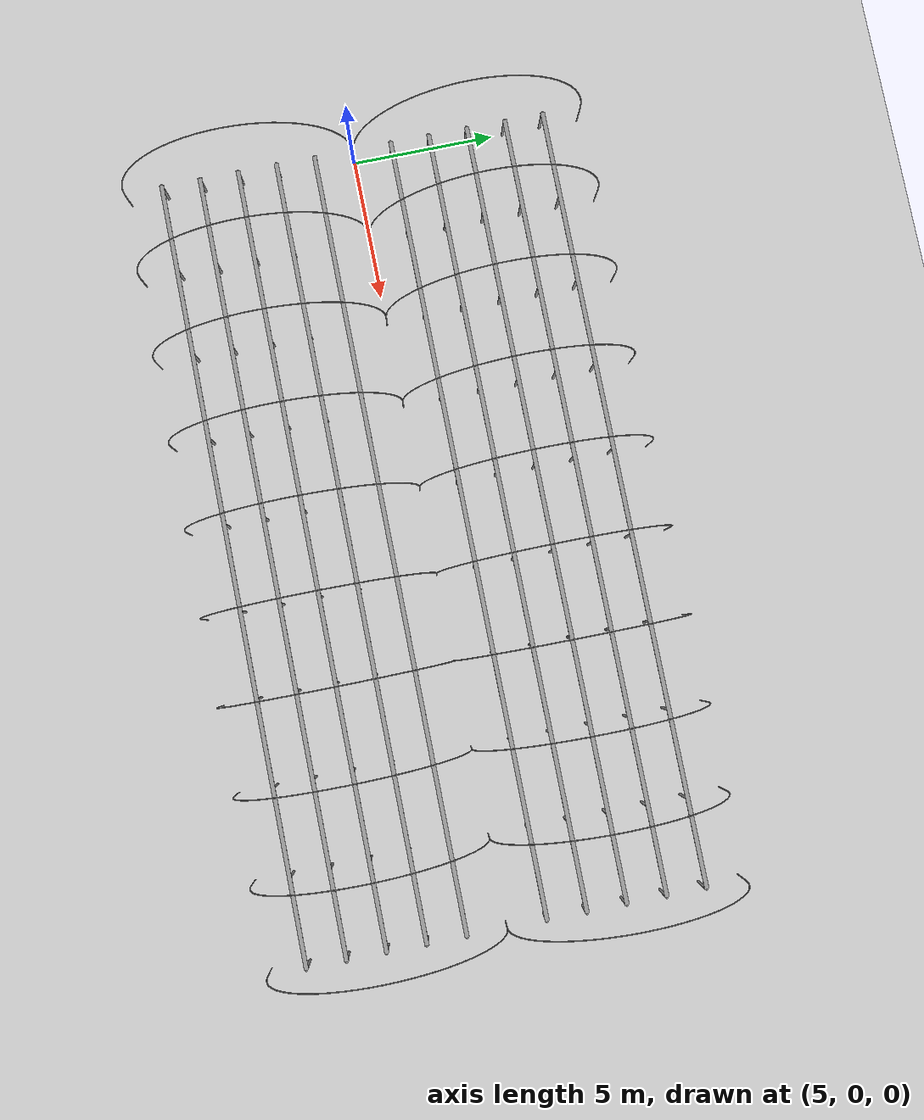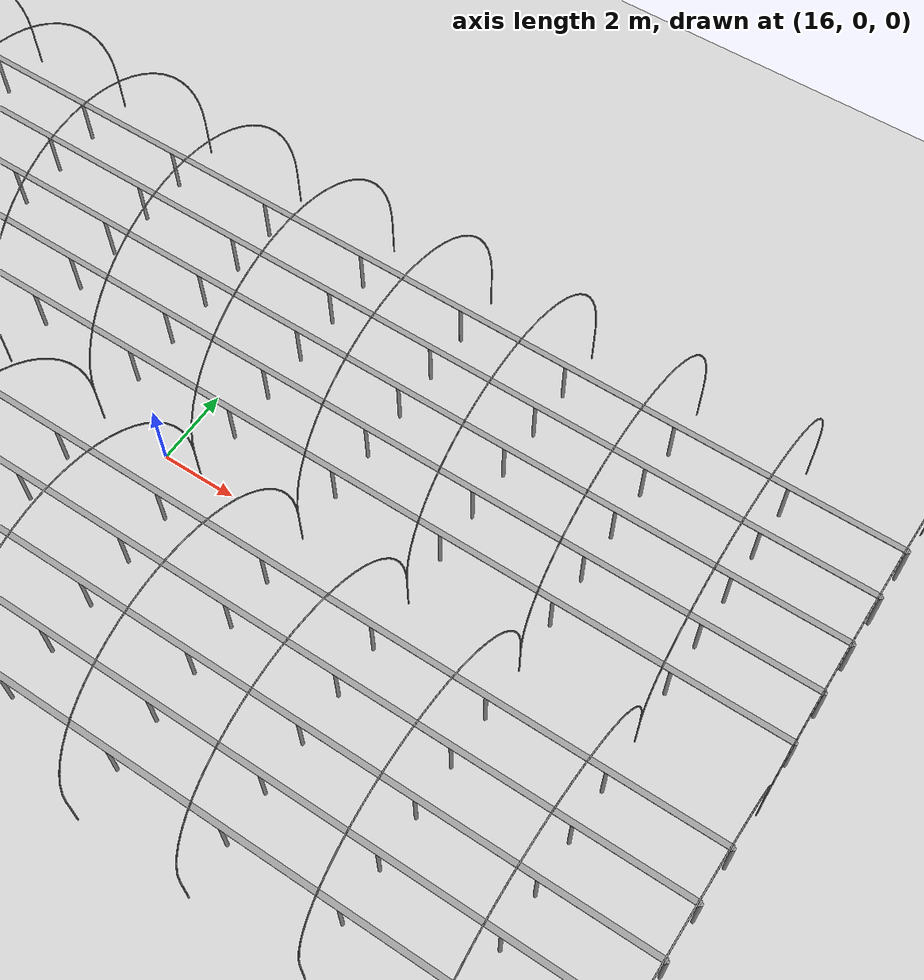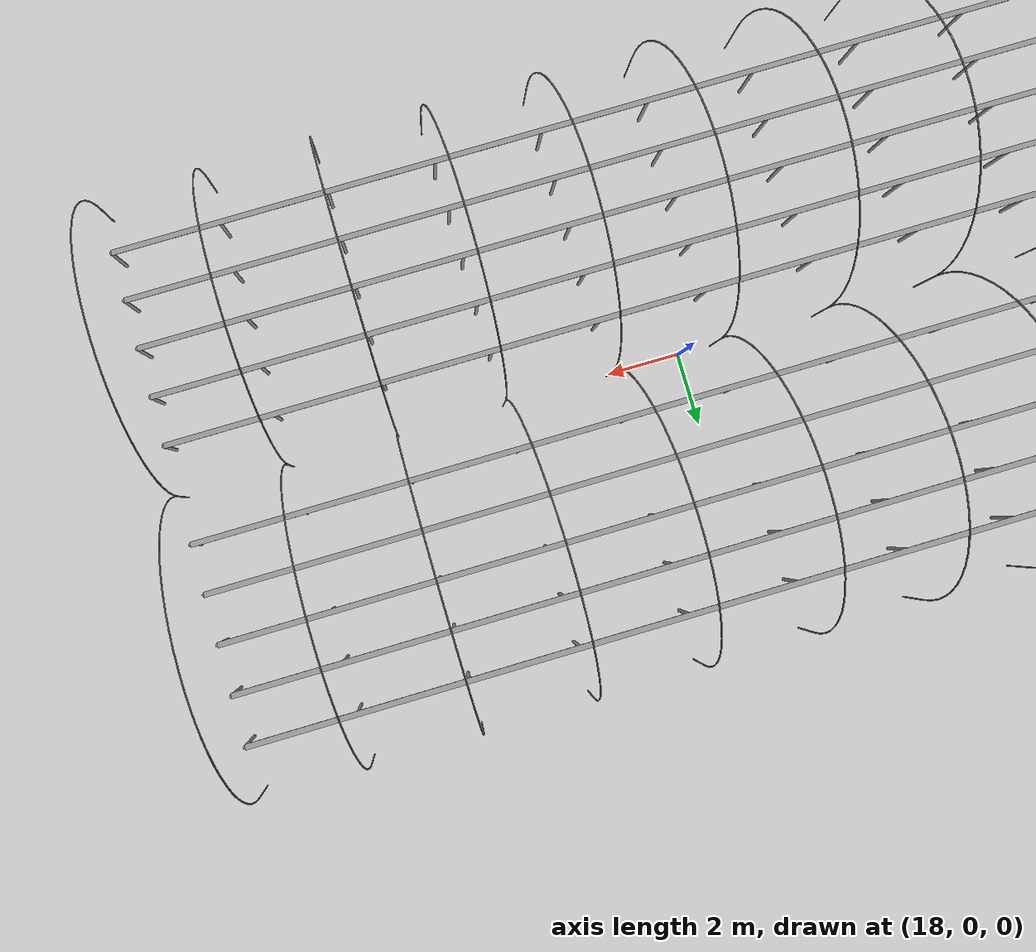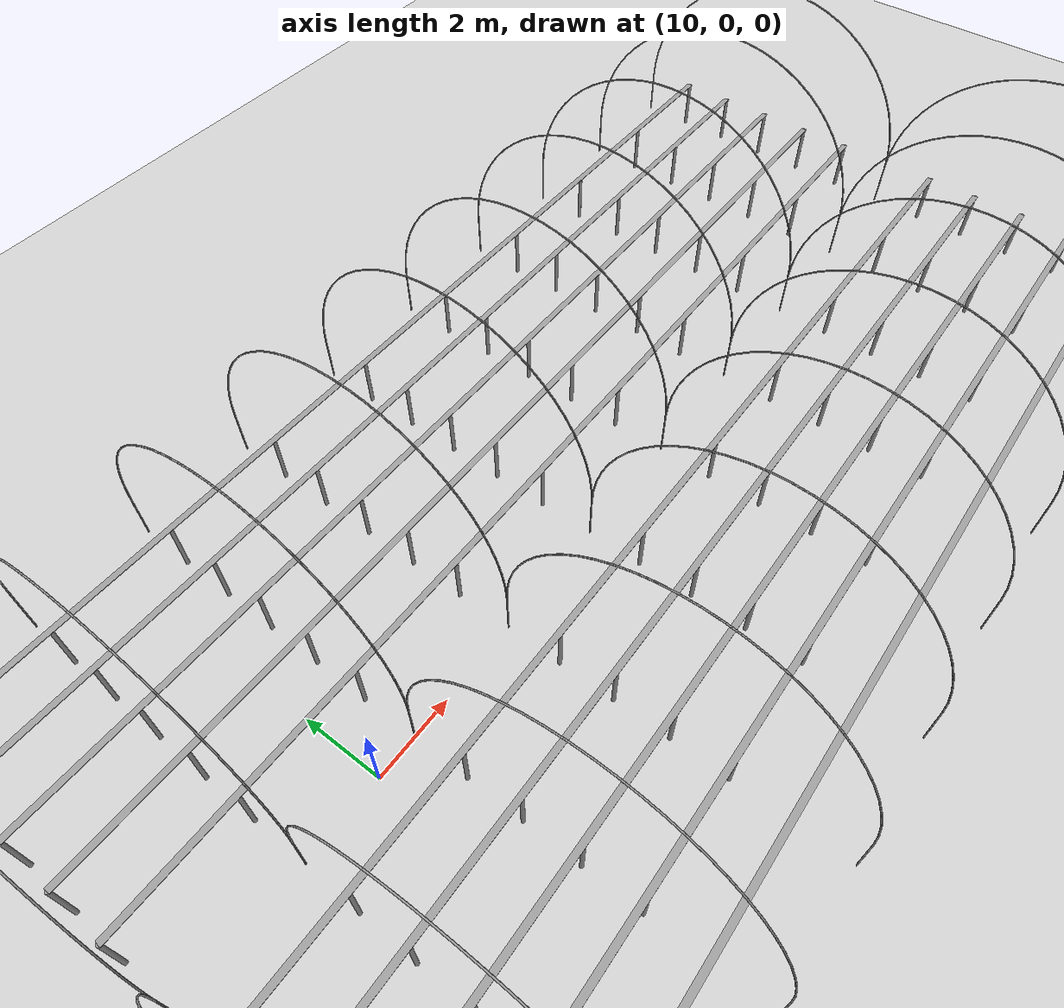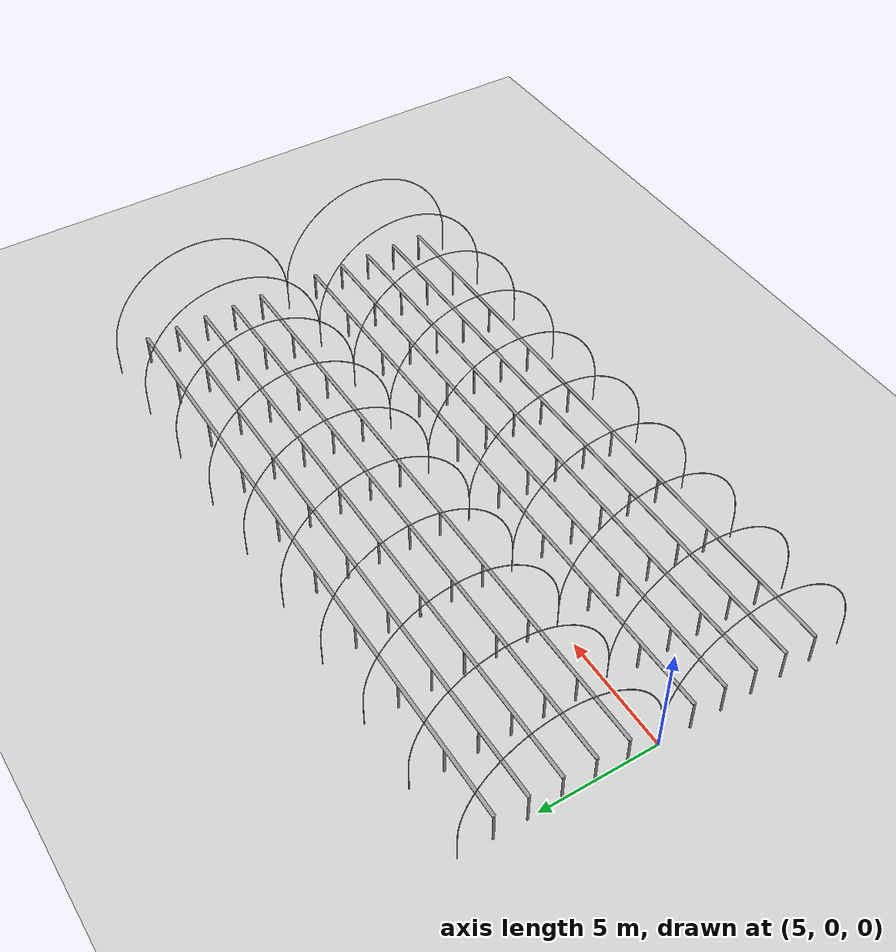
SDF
<?xml version="1.0" encoding="utf-8"?>
<sdf version="1.4">
	<world name="default">
		<model name="unit_cylinder_0">
			<static>1</static>
			<pose>5.00 1.35 0.691175 0.0 0.0 0.0</pose>
			<link name="link">
				<kinematic>0</kinematic>
				<inertial>
					<mass>1</mass>
					<inertia>
						<ixz>0</ixz>
						<ixx>1</ixx>
						<ixy>0</ixy>
						<izz>1</izz>
						<iyy>1</iyy>
						<iyz>0</iyz>
					</inertia>
				</inertial>
				<self_collide>0</self_collide>
				<gravity>1</gravity>
				<collision name="collision">
					<geometry>
						<cylinder>
							<length>1.38235</length>
							<radius>0.0456111</radius>
						</cylinder>
					</geometry>
					<max_contacts>10</max_contacts>
					<surface>
						<contact>
							<ode></ode>
						</contact>
						<friction>
							<ode></ode>
						</friction>
						<bounce></bounce>
					</surface>
				</collision>
				<visual name="visual">
					<geometry>
						<cylinder>
							<length>1.38235</length>
							<radius>0.0456111</radius>
						</cylinder>
					</geometry>
					<material>
						<script>
							<uri>file://media/materials/scripts/gazebo.material</uri>
							<name>Gazebo/Grey</name>
						</script>
					</material>
				</visual>
				<velocity_decay>
					<linear>0</linear>
					<angular>0</angular>
				</velocity_decay>
			</link>
		</model>
		<model name="unit_cylinder_1">
			<static>1</static>
			<pose>5.00 2.70 0.691175 0.0 0.0 0.0</pose>
			<link name="link">
				<kinematic>0</kinematic>
				<inertial>
					<mass>1</mass>
					<inertia>
						<ixz>0</ixz>
						<ixx>1</ixx>
						<ixy>0</ixy>
						<izz>1</izz>
						<iyy>1</iyy>
						<iyz>0</iyz>
					</inertia>
				</inertial>
				<self_collide>0</self_collide>
				<gravity>1</gravity>
				<collision name="collision">
					<geometry>
						<cylinder>
							<length>1.38235</length>
							<radius>0.0456111</radius>
						</cylinder>
					</geometry>
					<max_contacts>10</max_contacts>
					<surface>
						<contact>
							<ode></ode>
						</contact>
						<friction>
							<ode></ode>
						</friction>
						<bounce></bounce>
					</surface>
				</collision>
				<visual name="visual">
					<geometry>
						<cylinder>
							<length>1.38235</length>
							<radius>0.0456111</radius>
						</cylinder>
					</geometry>
					<material>
						<script>
							<uri>file://media/materials/scripts/gazebo.material</uri>
							<name>Gazebo/Grey</name>
						</script>
					</material>
				</visual>
				<velocity_decay>
					<linear>0</linear>
					<angular>0</angular>
				</velocity_decay>
			</link>
		</model>
		<model name="unit_cylinder_2">
			<static>1</static>
			<pose>5.00 4.05 0.691175 0.0 0.0 0.0</pose>
			<link name="link">
				<kinematic>0</kinematic>
				<inertial>
					<mass>1</mass>
					<inertia>
						<ixz>0</ixz>
						<ixx>1</ixx>
						<ixy>0</ixy>
						<izz>1</izz>
						<iyy>1</iyy>
						<iyz>0</iyz>
					</inertia>
				</inertial>
				<self_collide>0</self_collide>
				<gravity>1</gravity>
				<collision name="collision">
					<geometry>
						<cylinder>
							<length>1.38235</length>
							<radius>0.0456111</radius>
						</cylinder>
					</geometry>
					<max_contacts>10</max_contacts>
					<surface>
						<contact>
							<ode></ode>
						</contact>
						<friction>
							<ode></ode>
						</friction>
						<bounce></bounce>
					</surface>
				</collision>
				<visual name="visual">
					<geometry>
						<cylinder>
							<length>1.38235</length>
							<radius>0.0456111</radius>
						</cylinder>
					</geometry>
					<material>
						<script>
							<uri>file://media/materials/scripts/gazebo.material</uri>
							<name>Gazebo/Grey</name>
						</script>
					</material>
				</visual>
				<velocity_decay>
					<linear>0</linear>
					<angular>0</angular>
				</velocity_decay>
			</link>
		</model>
		<model name="unit_cylinder_3">
			<static>1</static>
			<pose>5.00 5.40 0.691175 0.0 0.0 0.0</pose>
			<link name="link">
				<kinematic>0</kinematic>
				<inertial>
					<mass>1</mass>
					<inertia>
						<ixz>0</ixz>
						<ixx>1</ixx>
						<ixy>0</ixy>
						<izz>1</izz>
						<iyy>1</iyy>
						<iyz>0</iyz>
					</inertia>
				</inertial>
				<self_collide>0</self_collide>
				<gravity>1</gravity>
				<collision name="collision">
					<geometry>
						<cylinder>
							<length>1.38235</length>
							<radius>0.0456111</radius>
						</cylinder>
					</geometry>
					<max_contacts>10</max_contacts>
					<surface>
						<contact>
							<ode></ode>
						</contact>
						<friction>
							<ode></ode>
						</friction>
						<bounce></bounce>
					</surface>
				</collision>
				<visual name="visual">
					<geometry>
						<cylinder>
							<length>1.38235</length>
							<radius>0.0456111</radius>
						</cylinder>
					</geometry>
					<material>
						<script>
							<uri>file://media/materials/scripts/gazebo.material</uri>
							<name>Gazebo/Grey</name>
						</script>
					</material>
				</visual>
				<velocity_decay>
					<linear>0</linear>
					<angular>0</angular>
				</velocity_decay>
			</link>
		</model>
		<model name="unit_cylinder_4">
			<static>1</static>
			<pose>5.00 6.75 0.691175 0.0 0.0 0.0</pose>
			<link name="link">
				<kinematic>0</kinematic>
				<inertial>
					<mass>1</mass>
					<inertia>
						<ixz>0</ixz>
						<ixx>1</ixx>
						<ixy>0</ixy>
						<izz>1</izz>
						<iyy>1</iyy>
						<iyz>0</iyz>
					</inertia>
				</inertial>
				<self_collide>0</self_collide>
				<gravity>1</gravity>
				<collision name="collision">
					<geometry>
						<cylinder>
							<length>1.38235</length>
							<radius>0.0456111</radius>
						</cylinder>
					</geometry>
					<max_contacts>10</max_contacts>
					<surface>
						<contact>
							<ode></ode>
						</contact>
						<friction>
							<ode></ode>
						</friction>
						<bounce></bounce>
					</surface>
				</collision>
				<visual name="visual">
					<geometry>
						<cylinder>
							<length>1.38235</length>
							<radius>0.0456111</radius>
						</cylinder>
					</geometry>
					<material>
						<script>
							<uri>file://media/materials/scripts/gazebo.material</uri>
							<name>Gazebo/Grey</name>
						</script>
					</material>
				</visual>
				<velocity_decay>
					<linear>0</linear>
					<angular>0</angular>
				</velocity_decay>
			</link>
		</model>
		<model name="unit_cylinder_5">
			<static>1</static>
			<pose>8.01 1.35 0.691175 0.0 0.0 0.0</pose>
			<link name="link">
				<kinematic>0</kinematic>
				<inertial>
					<mass>1</mass>
					<inertia>
						<ixz>0</ixz>
						<ixx>1</ixx>
						<ixy>0</ixy>
						<izz>1</izz>
						<iyy>1</iyy>
						<iyz>0</iyz>
					</inertia>
				</inertial>
				<self_collide>0</self_collide>
				<gravity>1</gravity>
				<collision name="collision">
					<geometry>
						<cylinder>
							<length>1.38235</length>
							<radius>0.0456111</radius>
						</cylinder>
					</geometry>
					<max_contacts>10</max_contacts>
					<surface>
						<contact>
							<ode></ode>
						</contact>
						<friction>
							<ode></ode>
						</friction>
						<bounce></bounce>
					</surface>
				</collision>
				<visual name="visual">
					<geometry>
						<cylinder>
							<length>1.38235</length>
							<radius>0.0456111</radius>
						</cylinder>
					</geometry>
					<material>
						<script>
							<uri>file://media/materials/scripts/gazebo.material</uri>
							<name>Gazebo/Grey</name>
						</script>
					</material>
				</visual>
				<velocity_decay>
					<linear>0</linear>
					<angular>0</angular>
				</velocity_decay>
			</link>
		</model>
		<model name="unit_cylinder_6">
			<static>1</static>
			<pose>8.01 2.70 0.691175 0.0 0.0 0.0</pose>
			<link name="link">
				<kinematic>0</kinematic>
				<inertial>
					<mass>1</mass>
					<inertia>
						<ixz>0</ixz>
						<ixx>1</ixx>
						<ixy>0</ixy>
						<izz>1</izz>
						<iyy>1</iyy>
						<iyz>0</iyz>
					</inertia>
				</inertial>
				<self_collide>0</self_collide>
				<gravity>1</gravity>
				<collision name="collision">
					<geometry>
						<cylinder>
							<length>1.38235</length>
							<radius>0.0456111</radius>
						</cylinder>
					</geometry>
					<max_contacts>10</max_contacts>
					<surface>
						<contact>
							<ode></ode>
						</contact>
						<friction>
							<ode></ode>
						</friction>
						<bounce></bounce>
					</surface>
				</collision>
				<visual name="visual">
					<geometry>
						<cylinder>
							<length>1.38235</length>
							<radius>0.0456111</radius>
						</cylinder>
					</geometry>
					<material>
						<script>
							<uri>file://media/materials/scripts/gazebo.material</uri>
							<name>Gazebo/Grey</name>
						</script>
					</material>
				</visual>
				<velocity_decay>
					<linear>0</linear>
					<angular>0</angular>
				</velocity_decay>
			</link>
		</model>
		<model name="unit_cylinder_7">
			<static>1</static>
			<pose>8.01 4.05 0.691175 0.0 0.0 0.0</pose>
			<link name="link">
				<kinematic>0</kinematic>
				<inertial>
					<mass>1</mass>
					<inertia>
						<ixz>0</ixz>
						<ixx>1</ixx>
						<ixy>0</ixy>
						<izz>1</izz>
						<iyy>1</iyy>
						<iyz>0</iyz>
					</inertia>
				</inertial>
				<self_collide>0</self_collide>
				<gravity>1</gravity>
				<collision name="collision">
					<geometry>
						<cylinder>
							<length>1.38235</length>
							<radius>0.0456111</radius>
						</cylinder>
					</geometry>
					<max_contacts>10</max_contacts>
					<surface>
						<contact>
							<ode></ode>
						</contact>
						<friction>
							<ode></ode>
						</friction>
						<bounce></bounce>
					</surface>
				</collision>
				<visual name="visual">
					<geometry>
						<cylinder>
							<length>1.38235</length>
							<radius>0.0456111</radius>
						</cylinder>
					</geometry>
					<material>
						<script>
							<uri>file://media/materials/scripts/gazebo.material</uri>
							<name>Gazebo/Grey</name>
						</script>
					</material>
				</visual>
				<velocity_decay>
					<linear>0</linear>
					<angular>0</angular>
				</velocity_decay>
			</link>
		</model>
		<model name="unit_cylinder_8">
			<static>1</static>
			<pose>8.01 5.40 0.691175 0.0 0.0 0.0</pose>
			<link name="link">
				<kinematic>0</kinematic>
				<inertial>
					<mass>1</mass>
					<inertia>
						<ixz>0</ixz>
						<ixx>1</ixx>
						<ixy>0</ixy>
						<izz>1</izz>
						<iyy>1</iyy>
						<iyz>0</iyz>
					</inertia>
				</inertial>
				<self_collide>0</self_collide>
				<gravity>1</gravity>
				<collision name="collision">
					<geometry>
						<cylinder>
							<length>1.38235</length>
							<radius>0.0456111</radius>
						</cylinder>
					</geometry>
					<max_contacts>10</max_contacts>
					<surface>
						<contact>
							<ode></ode>
						</contact>
						<friction>
							<ode></ode>
						</friction>
						<bounce></bounce>
					</surface>
				</collision>
				<visual name="visual">
					<geometry>
						<cylinder>
							<length>1.38235</length>
							<radius>0.0456111</radius>
						</cylinder>
					</geometry>
					<material>
						<script>
							<uri>file://media/materials/scripts/gazebo.material</uri>
							<name>Gazebo/Grey</name>
						</script>
					</material>
				</visual>
				<velocity_decay>
					<linear>0</linear>
					<angular>0</angular>
				</velocity_decay>
			</link>
		</model>
		<model name="unit_cylinder_9">
			<static>1</static>
			<pose>8.01 6.75 0.691175 0.0 0.0 0.0</pose>
			<link name="link">
				<kinematic>0</kinematic>
				<inertial>
					<mass>1</mass>
					<inertia>
						<ixz>0</ixz>
						<ixx>1</ixx>
						<ixy>0</ixy>
						<izz>1</izz>
						<iyy>1</iyy>
						<iyz>0</iyz>
					</inertia>
				</inertial>
				<self_collide>0</self_collide>
				<gravity>1</gravity>
				<collision name="collision">
					<geometry>
						<cylinder>
							<length>1.38235</length>
							<radius>0.0456111</radius>
						</cylinder>
					</geometry>
					<max_contacts>10</max_contacts>
					<surface>
						<contact>
							<ode></ode>
						</contact>
						<friction>
							<ode></ode>
						</friction>
						<bounce></bounce>
					</surface>
				</collision>
				<visual name="visual">
					<geometry>
						<cylinder>
							<length>1.38235</length>
							<radius>0.0456111</radius>
						</cylinder>
					</geometry>
					<material>
						<script>
							<uri>file://media/materials/scripts/gazebo.material</uri>
							<name>Gazebo/Grey</name>
						</script>
					</material>
				</visual>
				<velocity_decay>
					<linear>0</linear>
					<angular>0</angular>
				</velocity_decay>
			</link>
		</model>
		<model name="unit_cylinder_10">
			<static>1</static>
			<pose>11.02 1.35 0.691175 0.0 0.0 0.0</pose>
			<link name="link">
				<kinematic>0</kinematic>
				<inertial>
					<mass>1</mass>
					<inertia>
						<ixz>0</ixz>
						<ixx>1</ixx>
						<ixy>0</ixy>
						<izz>1</izz>
						<iyy>1</iyy>
						<iyz>0</iyz>
					</inertia>
				</inertial>
				<self_collide>0</self_collide>
				<gravity>1</gravity>
				<collision name="collision">
					<geometry>
						<cylinder>
							<length>1.38235</length>
							<radius>0.0456111</radius>
						</cylinder>
					</geometry>
					<max_contacts>10</max_contacts>
					<surface>
						<contact>
							<ode></ode>
						</contact>
						<friction>
							<ode></ode>
						</friction>
						<bounce></bounce>
					</surface>
				</collision>
				<visual name="visual">
					<geometry>
						<cylinder>
							<length>1.38235</length>
							<radius>0.0456111</radius>
						</cylinder>
					</geometry>
					<material>
						<script>
							<uri>file://media/materials/scripts/gazebo.material</uri>
							<name>Gazebo/Grey</name>
						</script>
					</material>
				</visual>
				<velocity_decay>
					<linear>0</linear>
					<angular>0</angular>
				</velocity_decay>
			</link>
		</model>
		<model name="unit_cylinder_11">
			<static>1</static>
			<pose>11.02 2.70 0.691175 0.0 0.0 0.0</pose>
			<link name="link">
				<kinematic>0</kinematic>
				<inertial>
					<mass>1</mass>
					<inertia>
						<ixz>0</ixz>
						<ixx>1</ixx>
						<ixy>0</ixy>
						<izz>1</izz>
						<iyy>1</iyy>
						<iyz>0</iyz>
					</inertia>
				</inertial>
				<self_collide>0</self_collide>
				<gravity>1</gravity>
				<collision name="collision">
					<geometry>
						<cylinder>
							<length>1.38235</length>
							<radius>0.0456111</radius>
						</cylinder>
					</geometry>
					<max_contacts>10</max_contacts>
					<surface>
						<contact>
							<ode></ode>
						</contact>
						<friction>
							<ode></ode>
						</friction>
						<bounce></bounce>
					</surface>
				</collision>
				<visual name="visual">
					<geometry>
						<cylinder>
							<length>1.38235</length>
							<radius>0.0456111</radius>
						</cylinder>
					</geometry>
					<material>
						<script>
							<uri>file://media/materials/scripts/gazebo.material</uri>
							<name>Gazebo/Grey</name>
						</script>
					</material>
				</visual>
				<velocity_decay>
					<linear>0</linear>
					<angular>0</angular>
				</velocity_decay>
			</link>
		</model>
		<model name="unit_cylinder_12">
			<static>1</static>
			<pose>11.02 4.05 0.691175 0.0 0.0 0.0</pose>
			<link name="link">
				<kinematic>0</kinematic>
				<inertial>
					<mass>1</mass>
					<inertia>
						<ixz>0</ixz>
						<ixx>1</ixx>
						<ixy>0</ixy>
						<izz>1</izz>
						<iyy>1</iyy>
						<iyz>0</iyz>
					</inertia>
				</inertial>
				<self_collide>0</self_collide>
				<gravity>1</gravity>
				<collision name="collision">
					<geometry>
						<cylinder>
							<length>1.38235</length>
							<radius>0.0456111</radius>
						</cylinder>
					</geometry>
					<max_contacts>10</max_contacts>
					<surface>
						<contact>
							<ode></ode>
						</contact>
						<friction>
							<ode></ode>
						</friction>
						<bounce></bounce>
					</surface>
				</collision>
				<visual name="visual">
					<geometry>
						<cylinder>
							<length>1.38235</length>
							<radius>0.0456111</radius>
						</cylinder>
					</geometry>
					<material>
						<script>
							<uri>file://media/materials/scripts/gazebo.material</uri>
							<name>Gazebo/Grey</name>
						</script>
					</material>
				</visual>
				<velocity_decay>
					<linear>0</linear>
					<angular>0</angular>
				</velocity_decay>
			</link>
		</model>
		<model name="unit_cylinder_13">
			<static>1</static>
			<pose>11.02 5.40 0.691175 0.0 0.0 0.0</pose>
			<link name="link">
				<kinematic>0</kinematic>
				<inertial>
					<mass>1</mass>
					<inertia>
						<ixz>0</ixz>
						<ixx>1</ixx>
						<ixy>0</ixy>
						<izz>1</izz>
						<iyy>1</iyy>
						<iyz>0</iyz>
					</inertia>
				</inertial>
				<self_collide>0</self_collide>
				<gravity>1</gravity>
				<collision name="collision">
					<geometry>
						<cylinder>
							<length>1.38235</length>
							<radius>0.0456111</radius>
						</cylinder>
					</geometry>
					<max_contacts>10</max_contacts>
					<surface>
						<contact>
							<ode></ode>
						</contact>
						<friction>
							<ode></ode>
						</friction>
						<bounce></bounce>
					</surface>
				</collision>
				<visual name="visual">
					<geometry>
						<cylinder>
							<length>1.38235</length>
							<radius>0.0456111</radius>
						</cylinder>
					</geometry>
					<material>
						<script>
							<uri>file://media/materials/scripts/gazebo.material</uri>
							<name>Gazebo/Grey</name>
						</script>
					</material>
				</visual>
				<velocity_decay>
					<linear>0</linear>
					<angular>0</angular>
				</velocity_decay>
			</link>
		</model>
		<model name="unit_cylinder_14">
			<static>1</static>
			<pose>11.02 6.75 0.691175 0.0 0.0 0.0</pose>
			<link name="link">
				<kinematic>0</kinematic>
				<inertial>
					<mass>1</mass>
					<inertia>
						<ixz>0</ixz>
						<ixx>1</ixx>
						<ixy>0</ixy>
						<izz>1</izz>
						<iyy>1</iyy>
						<iyz>0</iyz>
					</inertia>
				</inertial>
				<self_collide>0</self_collide>
				<gravity>1</gravity>
				<collision name="collision">
					<geometry>
						<cylinder>
							<length>1.38235</length>
							<radius>0.0456111</radius>
						</cylinder>
					</geometry>
					<max_contacts>10</max_contacts>
					<surface>
						<contact>
							<ode></ode>
						</contact>
						<friction>
							<ode></ode>
						</friction>
						<bounce></bounce>
					</surface>
				</collision>
				<visual name="visual">
					<geometry>
						<cylinder>
							<length>1.38235</length>
							<radius>0.0456111</radius>
						</cylinder>
					</geometry>
					<material>
						<script>
							<uri>file://media/materials/scripts/gazebo.material</uri>
							<name>Gazebo/Grey</name>
						</script>
					</material>
				</visual>
				<velocity_decay>
					<linear>0</linear>
					<angular>0</angular>
				</velocity_decay>
			</link>
		</model>
		<model name="unit_cylinder_15">
			<static>1</static>
			<pose>14.03 1.35 0.691175 0.0 0.0 0.0</pose>
			<link name="link">
				<kinematic>0</kinematic>
				<inertial>
					<mass>1</mass>
					<inertia>
						<ixz>0</ixz>
						<ixx>1</ixx>
						<ixy>0</ixy>
						<izz>1</izz>
						<iyy>1</iyy>
						<iyz>0</iyz>
					</inertia>
				</inertial>
				<self_collide>0</self_collide>
				<gravity>1</gravity>
				<collision name="collision">
					<geometry>
						<cylinder>
							<length>1.38235</length>
							<radius>0.0456111</radius>
						</cylinder>
					</geometry>
					<max_contacts>10</max_contacts>
					<surface>
						<contact>
							<ode></ode>
						</contact>
						<friction>
							<ode></ode>
						</friction>
						<bounce></bounce>
					</surface>
				</collision>
				<visual name="visual">
					<geometry>
						<cylinder>
							<length>1.38235</length>
							<radius>0.0456111</radius>
						</cylinder>
					</geometry>
					<material>
						<script>
							<uri>file://media/materials/scripts/gazebo.material</uri>
							<name>Gazebo/Grey</name>
						</script>
					</material>
				</visual>
				<velocity_decay>
					<linear>0</linear>
					<angular>0</angular>
				</velocity_decay>
			</link>
		</model>
		<model name="unit_cylinder_16">
			<static>1</static>
			<pose>14.03 2.70 0.691175 0.0 0.0 0.0</pose>
			<link name="link">
				<kinematic>0</kinematic>
				<inertial>
					<mass>1</mass>
					<inertia>
						<ixz>0</ixz>
						<ixx>1</ixx>
						<ixy>0</ixy>
						<izz>1</izz>
						<iyy>1</iyy>
						<iyz>0</iyz>
					</inertia>
				</inertial>
				<self_collide>0</self_collide>
				<gravity>1</gravity>
				<collision name="collision">
					<geometry>
						<cylinder>
							<length>1.38235</length>
							<radius>0.0456111</radius>
						</cylinder>
					</geometry>
					<max_contacts>10</max_contacts>
					<surface>
						<contact>
							<ode></ode>
						</contact>
						<friction>
							<ode></ode>
						</friction>
						<bounce></bounce>
					</surface>
				</collision>
				<visual name="visual">
					<geometry>
						<cylinder>
							<length>1.38235</length>
							<radius>0.0456111</radius>
						</cylinder>
					</geometry>
					<material>
						<script>
							<uri>file://media/materials/scripts/gazebo.material</uri>
							<name>Gazebo/Grey</name>
						</script>
					</material>
				</visual>
				<velocity_decay>
					<linear>0</linear>
					<angular>0</angular>
				</velocity_decay>
			</link>
		</model>
		<model name="unit_cylinder_17">
			<static>1</static>
			<pose>14.03 4.05 0.691175 0.0 0.0 0.0</pose>
			<link name="link">
				<kinematic>0</kinematic>
				<inertial>
					<mass>1</mass>
					<inertia>
						<ixz>0</ixz>
						<ixx>1</ixx>
						<ixy>0</ixy>
						<izz>1</izz>
						<iyy>1</iyy>
						<iyz>0</iyz>
					</inertia>
				</inertial>
				<self_collide>0</self_collide>
				<gravity>1</gravity>
				<collision name="collision">
					<geometry>
						<cylinder>
							<length>1.38235</length>
							<radius>0.0456111</radius>
						</cylinder>
					</geometry>
					<max_contacts>10</max_contacts>
					<surface>
						<contact>
							<ode></ode>
						</contact>
						<friction>
							<ode></ode>
						</friction>
						<bounce></bounce>
					</surface>
				</collision>
				<visual name="visual">
					<geometry>
						<cylinder>
							<length>1.38235</length>
							<radius>0.0456111</radius>
						</cylinder>
					</geometry>
					<material>
						<script>
							<uri>file://media/materials/scripts/gazebo.material</uri>
							<name>Gazebo/Grey</name>
						</script>
					</material>
				</visual>
				<velocity_decay>
					<linear>0</linear>
					<angular>0</angular>
				</velocity_decay>
			</link>
		</model>
		<model name="unit_cylinder_18">
			<static>1</static>
			<pose>14.03 5.40 0.691175 0.0 0.0 0.0</pose>
			<link name="link">
				<kinematic>0</kinematic>
				<inertial>
					<mass>1</mass>
					<inertia>
						<ixz>0</ixz>
						<ixx>1</ixx>
						<ixy>0</ixy>
						<izz>1</izz>
						<iyy>1</iyy>
						<iyz>0</iyz>
					</inertia>
				</inertial>
				<self_collide>0</self_collide>
				<gravity>1</gravity>
				<collision name="collision">
					<geometry>
						<cylinder>
							<length>1.38235</length>
							<radius>0.0456111</radius>
						</cylinder>
					</geometry>
					<max_contacts>10</max_contacts>
					<surface>
						<contact>
							<ode></ode>
						</contact>
						<friction>
							<ode></ode>
						</friction>
						<bounce></bounce>
					</surface>
				</collision>
				<visual name="visual">
					<geometry>
						<cylinder>
							<length>1.38235</length>
							<radius>0.0456111</radius>
						</cylinder>
					</geometry>
					<material>
						<script>
							<uri>file://media/materials/scripts/gazebo.material</uri>
							<name>Gazebo/Grey</name>
						</script>
					</material>
				</visual>
				<velocity_decay>
					<linear>0</linear>
					<angular>0</angular>
				</velocity_decay>
			</link>
		</model>
		<model name="unit_cylinder_19">
			<static>1</static>
			<pose>14.03 6.75 0.691175 0.0 0.0 0.0</pose>
			<link name="link">
				<kinematic>0</kinematic>
				<inertial>
					<mass>1</mass>
					<inertia>
						<ixz>0</ixz>
						<ixx>1</ixx>
						<ixy>0</ixy>
						<izz>1</izz>
						<iyy>1</iyy>
						<iyz>0</iyz>
					</inertia>
				</inertial>
				<self_collide>0</self_collide>
				<gravity>1</gravity>
				<collision name="collision">
					<geometry>
						<cylinder>
							<length>1.38235</length>
							<radius>0.0456111</radius>
						</cylinder>
					</geometry>
					<max_contacts>10</max_contacts>
					<surface>
						<contact>
							<ode></ode>
						</contact>
						<friction>
							<ode></ode>
						</friction>
						<bounce></bounce>
					</surface>
				</collision>
				<visual name="visual">
					<geometry>
						<cylinder>
							<length>1.38235</length>
							<radius>0.0456111</radius>
						</cylinder>
					</geometry>
					<material>
						<script>
							<uri>file://media/materials/scripts/gazebo.material</uri>
							<name>Gazebo/Grey</name>
						</script>
					</material>
				</visual>
				<velocity_decay>
					<linear>0</linear>
					<angular>0</angular>
				</velocity_decay>
			</link>
		</model>
		<model name="unit_cylinder_20">
			<static>1</static>
			<pose>17.04 1.35 0.691175 0.0 0.0 0.0</pose>
			<link name="link">
				<kinematic>0</kinematic>
				<inertial>
					<mass>1</mass>
					<inertia>
						<ixz>0</ixz>
						<ixx>1</ixx>
						<ixy>0</ixy>
						<izz>1</izz>
						<iyy>1</iyy>
						<iyz>0</iyz>
					</inertia>
				</inertial>
				<self_collide>0</self_collide>
				<gravity>1</gravity>
				<collision name="collision">
					<geometry>
						<cylinder>
							<length>1.38235</length>
							<radius>0.0456111</radius>
						</cylinder>
					</geometry>
					<max_contacts>10</max_contacts>
					<surface>
						<contact>
							<ode></ode>
						</contact>
						<friction>
							<ode></ode>
						</friction>
						<bounce></bounce>
					</surface>
				</collision>
				<visual name="visual">
					<geometry>
						<cylinder>
							<length>1.38235</length>
							<radius>0.0456111</radius>
						</cylinder>
					</geometry>
					<material>
						<script>
							<uri>file://media/materials/scripts/gazebo.material</uri>
							<name>Gazebo/Grey</name>
						</script>
					</material>
				</visual>
				<velocity_decay>
					<linear>0</linear>
					<angular>0</angular>
				</velocity_decay>
			</link>
		</model>
		<model name="unit_cylinder_21">
			<static>1</static>
			<pose>17.04 2.70 0.691175 0.0 0.0 0.0</pose>
			<link name="link">
				<kinematic>0</kinematic>
				<inertial>
					<mass>1</mass>
					<inertia>
						<ixz>0</ixz>
						<ixx>1</ixx>
						<ixy>0</ixy>
						<izz>1</izz>
						<iyy>1</iyy>
						<iyz>0</iyz>
					</inertia>
				</inertial>
				<self_collide>0</self_collide>
				<gravity>1</gravity>
				<collision name="collision">
					<geometry>
						<cylinder>
							<length>1.38235</length>
							<radius>0.0456111</radius>
						</cylinder>
					</geometry>
					<max_contacts>10</max_contacts>
					<surface>
						<contact>
							<ode></ode>
						</contact>
						<friction>
							<ode></ode>
						</friction>
						<bounce></bounce>
					</surface>
				</collision>
				<visual name="visual">
					<geometry>
						<cylinder>
							<length>1.38235</length>
							<radius>0.0456111</radius>
						</cylinder>
					</geometry>
					<material>
						<script>
							<uri>file://media/materials/scripts/gazebo.material</uri>
							<name>Gazebo/Grey</name>
						</script>
					</material>
				</visual>
				<velocity_decay>
					<linear>0</linear>
					<angular>0</angular>
				</velocity_decay>
			</link>
		</model>
		<model name="unit_cylinder_22">
			<static>1</static>
			<pose>17.04 4.05 0.691175 0.0 0.0 0.0</pose>
			<link name="link">
				<kinematic>0</kinematic>
				<inertial>
					<mass>1</mass>
					<inertia>
						<ixz>0</ixz>
						<ixx>1</ixx>
						<ixy>0</ixy>
						<izz>1</izz>
						<iyy>1</iyy>
						<iyz>0</iyz>
					</inertia>
				</inertial>
				<self_collide>0</self_collide>
				<gravity>1</gravity>
				<collision name="collision">
					<geometry>
						<cylinder>
							<length>1.38235</length>
							<radius>0.0456111</radius>
						</cylinder>
					</geometry>
					<max_contacts>10</max_contacts>
					<surface>
						<contact>
							<ode></ode>
						</contact>
						<friction>
							<ode></ode>
						</friction>
						<bounce></bounce>
					</surface>
				</collision>
				<visual name="visual">
					<geometry>
						<cylinder>
							<length>1.38235</length>
							<radius>0.0456111</radius>
						</cylinder>
					</geometry>
					<material>
						<script>
							<uri>file://media/materials/scripts/gazebo.material</uri>
							<name>Gazebo/Grey</name>
						</script>
					</material>
				</visual>
				<velocity_decay>
					<linear>0</linear>
					<angular>0</angular>
				</velocity_decay>
			</link>
		</model>
		<model name="unit_cylinder_23">
			<static>1</static>
			<pose>17.04 5.40 0.691175 0.0 0.0 0.0</pose>
			<link name="link">
				<kinematic>0</kinematic>
				<inertial>
					<mass>1</mass>
					<inertia>
						<ixz>0</ixz>
						<ixx>1</ixx>
						<ixy>0</ixy>
						<izz>1</izz>
						<iyy>1</iyy>
						<iyz>0</iyz>
					</inertia>
				</inertial>
				<self_collide>0</self_collide>
				<gravity>1</gravity>
				<collision name="collision">
					<geometry>
						<cylinder>
							<length>1.38235</length>
							<radius>0.0456111</radius>
						</cylinder>
					</geometry>
					<max_contacts>10</max_contacts>
					<surface>
						<contact>
							<ode></ode>
						</contact>
						<friction>
							<ode></ode>
						</friction>
						<bounce></bounce>
					</surface>
				</collision>
				<visual name="visual">
					<geometry>
						<cylinder>
							<length>1.38235</length>
							<radius>0.0456111</radius>
						</cylinder>
					</geometry>
					<material>
						<script>
							<uri>file://media/materials/scripts/gazebo.material</uri>
							<name>Gazebo/Grey</name>
						</script>
					</material>
				</visual>
				<velocity_decay>
					<linear>0</linear>
					<angular>0</angular>
				</velocity_decay>
			</link>
		</model>
		<model name="unit_cylinder_24">
			<static>1</static>
			<pose>17.04 6.75 0.691175 0.0 0.0 0.0</pose>
			<link name="link">
				<kinematic>0</kinematic>
				<inertial>
					<mass>1</mass>
					<inertia>
						<ixz>0</ixz>
						<ixx>1</ixx>
						<ixy>0</ixy>
						<izz>1</izz>
						<iyy>1</iyy>
						<iyz>0</iyz>
					</inertia>
				</inertial>
				<self_collide>0</self_collide>
				<gravity>1</gravity>
				<collision name="collision">
					<geometry>
						<cylinder>
							<length>1.38235</length>
							<radius>0.0456111</radius>
						</cylinder>
					</geometry>
					<max_contacts>10</max_contacts>
					<surface>
						<contact>
							<ode></ode>
						</contact>
						<friction>
							<ode></ode>
						</friction>
						<bounce></bounce>
					</surface>
				</collision>
				<visual name="visual">
					<geometry>
						<cylinder>
							<length>1.38235</length>
							<radius>0.0456111</radius>
						</cylinder>
					</geometry>
					<material>
						<script>
							<uri>file://media/materials/scripts/gazebo.material</uri>
							<name>Gazebo/Grey</name>
						</script>
					</material>
				</visual>
				<velocity_decay>
					<linear>0</linear>
					<angular>0</angular>
				</velocity_decay>
			</link>
		</model>
		<model name="unit_cylinder_25">
			<static>1</static>
			<pose>20.05 1.35 0.691175 0.0 0.0 0.0</pose>
			<link name="link">
				<kinematic>0</kinematic>
				<inertial>
					<mass>1</mass>
					<inertia>
						<ixz>0</ixz>
						<ixx>1</ixx>
						<ixy>0</ixy>
						<izz>1</izz>
						<iyy>1</iyy>
						<iyz>0</iyz>
					</inertia>
				</inertial>
				<self_collide>0</self_collide>
				<gravity>1</gravity>
				<collision name="collision">
					<geometry>
						<cylinder>
							<length>1.38235</length>
							<radius>0.0456111</radius>
						</cylinder>
					</geometry>
					<max_contacts>10</max_contacts>
					<surface>
						<contact>
							<ode></ode>
						</contact>
						<friction>
							<ode></ode>
						</friction>
						<bounce></bounce>
					</surface>
				</collision>
				<visual name="visual">
					<geometry>
						<cylinder>
							<length>1.38235</length>
							<radius>0.0456111</radius>
						</cylinder>
					</geometry>
					<material>
						<script>
							<uri>file://media/materials/scripts/gazebo.material</uri>
							<name>Gazebo/Grey</name>
						</script>
					</material>
				</visual>
				<velocity_decay>
					<linear>0</linear>
					<angular>0</angular>
				</velocity_decay>
			</link>
		</model>
		<model name="unit_cylinder_26">
			<static>1</static>
			<pose>20.05 2.70 0.691175 0.0 0.0 0.0</pose>
			<link name="link">
				<kinematic>0</kinematic>
				<inertial>
					<mass>1</mass>
					<inertia>
						<ixz>0</ixz>
						<ixx>1</ixx>
						<ixy>0</ixy>
						<izz>1</izz>
						<iyy>1</iyy>
						<iyz>0</iyz>
					</inertia>
				</inertial>
				<self_collide>0</self_collide>
				<gravity>1</gravity>
				<collision name="collision">
					<geometry>
						<cylinder>
							<length>1.38235</length>
							<radius>0.0456111</radius>
						</cylinder>
					</geometry>
					<max_contacts>10</max_contacts>
					<surface>
						<contact>
							<ode></ode>
						</contact>
						<friction>
							<ode></ode>
						</friction>
						<bounce></bounce>
					</surface>
				</collision>
				<visual name="visual">
					<geometry>
						<cylinder>
							<length>1.38235</length>
							<radius>0.0456111</radius>
						</cylinder>
					</geometry>
					<material>
						<script>
							<uri>file://media/materials/scripts/gazebo.material</uri>
							<name>Gazebo/Grey</name>
						</script>
					</material>
				</visual>
				<velocity_decay>
					<linear>0</linear>
					<angular>0</angular>
				</velocity_decay>
			</link>
		</model>
		<model name="unit_cylinder_27">
			<static>1</static>
			<pose>20.05 4.05 0.691175 0.0 0.0 0.0</pose>
			<link name="link">
				<kinematic>0</kinematic>
				<inertial>
					<mass>1</mass>
					<inertia>
						<ixz>0</ixz>
						<ixx>1</ixx>
						<ixy>0</ixy>
						<izz>1</izz>
						<iyy>1</iyy>
						<iyz>0</iyz>
					</inertia>
				</inertial>
				<self_collide>0</self_collide>
				<gravity>1</gravity>
				<collision name="collision">
					<geometry>
						<cylinder>
							<length>1.38235</length>
							<radius>0.0456111</radius>
						</cylinder>
					</geometry>
					<max_contacts>10</max_contacts>
					<surface>
						<contact>
							<ode></ode>
						</contact>
						<friction>
							<ode></ode>
						</friction>
						<bounce></bounce>
					</surface>
				</collision>
				<visual name="visual">
					<geometry>
						<cylinder>
							<length>1.38235</length>
							<radius>0.0456111</radius>
						</cylinder>
					</geometry>
					<material>
						<script>
							<uri>file://media/materials/scripts/gazebo.material</uri>
							<name>Gazebo/Grey</name>
						</script>
					</material>
				</visual>
				<velocity_decay>
					<linear>0</linear>
					<angular>0</angular>
				</velocity_decay>
			</link>
		</model>
		<model name="unit_cylinder_28">
			<static>1</static>
			<pose>20.05 5.40 0.691175 0.0 0.0 0.0</pose>
			<link name="link">
				<kinematic>0</kinematic>
				<inertial>
					<mass>1</mass>
					<inertia>
						<ixz>0</ixz>
						<ixx>1</ixx>
						<ixy>0</ixy>
						<izz>1</izz>
						<iyy>1</iyy>
						<iyz>0</iyz>
					</inertia>
				</inertial>
				<self_collide>0</self_collide>
				<gravity>1</gravity>
				<collision name="collision">
					<geometry>
						<cylinder>
							<length>1.38235</length>
							<radius>0.0456111</radius>
						</cylinder>
					</geometry>
					<max_contacts>10</max_contacts>
					<surface>
						<contact>
							<ode></ode>
						</contact>
						<friction>
							<ode></ode>
						</friction>
						<bounce></bounce>
					</surface>
				</collision>
				<visual name="visual">
					<geometry>
						<cylinder>
							<length>1.38235</length>
							<radius>0.0456111</radius>
						</cylinder>
					</geometry>
					<material>
						<script>
							<uri>file://media/materials/scripts/gazebo.material</uri>
							<name>Gazebo/Grey</name>
						</script>
					</material>
				</visual>
				<velocity_decay>
					<linear>0</linear>
					<angular>0</angular>
				</velocity_decay>
			</link>
		</model>
		<model name="unit_cylinder_29">
			<static>1</static>
			<pose>20.05 6.75 0.691175 0.0 0.0 0.0</pose>
			<link name="link">
				<kinematic>0</kinematic>
				<inertial>
					<mass>1</mass>
					<inertia>
						<ixz>0</ixz>
						<ixx>1</ixx>
						<ixy>0</ixy>
						<izz>1</izz>
						<iyy>1</iyy>
						<iyz>0</iyz>
					</inertia>
				</inertial>
				<self_collide>0</self_collide>
				<gravity>1</gravity>
				<collision name="collision">
					<geometry>
						<cylinder>
							<length>1.38235</length>
							<radius>0.0456111</radius>
						</cylinder>
					</geometry>
					<max_contacts>10</max_contacts>
					<surface>
						<contact>
							<ode></ode>
						</contact>
						<friction>
							<ode></ode>
						</friction>
						<bounce></bounce>
					</surface>
				</collision>
				<visual name="visual">
					<geometry>
						<cylinder>
							<length>1.38235</length>
							<radius>0.0456111</radius>
						</cylinder>
					</geometry>
					<material>
						<script>
							<uri>file://media/materials/scripts/gazebo.material</uri>
							<name>Gazebo/Grey</name>
						</script>
					</material>
				</visual>
				<velocity_decay>
					<linear>0</linear>
					<angular>0</angular>
				</velocity_decay>
			</link>
		</model>
		<model name="unit_cylinder_30">
			<static>1</static>
			<pose>23.06 1.35 0.691175 0.0 0.0 0.0</pose>
			<link name="link">
				<kinematic>0</kinematic>
				<inertial>
					<mass>1</mass>
					<inertia>
						<ixz>0</ixz>
						<ixx>1</ixx>
						<ixy>0</ixy>
						<izz>1</izz>
						<iyy>1</iyy>
						<iyz>0</iyz>
					</inertia>
				</inertial>
				<self_collide>0</self_collide>
				<gravity>1</gravity>
				<collision name="collision">
					<geometry>
						<cylinder>
							<length>1.38235</length>
							<radius>0.0456111</radius>
						</cylinder>
					</geometry>
					<max_contacts>10</max_contacts>
					<surface>
						<contact>
							<ode></ode>
						</contact>
						<friction>
							<ode></ode>
						</friction>
						<bounce></bounce>
					</surface>
				</collision>
				<visual name="visual">
					<geometry>
						<cylinder>
							<length>1.38235</length>
							<radius>0.0456111</radius>
						</cylinder>
					</geometry>
					<material>
						<script>
							<uri>file://media/materials/scripts/gazebo.material</uri>
							<name>Gazebo/Grey</name>
						</script>
					</material>
				</visual>
				<velocity_decay>
					<linear>0</linear>
					<angular>0</angular>
				</velocity_decay>
			</link>
		</model>
		<model name="unit_cylinder_31">
			<static>1</static>
			<pose>23.06 2.70 0.691175 0.0 0.0 0.0</pose>
			<link name="link">
				<kinematic>0</kinematic>
				<inertial>
					<mass>1</mass>
					<inertia>
						<ixz>0</ixz>
						<ixx>1</ixx>
						<ixy>0</ixy>
						<izz>1</izz>
						<iyy>1</iyy>
						<iyz>0</iyz>
					</inertia>
				</inertial>
				<self_collide>0</self_collide>
				<gravity>1</gravity>
				<collision name="collision">
					<geometry>
						<cylinder>
							<length>1.38235</length>
							<radius>0.0456111</radius>
						</cylinder>
					</geometry>
					<max_contacts>10</max_contacts>
					<surface>
						<contact>
							<ode></ode>
						</contact>
						<friction>
							<ode></ode>
						</friction>
						<bounce></bounce>
					</surface>
				</collision>
				<visual name="visual">
					<geometry>
						<cylinder>
							<length>1.38235</length>
							<radius>0.0456111</radius>
						</cylinder>
					</geometry>
					<material>
						<script>
							<uri>file://media/materials/scripts/gazebo.material</uri>
							<name>Gazebo/Grey</name>
						</script>
					</material>
				</visual>
				<velocity_decay>
					<linear>0</linear>
					<angular>0</angular>
				</velocity_decay>
			</link>
		</model>
		<model name="unit_cylinder_32">
			<static>1</static>
			<pose>23.06 4.05 0.691175 0.0 0.0 0.0</pose>
			<link name="link">
				<kinematic>0</kinematic>
				<inertial>
					<mass>1</mass>
					<inertia>
						<ixz>0</ixz>
						<ixx>1</ixx>
						<ixy>0</ixy>
						<izz>1</izz>
						<iyy>1</iyy>
						<iyz>0</iyz>
					</inertia>
				</inertial>
				<self_collide>0</self_collide>
				<gravity>1</gravity>
				<collision name="collision">
					<geometry>
						<cylinder>
							<length>1.38235</length>
							<radius>0.0456111</radius>
						</cylinder>
					</geometry>
					<max_contacts>10</max_contacts>
					<surface>
						<contact>
							<ode></ode>
						</contact>
						<friction>
							<ode></ode>
						</friction>
						<bounce></bounce>
					</surface>
				</collision>
				<visual name="visual">
					<geometry>
						<cylinder>
							<length>1.38235</length>
							<radius>0.0456111</radius>
						</cylinder>
					</geometry>
					<material>
						<script>
							<uri>file://media/materials/scripts/gazebo.material</uri>
							<name>Gazebo/Grey</name>
						</script>
					</material>
				</visual>
				<velocity_decay>
					<linear>0</linear>
					<angular>0</angular>
				</velocity_decay>
			</link>
		</model>
		<model name="unit_cylinder_33">
			<static>1</static>
			<pose>23.06 5.40 0.691175 0.0 0.0 0.0</pose>
			<link name="link">
				<kinematic>0</kinematic>
				<inertial>
					<mass>1</mass>
					<inertia>
						<ixz>0</ixz>
						<ixx>1</ixx>
						<ixy>0</ixy>
						<izz>1</izz>
						<iyy>1</iyy>
						<iyz>0</iyz>
					</inertia>
				</inertial>
				<self_collide>0</self_collide>
				<gravity>1</gravity>
				<collision name="collision">
					<geometry>
						<cylinder>
							<length>1.38235</length>
							<radius>0.0456111</radius>
						</cylinder>
					</geometry>
					<max_contacts>10</max_contacts>
					<surface>
						<contact>
							<ode></ode>
						</contact>
						<friction>
							<ode></ode>
						</friction>
						<bounce></bounce>
					</surface>
				</collision>
				<visual name="visual">
					<geometry>
						<cylinder>
							<length>1.38235</length>
							<radius>0.0456111</radius>
						</cylinder>
					</geometry>
					<material>
						<script>
							<uri>file://media/materials/scripts/gazebo.material</uri>
							<name>Gazebo/Grey</name>
						</script>
					</material>
				</visual>
				<velocity_decay>
					<linear>0</linear>
					<angular>0</angular>
				</velocity_decay>
			</link>
		</model>
		<model name="unit_cylinder_34">
			<static>1</static>
			<pose>23.06 6.75 0.691175 0.0 0.0 0.0</pose>
			<link name="link">
				<kinematic>0</kinematic>
				<inertial>
					<mass>1</mass>
					<inertia>
						<ixz>0</ixz>
						<ixx>1</ixx>
						<ixy>0</ixy>
						<izz>1</izz>
						<iyy>1</iyy>
						<iyz>0</iyz>
					</inertia>
				</inertial>
				<self_collide>0</self_collide>
				<gravity>1</gravity>
				<collision name="collision">
					<geometry>
						<cylinder>
							<length>1.38235</length>
							<radius>0.0456111</radius>
						</cylinder>
					</geometry>
					<max_contacts>10</max_contacts>
					<surface>
						<contact>
							<ode></ode>
						</contact>
						<friction>
							<ode></ode>
						</friction>
						<bounce></bounce>
					</surface>
				</collision>
				<visual name="visual">
					<geometry>
						<cylinder>
							<length>1.38235</length>
							<radius>0.0456111</radius>
						</cylinder>
					</geometry>
					<material>
						<script>
							<uri>file://media/materials/scripts/gazebo.material</uri>
							<name>Gazebo/Grey</name>
						</script>
					</material>
				</visual>
				<velocity_decay>
					<linear>0</linear>
					<angular>0</angular>
				</velocity_decay>
			</link>
		</model>
		<model name="unit_cylinder_35">
			<static>1</static>
			<pose>26.07 1.35 0.691175 0.0 0.0 0.0</pose>
			<link name="link">
				<kinematic>0</kinematic>
				<inertial>
					<mass>1</mass>
					<inertia>
						<ixz>0</ixz>
						<ixx>1</ixx>
						<ixy>0</ixy>
						<izz>1</izz>
						<iyy>1</iyy>
						<iyz>0</iyz>
					</inertia>
				</inertial>
				<self_collide>0</self_collide>
				<gravity>1</gravity>
				<collision name="collision">
					<geometry>
						<cylinder>
							<length>1.38235</length>
							<radius>0.0456111</radius>
						</cylinder>
					</geometry>
					<max_contacts>10</max_contacts>
					<surface>
						<contact>
							<ode></ode>
						</contact>
						<friction>
							<ode></ode>
						</friction>
						<bounce></bounce>
					</surface>
				</collision>
				<visual name="visual">
					<geometry>
						<cylinder>
							<length>1.38235</length>
							<radius>0.0456111</radius>
						</cylinder>
					</geometry>
					<material>
						<script>
							<uri>file://media/materials/scripts/gazebo.material</uri>
							<name>Gazebo/Grey</name>
						</script>
					</material>
				</visual>
				<velocity_decay>
					<linear>0</linear>
					<angular>0</angular>
				</velocity_decay>
			</link>
		</model>
		<model name="unit_cylinder_36">
			<static>1</static>
			<pose>26.07 2.70 0.691175 0.0 0.0 0.0</pose>
			<link name="link">
				<kinematic>0</kinematic>
				<inertial>
					<mass>1</mass>
					<inertia>
						<ixz>0</ixz>
						<ixx>1</ixx>
						<ixy>0</ixy>
						<izz>1</izz>
						<iyy>1</iyy>
						<iyz>0</iyz>
					</inertia>
				</inertial>
				<self_collide>0</self_collide>
				<gravity>1</gravity>
				<collision name="collision">
					<geometry>
						<cylinder>
							<length>1.38235</length>
							<radius>0.0456111</radius>
						</cylinder>
					</geometry>
					<max_contacts>10</max_contacts>
					<surface>
						<contact>
							<ode></ode>
						</contact>
						<friction>
							<ode></ode>
						</friction>
						<bounce></bounce>
					</surface>
				</collision>
				<visual name="visual">
					<geometry>
						<cylinder>
							<length>1.38235</length>
							<radius>0.0456111</radius>
						</cylinder>
					</geometry>
					<material>
						<script>
							<uri>file://media/materials/scripts/gazebo.material</uri>
							<name>Gazebo/Grey</name>
						</script>
					</material>
				</visual>
				<velocity_decay>
					<linear>0</linear>
					<angular>0</angular>
				</velocity_decay>
			</link>
		</model>
		<model name="unit_cylinder_37">
			<static>1</static>
			<pose>26.07 4.05 0.691175 0.0 0.0 0.0</pose>
			<link name="link">
				<kinematic>0</kinematic>
				<inertial>
					<mass>1</mass>
					<inertia>
						<ixz>0</ixz>
						<ixx>1</ixx>
						<ixy>0</ixy>
						<izz>1</izz>
						<iyy>1</iyy>
						<iyz>0</iyz>
					</inertia>
				</inertial>
				<self_collide>0</self_collide>
				<gravity>1</gravity>
				<collision name="collision">
					<geometry>
						<cylinder>
							<length>1.38235</length>
							<radius>0.0456111</radius>
						</cylinder>
					</geometry>
					<max_contacts>10</max_contacts>
					<surface>
						<contact>
							<ode></ode>
						</contact>
						<friction>
							<ode></ode>
						</friction>
						<bounce></bounce>
					</surface>
				</collision>
				<visual name="visual">
					<geometry>
						<cylinder>
							<length>1.38235</length>
							<radius>0.0456111</radius>
						</cylinder>
					</geometry>
					<material>
						<script>
							<uri>file://media/materials/scripts/gazebo.material</uri>
							<name>Gazebo/Grey</name>
						</script>
					</material>
				</visual>
				<velocity_decay>
					<linear>0</linear>
					<angular>0</angular>
				</velocity_decay>
			</link>
		</model>
		<model name="unit_cylinder_38">
			<static>1</static>
			<pose>26.07 5.40 0.691175 0.0 0.0 0.0</pose>
			<link name="link">
				<kinematic>0</kinematic>
				<inertial>
					<mass>1</mass>
					<inertia>
						<ixz>0</ixz>
						<ixx>1</ixx>
						<ixy>0</ixy>
						<izz>1</izz>
						<iyy>1</iyy>
						<iyz>0</iyz>
					</inertia>
				</inertial>
				<self_collide>0</self_collide>
				<gravity>1</gravity>
				<collision name="collision">
					<geometry>
						<cylinder>
							<length>1.38235</length>
							<radius>0.0456111</radius>
						</cylinder>
					</geometry>
					<max_contacts>10</max_contacts>
					<surface>
						<contact>
							<ode></ode>
						</contact>
						<friction>
							<ode></ode>
						</friction>
						<bounce></bounce>
					</surface>
				</collision>
				<visual name="visual">
					<geometry>
						<cylinder>
							<length>1.38235</length>
							<radius>0.0456111</radius>
						</cylinder>
					</geometry>
					<material>
						<script>
							<uri>file://media/materials/scripts/gazebo.material</uri>
							<name>Gazebo/Grey</name>
						</script>
					</material>
				</visual>
				<velocity_decay>
					<linear>0</linear>
					<angular>0</angular>
				</velocity_decay>
			</link>
		</model>
		<model name="unit_cylinder_39">
			<static>1</static>
			<pose>26.07 6.75 0.691175 0.0 0.0 0.0</pose>
			<link name="link">
				<kinematic>0</kinematic>
				<inertial>
					<mass>1</mass>
					<inertia>
						<ixz>0</ixz>
						<ixx>1</ixx>
						<ixy>0</ixy>
						<izz>1</izz>
						<iyy>1</iyy>
						<iyz>0</iyz>
					</inertia>
				</inertial>
				<self_collide>0</self_collide>
				<gravity>1</gravity>
				<collision name="collision">
					<geometry>
						<cylinder>
							<length>1.38235</length>
							<radius>0.0456111</radius>
						</cylinder>
					</geometry>
					<max_contacts>10</max_contacts>
					<surface>
						<contact>
							<ode></ode>
						</contact>
						<friction>
							<ode></ode>
						</friction>
						<bounce></bounce>
					</surface>
				</collision>
				<visual name="visual">
					<geometry>
						<cylinder>
							<length>1.38235</length>
							<radius>0.0456111</radius>
						</cylinder>
					</geometry>
					<material>
						<script>
							<uri>file://media/materials/scripts/gazebo.material</uri>
							<name>Gazebo/Grey</name>
						</script>
					</material>
				</visual>
				<velocity_decay>
					<linear>0</linear>
					<angular>0</angular>
				</velocity_decay>
			</link>
		</model>
		<model name="unit_cylinder_40">
			<static>1</static>
			<pose>29.08 1.35 0.691175 0.0 0.0 0.0</pose>
			<link name="link">
				<kinematic>0</kinematic>
				<inertial>
					<mass>1</mass>
					<inertia>
						<ixz>0</ixz>
						<ixx>1</ixx>
						<ixy>0</ixy>
						<izz>1</izz>
						<iyy>1</iyy>
						<iyz>0</iyz>
					</inertia>
				</inertial>
				<self_collide>0</self_collide>
				<gravity>1</gravity>
				<collision name="collision">
					<geometry>
						<cylinder>
							<length>1.38235</length>
							<radius>0.0456111</radius>
						</cylinder>
					</geometry>
					<max_contacts>10</max_contacts>
					<surface>
						<contact>
							<ode></ode>
						</contact>
						<friction>
							<ode></ode>
						</friction>
						<bounce></bounce>
					</surface>
				</collision>
				<visual name="visual">
					<geometry>
						<cylinder>
							<length>1.38235</length>
							<radius>0.0456111</radius>
						</cylinder>
					</geometry>
					<material>
						<script>
							<uri>file://media/materials/scripts/gazebo.material</uri>
							<name>Gazebo/Grey</name>
						</script>
					</material>
				</visual>
				<velocity_decay>
					<linear>0</linear>
					<angular>0</angular>
				</velocity_decay>
			</link>
		</model>
		<model name="unit_cylinder_41">
			<static>1</static>
			<pose>29.08 2.70 0.691175 0.0 0.0 0.0</pose>
			<link name="link">
				<kinematic>0</kinematic>
				<inertial>
					<mass>1</mass>
					<inertia>
						<ixz>0</ixz>
						<ixx>1</ixx>
						<ixy>0</ixy>
						<izz>1</izz>
						<iyy>1</iyy>
						<iyz>0</iyz>
					</inertia>
				</inertial>
				<self_collide>0</self_collide>
				<gravity>1</gravity>
				<collision name="collision">
					<geometry>
						<cylinder>
							<length>1.38235</length>
							<radius>0.0456111</radius>
						</cylinder>
					</geometry>
					<max_contacts>10</max_contacts>
					<surface>
						<contact>
							<ode></ode>
						</contact>
						<friction>
							<ode></ode>
						</friction>
						<bounce></bounce>
					</surface>
				</collision>
				<visual name="visual">
					<geometry>
						<cylinder>
							<length>1.38235</length>
							<radius>0.0456111</radius>
						</cylinder>
					</geometry>
					<material>
						<script>
							<uri>file://media/materials/scripts/gazebo.material</uri>
							<name>Gazebo/Grey</name>
						</script>
					</material>
				</visual>
				<velocity_decay>
					<linear>0</linear>
					<angular>0</angular>
				</velocity_decay>
			</link>
		</model>
		<model name="unit_cylinder_42">
			<static>1</static>
			<pose>29.08 4.05 0.691175 0.0 0.0 0.0</pose>
			<link name="link">
				<kinematic>0</kinematic>
				<inertial>
					<mass>1</mass>
					<inertia>
						<ixz>0</ixz>
						<ixx>1</ixx>
						<ixy>0</ixy>
						<izz>1</izz>
						<iyy>1</iyy>
						<iyz>0</iyz>
					</inertia>
				</inertial>
				<self_collide>0</self_collide>
				<gravity>1</gravity>
				<collision name="collision">
					<geometry>
						<cylinder>
							<length>1.38235</length>
							<radius>0.0456111</radius>
						</cylinder>
					</geometry>
					<max_contacts>10</max_contacts>
					<surface>
						<contact>
							<ode></ode>
						</contact>
						<friction>
							<ode></ode>
						</friction>
						<bounce></bounce>
					</surface>
				</collision>
				<visual name="visual">
					<geometry>
						<cylinder>
							<length>1.38235</length>
							<radius>0.0456111</radius>
						</cylinder>
					</geometry>
					<material>
						<script>
							<uri>file://media/materials/scripts/gazebo.material</uri>
							<name>Gazebo/Grey</name>
						</script>
					</material>
				</visual>
				<velocity_decay>
					<linear>0</linear>
					<angular>0</angular>
				</velocity_decay>
			</link>
		</model>
		<model name="unit_cylinder_43">
			<static>1</static>
			<pose>29.08 5.40 0.691175 0.0 0.0 0.0</pose>
			<link name="link">
				<kinematic>0</kinematic>
				<inertial>
					<mass>1</mass>
					<inertia>
						<ixz>0</ixz>
						<ixx>1</ixx>
						<ixy>0</ixy>
						<izz>1</izz>
						<iyy>1</iyy>
						<iyz>0</iyz>
					</inertia>
				</inertial>
				<self_collide>0</self_collide>
				<gravity>1</gravity>
				<collision name="collision">
					<geometry>
						<cylinder>
							<length>1.38235</length>
							<radius>0.0456111</radius>
						</cylinder>
					</geometry>
					<max_contacts>10</max_contacts>
					<surface>
						<contact>
							<ode></ode>
						</contact>
						<friction>
							<ode></ode>
						</friction>
						<bounce></bounce>
					</surface>
				</collision>
				<visual name="visual">
					<geometry>
						<cylinder>
							<length>1.38235</length>
							<radius>0.0456111</radius>
						</cylinder>
					</geometry>
					<material>
						<script>
							<uri>file://media/materials/scripts/gazebo.material</uri>
							<name>Gazebo/Grey</name>
						</script>
					</material>
				</visual>
				<velocity_decay>
					<linear>0</linear>
					<angular>0</angular>
				</velocity_decay>
			</link>
		</model>
		<model name="unit_cylinder_44">
			<static>1</static>
			<pose>29.08 6.75 0.691175 0.0 0.0 0.0</pose>
			<link name="link">
				<kinematic>0</kinematic>
				<inertial>
					<mass>1</mass>
					<inertia>
						<ixz>0</ixz>
						<ixx>1</ixx>
						<ixy>0</ixy>
						<izz>1</izz>
						<iyy>1</iyy>
						<iyz>0</iyz>
					</inertia>
				</inertial>
				<self_collide>0</self_collide>
				<gravity>1</gravity>
				<collision name="collision">
					<geometry>
						<cylinder>
							<length>1.38235</length>
							<radius>0.0456111</radius>
						</cylinder>
					</geometry>
					<max_contacts>10</max_contacts>
					<surface>
						<contact>
							<ode></ode>
						</contact>
						<friction>
							<ode></ode>
						</friction>
						<bounce></bounce>
					</surface>
				</collision>
				<visual name="visual">
					<geometry>
						<cylinder>
							<length>1.38235</length>
							<radius>0.0456111</radius>
						</cylinder>
					</geometry>
					<material>
						<script>
							<uri>file://media/materials/scripts/gazebo.material</uri>
							<name>Gazebo/Grey</name>
						</script>
					</material>
				</visual>
				<velocity_decay>
					<linear>0</linear>
					<angular>0</angular>
				</velocity_decay>
			</link>
		</model>
		<model name="unit_cylinder_45">
			<static>1</static>
			<pose>32.09 1.35 0.691175 0.0 0.0 0.0</pose>
			<link name="link">
				<kinematic>0</kinematic>
				<inertial>
					<mass>1</mass>
					<inertia>
						<ixz>0</ixz>
						<ixx>1</ixx>
						<ixy>0</ixy>
						<izz>1</izz>
						<iyy>1</iyy>
						<iyz>0</iyz>
					</inertia>
				</inertial>
				<self_collide>0</self_collide>
				<gravity>1</gravity>
				<collision name="collision">
					<geometry>
						<cylinder>
							<length>1.38235</length>
							<radius>0.0456111</radius>
						</cylinder>
					</geometry>
					<max_contacts>10</max_contacts>
					<surface>
						<contact>
							<ode></ode>
						</contact>
						<friction>
							<ode></ode>
						</friction>
						<bounce></bounce>
					</surface>
				</collision>
				<visual name="visual">
					<geometry>
						<cylinder>
							<length>1.38235</length>
							<radius>0.0456111</radius>
						</cylinder>
					</geometry>
					<material>
						<script>
							<uri>file://media/materials/scripts/gazebo.material</uri>
							<name>Gazebo/Grey</name>
						</script>
					</material>
				</visual>
				<velocity_decay>
					<linear>0</linear>
					<angular>0</angular>
				</velocity_decay>
			</link>
		</model>
		<model name="unit_cylinder_46">
			<static>1</static>
			<pose>32.09 2.70 0.691175 0.0 0.0 0.0</pose>
			<link name="link">
				<kinematic>0</kinematic>
				<inertial>
					<mass>1</mass>
					<inertia>
						<ixz>0</ixz>
						<ixx>1</ixx>
						<ixy>0</ixy>
						<izz>1</izz>
						<iyy>1</iyy>
						<iyz>0</iyz>
					</inertia>
				</inertial>
				<self_collide>0</self_collide>
				<gravity>1</gravity>
				<collision name="collision">
					<geometry>
						<cylinder>
							<length>1.38235</length>
							<radius>0.0456111</radius>
						</cylinder>
					</geometry>
					<max_contacts>10</max_contacts>
					<surface>
						<contact>
							<ode></ode>
						</contact>
						<friction>
							<ode></ode>
						</friction>
						<bounce></bounce>
					</surface>
				</collision>
				<visual name="visual">
					<geometry>
						<cylinder>
							<length>1.38235</length>
							<radius>0.0456111</radius>
						</cylinder>
					</geometry>
					<material>
						<script>
							<uri>file://media/materials/scripts/gazebo.material</uri>
							<name>Gazebo/Grey</name>
						</script>
					</material>
				</visual>
				<velocity_decay>
					<linear>0</linear>
					<angular>0</angular>
				</velocity_decay>
			</link>
		</model>
		<model name="unit_cylinder_47">
			<static>1</static>
			<pose>32.09 4.05 0.691175 0.0 0.0 0.0</pose>
			<link name="link">
				<kinematic>0</kinematic>
				<inertial>
					<mass>1</mass>
					<inertia>
						<ixz>0</ixz>
						<ixx>1</ixx>
						<ixy>0</ixy>
						<izz>1</izz>
						<iyy>1</iyy>
						<iyz>0</iyz>
					</inertia>
				</inertial>
				<self_collide>0</self_collide>
				<gravity>1</gravity>
				<collision name="collision">
					<geometry>
						<cylinder>
							<length>1.38235</length>
							<radius>0.0456111</radius>
						</cylinder>
					</geometry>
					<max_contacts>10</max_contacts>
					<surface>
						<contact>
							<ode></ode>
						</contact>
						<friction>
							<ode></ode>
						</friction>
						<bounce></bounce>
					</surface>
				</collision>
				<visual name="visual">
					<geometry>
						<cylinder>
							<length>1.38235</length>
							<radius>0.0456111</radius>
						</cylinder>
					</geometry>
					<material>
						<script>
							<uri>file://media/materials/scripts/gazebo.material</uri>
							<name>Gazebo/Grey</name>
						</script>
					</material>
				</visual>
				<velocity_decay>
					<linear>0</linear>
					<angular>0</angular>
				</velocity_decay>
			</link>
		</model>
		<model name="unit_cylinder_48">
			<static>1</static>
			<pose>32.09 5.40 0.691175 0.0 0.0 0.0</pose>
			<link name="link">
				<kinematic>0</kinematic>
				<inertial>
					<mass>1</mass>
					<inertia>
						<ixz>0</ixz>
						<ixx>1</ixx>
						<ixy>0</ixy>
						<izz>1</izz>
						<iyy>1</iyy>
						<iyz>0</iyz>
					</inertia>
				</inertial>
				<self_collide>0</self_collide>
				<gravity>1</gravity>
				<collision name="collision">
					<geometry>
						<cylinder>
							<length>1.38235</length>
							<radius>0.0456111</radius>
						</cylinder>
					</geometry>
					<max_contacts>10</max_contacts>
					<surface>
						<contact>
							<ode></ode>
						</contact>
						<friction>
							<ode></ode>
						</friction>
						<bounce></bounce>
					</surface>
				</collision>
				<visual name="visual">
					<geometry>
						<cylinder>
							<length>1.38235</length>
							<radius>0.0456111</radius>
						</cylinder>
					</geometry>
					<material>
						<script>
							<uri>file://media/materials/scripts/gazebo.material</uri>
							<name>Gazebo/Grey</name>
						</script>
					</material>
				</visual>
				<velocity_decay>
					<linear>0</linear>
					<angular>0</angular>
				</velocity_decay>
			</link>
		</model>
		<model name="unit_cylinder_49">
			<static>1</static>
			<pose>32.09 6.75 0.691175 0.0 0.0 0.0</pose>
			<link name="link">
				<kinematic>0</kinematic>
				<inertial>
					<mass>1</mass>
					<inertia>
						<ixz>0</ixz>
						<ixx>1</ixx>
						<ixy>0</ixy>
						<izz>1</izz>
						<iyy>1</iyy>
						<iyz>0</iyz>
					</inertia>
				</inertial>
				<self_collide>0</self_collide>
				<gravity>1</gravity>
				<collision name="collision">
					<geometry>
						<cylinder>
							<length>1.38235</length>
							<radius>0.0456111</radius>
						</cylinder>
					</geometry>
					<max_contacts>10</max_contacts>
					<surface>
						<contact>
							<ode></ode>
						</contact>
						<friction>
							<ode></ode>
						</friction>
						<bounce></bounce>
					</surface>
				</collision>
				<visual name="visual">
					<geometry>
						<cylinder>
							<length>1.38235</length>
							<radius>0.0456111</radius>
						</cylinder>
					</geometry>
					<material>
						<script>
							<uri>file://media/materials/scripts/gazebo.material</uri>
							<name>Gazebo/Grey</name>
						</script>
					</material>
				</visual>
				<velocity_decay>
					<linear>0</linear>
					<angular>0</angular>
				</velocity_decay>
			</link>
		</model>
		<model name="tray_0">
			<allow_auto_disable>1</allow_auto_disable>
			<static>1</static>
			<link name="link_0">
				<enable_wind>0</enable_wind>
				<kinematic>0</kinematic>
				<inertial>
					<pose frame="">0 0 0 0 -0 0</pose>
					<mass>0.019881</mass>
					<inertia>
						<ixz>0</ixz>
						<ixx>4.769e-05</ixx>
						<ixy>0</ixy>
						<izz>0.0104111</izz>
						<iyy>0.0103713</iyy>
						<iyz>0</iyz>
					</inertia>
				</inertial>
				<pose frame="">0 0 0 0 -0 0</pose>
				<gravity>1</gravity>
				<self_collide>0</self_collide>
				<collision name="collision">
					<laser_retro>0</laser_retro>
					<geometry>
						<box>
							<size>27.09 0.15 0.02</size>
						</box>
					</geometry>
					<pose frame="">18.54 1.35 1.38235 0.0 0.0 0.0</pose>
					<surface>
						<contact>
							<collide_without_contact>0</collide_without_contact>
							<collide_without_contact_bitmask>1</collide_without_contact_bitmask>
							<collide_bitmask>1</collide_bitmask>
							<bullet>
								<kd>1</kd>
								<split_impulse>1</split_impulse>
								<soft_erp>0.2</soft_erp>
								<split_impulse_penetration_threshold>-0.01</split_impulse_penetration_threshold>
								<kp>1e+13</kp>
								<soft_cfm>0</soft_cfm>
							</bullet>
							<ode>
								<max_vel>0.01</max_vel>
								<kd>1</kd>
								<soft_erp>0.2</soft_erp>
								<min_depth>0</min_depth>
								<kp>1e+13</kp>
								<soft_cfm>0</soft_cfm>
							</ode>
						</contact>
						<friction>
							<ode>
								<mu>1</mu>
								<slip2>0</slip2>
								<slip1>0</slip1>
								<fdir1>0 0 0</fdir1>
								<mu2>1</mu2>
							</ode>
							<torsional>
								<coefficient>1</coefficient>
								<surface_radius>0</surface_radius>
								<patch_radius>0</patch_radius>
								<ode>
									<slip>0</slip>
								</ode>
								<use_patch_radius>1</use_patch_radius>
							</torsional>
						</friction>
						<bounce>
							<threshold>1e+06</threshold>
							<restitution_coefficient>0</restitution_coefficient>
						</bounce>
					</surface>
					<max_contacts>10</max_contacts>
				</collision>
				<visual name="visual">
					<pose frame="">18.54 1.35 1.38235 0.0 0.0 0.0</pose>
					<geometry>
						<box>
							<size>27.09 0.15 0.02</size>
						</box>
					</geometry>
					<material>
						<script>
							<uri>file://media/materials/scripts/gazebo.material</uri>
							<name>Gazebo/Grey</name>
						</script>
						<emissive>0 0 0 1</emissive>
						<shader type="vertex">
							<normal_map>__default__</normal_map>
						</shader>
						<specular>0.01 0.01 0.01 1</specular>
						<lighting>1</lighting>
						<ambient>0.3 0.3 0.3 1</ambient>
						<diffuse>0.7 0.7 0.7 1</diffuse>
					</material>
					<cast_shadows>1</cast_shadows>
					<transparency>0</transparency>
				</visual>
			</link>
		</model>
		<model name="tray_1">
			<allow_auto_disable>1</allow_auto_disable>
			<static>1</static>
			<link name="link_0">
				<enable_wind>0</enable_wind>
				<kinematic>0</kinematic>
				<inertial>
					<pose frame="">0 0 0 0 -0 0</pose>
					<mass>0.019881</mass>
					<inertia>
						<ixz>0</ixz>
						<ixx>4.769e-05</ixx>
						<ixy>0</ixy>
						<izz>0.0104111</izz>
						<iyy>0.0103713</iyy>
						<iyz>0</iyz>
					</inertia>
				</inertial>
				<pose frame="">0 0 0 0 -0 0</pose>
				<gravity>1</gravity>
				<self_collide>0</self_collide>
				<collision name="collision">
					<laser_retro>0</laser_retro>
					<geometry>
						<box>
							<size>27.09 0.15 0.02</size>
						</box>
					</geometry>
					<pose frame="">18.54 2.70 1.38235 0.0 0.0 0.0</pose>
					<surface>
						<contact>
							<collide_without_contact>0</collide_without_contact>
							<collide_without_contact_bitmask>1</collide_without_contact_bitmask>
							<collide_bitmask>1</collide_bitmask>
							<bullet>
								<kd>1</kd>
								<split_impulse>1</split_impulse>
								<soft_erp>0.2</soft_erp>
								<split_impulse_penetration_threshold>-0.01</split_impulse_penetration_threshold>
								<kp>1e+13</kp>
								<soft_cfm>0</soft_cfm>
							</bullet>
							<ode>
								<max_vel>0.01</max_vel>
								<kd>1</kd>
								<soft_erp>0.2</soft_erp>
								<min_depth>0</min_depth>
								<kp>1e+13</kp>
								<soft_cfm>0</soft_cfm>
							</ode>
						</contact>
						<friction>
							<ode>
								<mu>1</mu>
								<slip2>0</slip2>
								<slip1>0</slip1>
								<fdir1>0 0 0</fdir1>
								<mu2>1</mu2>
							</ode>
							<torsional>
								<coefficient>1</coefficient>
								<surface_radius>0</surface_radius>
								<patch_radius>0</patch_radius>
								<ode>
									<slip>0</slip>
								</ode>
								<use_patch_radius>1</use_patch_radius>
							</torsional>
						</friction>
						<bounce>
							<threshold>1e+06</threshold>
							<restitution_coefficient>0</restitution_coefficient>
						</bounce>
					</surface>
					<max_contacts>10</max_contacts>
				</collision>
				<visual name="visual">
					<pose frame="">18.54 2.70 1.38235 0.0 0.0 0.0</pose>
					<geometry>
						<box>
							<size>27.09 0.15 0.02</size>
						</box>
					</geometry>
					<material>
						<script>
							<uri>file://media/materials/scripts/gazebo.material</uri>
							<name>Gazebo/Grey</name>
						</script>
						<emissive>0 0 0 1</emissive>
						<shader type="vertex">
							<normal_map>__default__</normal_map>
						</shader>
						<specular>0.01 0.01 0.01 1</specular>
						<lighting>1</lighting>
						<ambient>0.3 0.3 0.3 1</ambient>
						<diffuse>0.7 0.7 0.7 1</diffuse>
					</material>
					<cast_shadows>1</cast_shadows>
					<transparency>0</transparency>
				</visual>
			</link>
		</model>
		<model name="tray_2">
			<allow_auto_disable>1</allow_auto_disable>
			<static>1</static>
			<link name="link_0">
				<enable_wind>0</enable_wind>
				<kinematic>0</kinematic>
				<inertial>
					<pose frame="">0 0 0 0 -0 0</pose>
					<mass>0.019881</mass>
					<inertia>
						<ixz>0</ixz>
						<ixx>4.769e-05</ixx>
						<ixy>0</ixy>
						<izz>0.0104111</izz>
						<iyy>0.0103713</iyy>
						<iyz>0</iyz>
					</inertia>
				</inertial>
				<pose frame="">0 0 0 0 -0 0</pose>
				<gravity>1</gravity>
				<self_collide>0</self_collide>
				<collision name="collision">
					<laser_retro>0</laser_retro>
					<geometry>
						<box>
							<size>27.09 0.15 0.02</size>
						</box>
					</geometry>
					<pose frame="">18.54 4.05 1.38235 0.0 0.0 0.0</pose>
					<surface>
						<contact>
							<collide_without_contact>0</collide_without_contact>
							<collide_without_contact_bitmask>1</collide_without_contact_bitmask>
							<collide_bitmask>1</collide_bitmask>
							<bullet>
								<kd>1</kd>
								<split_impulse>1</split_impulse>
								<soft_erp>0.2</soft_erp>
								<split_impulse_penetration_threshold>-0.01</split_impulse_penetration_threshold>
								<kp>1e+13</kp>
								<soft_cfm>0</soft_cfm>
							</bullet>
							<ode>
								<max_vel>0.01</max_vel>
								<kd>1</kd>
								<soft_erp>0.2</soft_erp>
								<min_depth>0</min_depth>
								<kp>1e+13</kp>
								<soft_cfm>0</soft_cfm>
							</ode>
						</contact>
						<friction>
							<ode>
								<mu>1</mu>
								<slip2>0</slip2>
								<slip1>0</slip1>
								<fdir1>0 0 0</fdir1>
								<mu2>1</mu2>
							</ode>
							<torsional>
								<coefficient>1</coefficient>
								<surface_radius>0</surface_radius>
								<patch_radius>0</patch_radius>
								<ode>
									<slip>0</slip>
								</ode>
								<use_patch_radius>1</use_patch_radius>
							</torsional>
						</friction>
						<bounce>
							<threshold>1e+06</threshold>
							<restitution_coefficient>0</restitution_coefficient>
						</bounce>
					</surface>
					<max_contacts>10</max_contacts>
				</collision>
				<visual name="visual">
					<pose frame="">18.54 4.05 1.38235 0.0 0.0 0.0</pose>
					<geometry>
						<box>
							<size>27.09 0.15 0.02</size>
						</box>
					</geometry>
					<material>
						<script>
							<uri>file://media/materials/scripts/gazebo.material</uri>
							<name>Gazebo/Grey</name>
						</script>
						<emissive>0 0 0 1</emissive>
						<shader type="vertex">
							<normal_map>__default__</normal_map>
						</shader>
						<specular>0.01 0.01 0.01 1</specular>
						<lighting>1</lighting>
						<ambient>0.3 0.3 0.3 1</ambient>
						<diffuse>0.7 0.7 0.7 1</diffuse>
					</material>
					<cast_shadows>1</cast_shadows>
					<transparency>0</transparency>
				</visual>
			</link>
		</model>
		<model name="tray_3">
			<allow_auto_disable>1</allow_auto_disable>
			<static>1</static>
			<link name="link_0">
				<enable_wind>0</enable_wind>
				<kinematic>0</kinematic>
				<inertial>
					<pose frame="">0 0 0 0 -0 0</pose>
					<mass>0.019881</mass>
					<inertia>
						<ixz>0</ixz>
						<ixx>4.769e-05</ixx>
						<ixy>0</ixy>
						<izz>0.0104111</izz>
						<iyy>0.0103713</iyy>
						<iyz>0</iyz>
					</inertia>
				</inertial>
				<pose frame="">0 0 0 0 -0 0</pose>
				<gravity>1</gravity>
				<self_collide>0</self_collide>
				<collision name="collision">
					<laser_retro>0</laser_retro>
					<geometry>
						<box>
							<size>27.09 0.15 0.02</size>
						</box>
					</geometry>
					<pose frame="">18.54 5.40 1.38235 0.0 0.0 0.0</pose>
					<surface>
						<contact>
							<collide_without_contact>0</collide_without_contact>
							<collide_without_contact_bitmask>1</collide_without_contact_bitmask>
							<collide_bitmask>1</collide_bitmask>
							<bullet>
								<kd>1</kd>
								<split_impulse>1</split_impulse>
								<soft_erp>0.2</soft_erp>
								<split_impulse_penetration_threshold>-0.01</split_impulse_penetration_threshold>
								<kp>1e+13</kp>
								<soft_cfm>0</soft_cfm>
							</bullet>
							<ode>
								<max_vel>0.01</max_vel>
								<kd>1</kd>
								<soft_erp>0.2</soft_erp>
								<min_depth>0</min_depth>
								<kp>1e+13</kp>
								<soft_cfm>0</soft_cfm>
							</ode>
						</contact>
						<friction>
							<ode>
								<mu>1</mu>
								<slip2>0</slip2>
								<slip1>0</slip1>
								<fdir1>0 0 0</fdir1>
								<mu2>1</mu2>
							</ode>
							<torsional>
								<coefficient>1</coefficient>
								<surface_radius>0</surface_radius>
								<patch_radius>0</patch_radius>
								<ode>
									<slip>0</slip>
								</ode>
								<use_patch_radius>1</use_patch_radius>
							</torsional>
						</friction>
						<bounce>
							<threshold>1e+06</threshold>
							<restitution_coefficient>0</restitution_coefficient>
						</bounce>
					</surface>
					<max_contacts>10</max_contacts>
				</collision>
				<visual name="visual">
					<pose frame="">18.54 5.40 1.38235 0.0 0.0 0.0</pose>
					<geometry>
						<box>
							<size>27.09 0.15 0.02</size>
						</box>
					</geometry>
					<material>
						<script>
							<uri>file://media/materials/scripts/gazebo.material</uri>
							<name>Gazebo/Grey</name>
						</script>
						<emissive>0 0 0 1</emissive>
						<shader type="vertex">
							<normal_map>__default__</normal_map>
						</shader>
						<specular>0.01 0.01 0.01 1</specular>
						<lighting>1</lighting>
						<ambient>0.3 0.3 0.3 1</ambient>
						<diffuse>0.7 0.7 0.7 1</diffuse>
					</material>
					<cast_shadows>1</cast_shadows>
					<transparency>0</transparency>
				</visual>
			</link>
		</model>
		<model name="tray_4">
			<allow_auto_disable>1</allow_auto_disable>
			<static>1</static>
			<link name="link_0">
				<enable_wind>0</enable_wind>
				<kinematic>0</kinematic>
				<inertial>
					<pose frame="">0 0 0 0 -0 0</pose>
					<mass>0.019881</mass>
					<inertia>
						<ixz>0</ixz>
						<ixx>4.769e-05</ixx>
						<ixy>0</ixy>
						<izz>0.0104111</izz>
						<iyy>0.0103713</iyy>
						<iyz>0</iyz>
					</inertia>
				</inertial>
				<pose frame="">0 0 0 0 -0 0</pose>
				<gravity>1</gravity>
				<self_collide>0</self_collide>
				<collision name="collision">
					<laser_retro>0</laser_retro>
					<geometry>
						<box>
							<size>27.09 0.15 0.02</size>
						</box>
					</geometry>
					<pose frame="">18.54 6.75 1.38235 0.0 0.0 0.0</pose>
					<surface>
						<contact>
							<collide_without_contact>0</collide_without_contact>
							<collide_without_contact_bitmask>1</collide_without_contact_bitmask>
							<collide_bitmask>1</collide_bitmask>
							<bullet>
								<kd>1</kd>
								<split_impulse>1</split_impulse>
								<soft_erp>0.2</soft_erp>
								<split_impulse_penetration_threshold>-0.01</split_impulse_penetration_threshold>
								<kp>1e+13</kp>
								<soft_cfm>0</soft_cfm>
							</bullet>
							<ode>
								<max_vel>0.01</max_vel>
								<kd>1</kd>
								<soft_erp>0.2</soft_erp>
								<min_depth>0</min_depth>
								<kp>1e+13</kp>
								<soft_cfm>0</soft_cfm>
							</ode>
						</contact>
						<friction>
							<ode>
								<mu>1</mu>
								<slip2>0</slip2>
								<slip1>0</slip1>
								<fdir1>0 0 0</fdir1>
								<mu2>1</mu2>
							</ode>
							<torsional>
								<coefficient>1</coefficient>
								<surface_radius>0</surface_radius>
								<patch_radius>0</patch_radius>
								<ode>
									<slip>0</slip>
								</ode>
								<use_patch_radius>1</use_patch_radius>
							</torsional>
						</friction>
						<bounce>
							<threshold>1e+06</threshold>
							<restitution_coefficient>0</restitution_coefficient>
						</bounce>
					</surface>
					<max_contacts>10</max_contacts>
				</collision>
				<visual name="visual">
					<pose frame="">18.54 6.75 1.38235 0.0 0.0 0.0</pose>
					<geometry>
						<box>
							<size>27.09 0.15 0.02</size>
						</box>
					</geometry>
					<material>
						<script>
							<uri>file://media/materials/scripts/gazebo.material</uri>
							<name>Gazebo/Grey</name>
						</script>
						<emissive>0 0 0 1</emissive>
						<shader type="vertex">
							<normal_map>__default__</normal_map>
						</shader>
						<specular>0.01 0.01 0.01 1</specular>
						<lighting>1</lighting>
						<ambient>0.3 0.3 0.3 1</ambient>
						<diffuse>0.7 0.7 0.7 1</diffuse>
					</material>
					<cast_shadows>1</cast_shadows>
					<transparency>0</transparency>
				</visual>
			</link>
		</model>
		<model name="dummy_arch_0">
			<static>1</static>
			<pose>5.00 0.00 0.0 1.570796 0.0 1.570796</pose>
			<link name="link">
				<kinematic>0</kinematic>
				<inertial>
					<mass>1</mass>
					<inertia>
						<ixz>0</ixz>
						<ixx>10.0</ixx>
						<ixy>0</ixy>
						<izz>10.0</izz>
						<iyy>1</iyy>
						<iyz>10.0</iyz>
					</inertia>
				</inertial>
				<self_collide>0</self_collide>
				<gravity>1</gravity>
				<collision name="collision">
					<geometry>
						<mesh>
							<uri>model://dummy_arch/dummy_arch.stl</uri>
						</mesh>
					</geometry>
					<max_contacts>10</max_contacts>
					<surface>
						<contact>
							<ode></ode>
						</contact>
						<bounce></bounce>
						<friction>
							<ode></ode>
						</friction>
					</surface>
				</collision>
				<visual name="visual">
					<geometry>
						<mesh>
							<uri>model://dummy_arch/dummy_arch.stl</uri>
						</mesh>
					</geometry>
					<material>
						<script>
							<uri>file://media/materials/scripts/gazebo.material</uri>
							<name>Gazebo/Grey</name>
						</script>
					</material>
				</visual>
				<velocity_decay>
					<linear>0</linear>
					<angular>0</angular>
				</velocity_decay>
			</link>
		</model>
		<model name="dummy_arch_1">
			<static>1</static>
			<pose>8.01 0.00 0.0 1.570796 0.0 1.570796</pose>
			<link name="link">
				<kinematic>0</kinematic>
				<inertial>
					<mass>1</mass>
					<inertia>
						<ixz>0</ixz>
						<ixx>10.0</ixx>
						<ixy>0</ixy>
						<izz>10.0</izz>
						<iyy>1</iyy>
						<iyz>10.0</iyz>
					</inertia>
				</inertial>
				<self_collide>0</self_collide>
				<gravity>1</gravity>
				<collision name="collision">
					<geometry>
						<mesh>
							<uri>model://dummy_arch/dummy_arch.stl</uri>
						</mesh>
					</geometry>
					<max_contacts>10</max_contacts>
					<surface>
						<contact>
							<ode></ode>
						</contact>
						<bounce></bounce>
						<friction>
							<ode></ode>
						</friction>
					</surface>
				</collision>
				<visual name="visual">
					<geometry>
						<mesh>
							<uri>model://dummy_arch/dummy_arch.stl</uri>
						</mesh>
					</geometry>
					<material>
						<script>
							<uri>file://media/materials/scripts/gazebo.material</uri>
							<name>Gazebo/Grey</name>
						</script>
					</material>
				</visual>
				<velocity_decay>
					<linear>0</linear>
					<angular>0</angular>
				</velocity_decay>
			</link>
		</model>
		<model name="dummy_arch_2">
			<static>1</static>
			<pose>11.02 0.00 0.0 1.570796 0.0 1.570796</pose>
			<link name="link">
				<kinematic>0</kinematic>
				<inertial>
					<mass>1</mass>
					<inertia>
						<ixz>0</ixz>
						<ixx>10.0</ixx>
						<ixy>0</ixy>
						<izz>10.0</izz>
						<iyy>1</iyy>
						<iyz>10.0</iyz>
					</inertia>
				</inertial>
				<self_collide>0</self_collide>
				<gravity>1</gravity>
				<collision name="collision">
					<geometry>
						<mesh>
							<uri>model://dummy_arch/dummy_arch.stl</uri>
						</mesh>
					</geometry>
					<max_contacts>10</max_contacts>
					<surface>
						<contact>
							<ode></ode>
						</contact>
						<bounce></bounce>
						<friction>
							<ode></ode>
						</friction>
					</surface>
				</collision>
				<visual name="visual">
					<geometry>
						<mesh>
							<uri>model://dummy_arch/dummy_arch.stl</uri>
						</mesh>
					</geometry>
					<material>
						<script>
							<uri>file://media/materials/scripts/gazebo.material</uri>
							<name>Gazebo/Grey</name>
						</script>
					</material>
				</visual>
				<velocity_decay>
					<linear>0</linear>
					<angular>0</angular>
				</velocity_decay>
			</link>
		</model>
		<model name="dummy_arch_3">
			<static>1</static>
			<pose>14.03 0.00 0.0 1.570796 0.0 1.570796</pose>
			<link name="link">
				<kinematic>0</kinematic>
				<inertial>
					<mass>1</mass>
					<inertia>
						<ixz>0</ixz>
						<ixx>10.0</ixx>
						<ixy>0</ixy>
						<izz>10.0</izz>
						<iyy>1</iyy>
						<iyz>10.0</iyz>
					</inertia>
				</inertial>
				<self_collide>0</self_collide>
				<gravity>1</gravity>
				<collision name="collision">
					<geometry>
						<mesh>
							<uri>model://dummy_arch/dummy_arch.stl</uri>
						</mesh>
					</geometry>
					<max_contacts>10</max_contacts>
					<surface>
						<contact>
							<ode></ode>
						</contact>
						<bounce></bounce>
						<friction>
							<ode></ode>
						</friction>
					</surface>
				</collision>
				<visual name="visual">
					<geometry>
						<mesh>
							<uri>model://dummy_arch/dummy_arch.stl</uri>
						</mesh>
					</geometry>
					<material>
						<script>
							<uri>file://media/materials/scripts/gazebo.material</uri>
							<name>Gazebo/Grey</name>
						</script>
					</material>
				</visual>
				<velocity_decay>
					<linear>0</linear>
					<angular>0</angular>
				</velocity_decay>
			</link>
		</model>
		<model name="dummy_arch_4">
			<static>1</static>
			<pose>17.04 0.00 0.0 1.570796 0.0 1.570796</pose>
			<link name="link">
				<kinematic>0</kinematic>
				<inertial>
					<mass>1</mass>
					<inertia>
						<ixz>0</ixz>
						<ixx>10.0</ixx>
						<ixy>0</ixy>
						<izz>10.0</izz>
						<iyy>1</iyy>
						<iyz>10.0</iyz>
					</inertia>
				</inertial>
				<self_collide>0</self_collide>
				<gravity>1</gravity>
				<collision name="collision">
					<geometry>
						<mesh>
							<uri>model://dummy_arch/dummy_arch.stl</uri>
						</mesh>
					</geometry>
					<max_contacts>10</max_contacts>
					<surface>
						<contact>
							<ode></ode>
						</contact>
						<bounce></bounce>
						<friction>
							<ode></ode>
						</friction>
					</surface>
				</collision>
				<visual name="visual">
					<geometry>
						<mesh>
							<uri>model://dummy_arch/dummy_arch.stl</uri>
						</mesh>
					</geometry>
					<material>
						<script>
							<uri>file://media/materials/scripts/gazebo.material</uri>
							<name>Gazebo/Grey</name>
						</script>
					</material>
				</visual>
				<velocity_decay>
					<linear>0</linear>
					<angular>0</angular>
				</velocity_decay>
			</link>
		</model>
		<model name="dummy_arch_5">
			<static>1</static>
			<pose>20.05 0.00 0.0 1.570796 0.0 1.570796</pose>
			<link name="link">
				<kinematic>0</kinematic>
				<inertial>
					<mass>1</mass>
					<inertia>
						<ixz>0</ixz>
						<ixx>10.0</ixx>
						<ixy>0</ixy>
						<izz>10.0</izz>
						<iyy>1</iyy>
						<iyz>10.0</iyz>
					</inertia>
				</inertial>
				<self_collide>0</self_collide>
				<gravity>1</gravity>
				<collision name="collision">
					<geometry>
						<mesh>
							<uri>model://dummy_arch/dummy_arch.stl</uri>
						</mesh>
					</geometry>
					<max_contacts>10</max_contacts>
					<surface>
						<contact>
							<ode></ode>
						</contact>
						<bounce></bounce>
						<friction>
							<ode></ode>
						</friction>
					</surface>
				</collision>
				<visual name="visual">
					<geometry>
						<mesh>
							<uri>model://dummy_arch/dummy_arch.stl</uri>
						</mesh>
					</geometry>
					<material>
						<script>
							<uri>file://media/materials/scripts/gazebo.material</uri>
							<name>Gazebo/Grey</name>
						</script>
					</material>
				</visual>
				<velocity_decay>
					<linear>0</linear>
					<angular>0</angular>
				</velocity_decay>
			</link>
		</model>
		<model name="dummy_arch_6">
			<static>1</static>
			<pose>23.06 0.00 0.0 1.570796 0.0 1.570796</pose>
			<link name="link">
				<kinematic>0</kinematic>
				<inertial>
					<mass>1</mass>
					<inertia>
						<ixz>0</ixz>
						<ixx>10.0</ixx>
						<ixy>0</ixy>
						<izz>10.0</izz>
						<iyy>1</iyy>
						<iyz>10.0</iyz>
					</inertia>
				</inertial>
				<self_collide>0</self_collide>
				<gravity>1</gravity>
				<collision name="collision">
					<geometry>
						<mesh>
							<uri>model://dummy_arch/dummy_arch.stl</uri>
						</mesh>
					</geometry>
					<max_contacts>10</max_contacts>
					<surface>
						<contact>
							<ode></ode>
						</contact>
						<bounce></bounce>
						<friction>
							<ode></ode>
						</friction>
					</surface>
				</collision>
				<visual name="visual">
					<geometry>
						<mesh>
							<uri>model://dummy_arch/dummy_arch.stl</uri>
						</mesh>
					</geometry>
					<material>
						<script>
							<uri>file://media/materials/scripts/gazebo.material</uri>
							<name>Gazebo/Grey</name>
						</script>
					</material>
				</visual>
				<velocity_decay>
					<linear>0</linear>
					<angular>0</angular>
				</velocity_decay>
			</link>
		</model>
		<model name="dummy_arch_7">
			<static>1</static>
			<pose>26.07 0.00 0.0 1.570796 0.0 1.570796</pose>
			<link name="link">
				<kinematic>0</kinematic>
				<inertial>
					<mass>1</mass>
					<inertia>
						<ixz>0</ixz>
						<ixx>10.0</ixx>
						<ixy>0</ixy>
						<izz>10.0</izz>
						<iyy>1</iyy>
						<iyz>10.0</iyz>
					</inertia>
				</inertial>
				<self_collide>0</self_collide>
				<gravity>1</gravity>
				<collision name="collision">
					<geometry>
						<mesh>
							<uri>model://dummy_arch/dummy_arch.stl</uri>
						</mesh>
					</geometry>
					<max_contacts>10</max_contacts>
					<surface>
						<contact>
							<ode></ode>
						</contact>
						<bounce></bounce>
						<friction>
							<ode></ode>
						</friction>
					</surface>
				</collision>
				<visual name="visual">
					<geometry>
						<mesh>
							<uri>model://dummy_arch/dummy_arch.stl</uri>
						</mesh>
					</geometry>
					<material>
						<script>
							<uri>file://media/materials/scripts/gazebo.material</uri>
							<name>Gazebo/Grey</name>
						</script>
					</material>
				</visual>
				<velocity_decay>
					<linear>0</linear>
					<angular>0</angular>
				</velocity_decay>
			</link>
		</model>
		<model name="dummy_arch_8">
			<static>1</static>
			<pose>29.08 0.00 0.0 1.570796 0.0 1.570796</pose>
			<link name="link">
				<kinematic>0</kinematic>
				<inertial>
					<mass>1</mass>
					<inertia>
						<ixz>0</ixz>
						<ixx>10.0</ixx>
						<ixy>0</ixy>
						<izz>10.0</izz>
						<iyy>1</iyy>
						<iyz>10.0</iyz>
					</inertia>
				</inertial>
				<self_collide>0</self_collide>
				<gravity>1</gravity>
				<collision name="collision">
					<geometry>
						<mesh>
							<uri>model://dummy_arch/dummy_arch.stl</uri>
						</mesh>
					</geometry>
					<max_contacts>10</max_contacts>
					<surface>
						<contact>
							<ode></ode>
						</contact>
						<bounce></bounce>
						<friction>
							<ode></ode>
						</friction>
					</surface>
				</collision>
				<visual name="visual">
					<geometry>
						<mesh>
							<uri>model://dummy_arch/dummy_arch.stl</uri>
						</mesh>
					</geometry>
					<material>
						<script>
							<uri>file://media/materials/scripts/gazebo.material</uri>
							<name>Gazebo/Grey</name>
						</script>
					</material>
				</visual>
				<velocity_decay>
					<linear>0</linear>
					<angular>0</angular>
				</velocity_decay>
			</link>
		</model>
		<model name="dummy_arch_9">
			<static>1</static>
			<pose>32.09 0.00 0.0 1.570796 0.0 1.570796</pose>
			<link name="link">
				<kinematic>0</kinematic>
				<inertial>
					<mass>1</mass>
					<inertia>
						<ixz>0</ixz>
						<ixx>10.0</ixx>
						<ixy>0</ixy>
						<izz>10.0</izz>
						<iyy>1</iyy>
						<iyz>10.0</iyz>
					</inertia>
				</inertial>
				<self_collide>0</self_collide>
				<gravity>1</gravity>
				<collision name="collision">
					<geometry>
						<mesh>
							<uri>model://dummy_arch/dummy_arch.stl</uri>
						</mesh>
					</geometry>
					<max_contacts>10</max_contacts>
					<surface>
						<contact>
							<ode></ode>
						</contact>
						<bounce></bounce>
						<friction>
							<ode></ode>
						</friction>
					</surface>
				</collision>
				<visual name="visual">
					<geometry>
						<mesh>
							<uri>model://dummy_arch/dummy_arch.stl</uri>
						</mesh>
					</geometry>
					<material>
						<script>
							<uri>file://media/materials/scripts/gazebo.material</uri>
							<name>Gazebo/Grey</name>
						</script>
					</material>
				</visual>
				<velocity_decay>
					<linear>0</linear>
					<angular>0</angular>
				</velocity_decay>
			</link>
		</model>
		<model name="unit_cylinder_50">
			<static>1</static>
			<pose>5.00 -6.75 0.691175 0.0 0.0 0.0</pose>
			<link name="link">
				<kinematic>0</kinematic>
				<inertial>
					<mass>1</mass>
					<inertia>
						<ixz>0</ixz>
						<ixx>1</ixx>
						<ixy>0</ixy>
						<izz>1</izz>
						<iyy>1</iyy>
						<iyz>0</iyz>
					</inertia>
				</inertial>
				<self_collide>0</self_collide>
				<gravity>1</gravity>
				<collision name="collision">
					<geometry>
						<cylinder>
							<length>1.38235</length>
							<radius>0.0456111</radius>
						</cylinder>
					</geometry>
					<max_contacts>10</max_contacts>
					<surface>
						<contact>
							<ode></ode>
						</contact>
						<friction>
							<ode></ode>
						</friction>
						<bounce></bounce>
					</surface>
				</collision>
				<visual name="visual">
					<geometry>
						<cylinder>
							<length>1.38235</length>
							<radius>0.0456111</radius>
						</cylinder>
					</geometry>
					<material>
						<script>
							<uri>file://media/materials/scripts/gazebo.material</uri>
							<name>Gazebo/Grey</name>
						</script>
					</material>
				</visual>
				<velocity_decay>
					<linear>0</linear>
					<angular>0</angular>
				</velocity_decay>
			</link>
		</model>
		<model name="unit_cylinder_51">
			<static>1</static>
			<pose>5.00 -5.40 0.691175 0.0 0.0 0.0</pose>
			<link name="link">
				<kinematic>0</kinematic>
				<inertial>
					<mass>1</mass>
					<inertia>
						<ixz>0</ixz>
						<ixx>1</ixx>
						<ixy>0</ixy>
						<izz>1</izz>
						<iyy>1</iyy>
						<iyz>0</iyz>
					</inertia>
				</inertial>
				<self_collide>0</self_collide>
				<gravity>1</gravity>
				<collision name="collision">
					<geometry>
						<cylinder>
							<length>1.38235</length>
							<radius>0.0456111</radius>
						</cylinder>
					</geometry>
					<max_contacts>10</max_contacts>
					<surface>
						<contact>
							<ode></ode>
						</contact>
						<friction>
							<ode></ode>
						</friction>
						<bounce></bounce>
					</surface>
				</collision>
				<visual name="visual">
					<geometry>
						<cylinder>
							<length>1.38235</length>
							<radius>0.0456111</radius>
						</cylinder>
					</geometry>
					<material>
						<script>
							<uri>file://media/materials/scripts/gazebo.material</uri>
							<name>Gazebo/Grey</name>
						</script>
					</material>
				</visual>
				<velocity_decay>
					<linear>0</linear>
					<angular>0</angular>
				</velocity_decay>
			</link>
		</model>
		<model name="unit_cylinder_52">
			<static>1</static>
			<pose>5.00 -4.05 0.691175 0.0 0.0 0.0</pose>
			<link name="link">
				<kinematic>0</kinematic>
				<inertial>
					<mass>1</mass>
					<inertia>
						<ixz>0</ixz>
						<ixx>1</ixx>
						<ixy>0</ixy>
						<izz>1</izz>
						<iyy>1</iyy>
						<iyz>0</iyz>
					</inertia>
				</inertial>
				<self_collide>0</self_collide>
				<gravity>1</gravity>
				<collision name="collision">
					<geometry>
						<cylinder>
							<length>1.38235</length>
							<radius>0.0456111</radius>
						</cylinder>
					</geometry>
					<max_contacts>10</max_contacts>
					<surface>
						<contact>
							<ode></ode>
						</contact>
						<friction>
							<ode></ode>
						</friction>
						<bounce></bounce>
					</surface>
				</collision>
				<visual name="visual">
					<geometry>
						<cylinder>
							<length>1.38235</length>
							<radius>0.0456111</radius>
						</cylinder>
					</geometry>
					<material>
						<script>
							<uri>file://media/materials/scripts/gazebo.material</uri>
							<name>Gazebo/Grey</name>
						</script>
					</material>
				</visual>
				<velocity_decay>
					<linear>0</linear>
					<angular>0</angular>
				</velocity_decay>
			</link>
		</model>
		<model name="unit_cylinder_53">
			<static>1</static>
			<pose>5.00 -2.70 0.691175 0.0 0.0 0.0</pose>
			<link name="link">
				<kinematic>0</kinematic>
				<inertial>
					<mass>1</mass>
					<inertia>
						<ixz>0</ixz>
						<ixx>1</ixx>
						<ixy>0</ixy>
						<izz>1</izz>
						<iyy>1</iyy>
						<iyz>0</iyz>
					</inertia>
				</inertial>
				<self_collide>0</self_collide>
				<gravity>1</gravity>
				<collision name="collision">
					<geometry>
						<cylinder>
							<length>1.38235</length>
							<radius>0.0456111</radius>
						</cylinder>
					</geometry>
					<max_contacts>10</max_contacts>
					<surface>
						<contact>
							<ode></ode>
						</contact>
						<friction>
							<ode></ode>
						</friction>
						<bounce></bounce>
					</surface>
				</collision>
				<visual name="visual">
					<geometry>
						<cylinder>
							<length>1.38235</length>
							<radius>0.0456111</radius>
						</cylinder>
					</geometry>
					<material>
						<script>
							<uri>file://media/materials/scripts/gazebo.material</uri>
							<name>Gazebo/Grey</name>
						</script>
					</material>
				</visual>
				<velocity_decay>
					<linear>0</linear>
					<angular>0</angular>
				</velocity_decay>
			</link>
		</model>
		<model name="unit_cylinder_54">
			<static>1</static>
			<pose>5.00 -1.35 0.691175 0.0 0.0 0.0</pose>
			<link name="link">
				<kinematic>0</kinematic>
				<inertial>
					<mass>1</mass>
					<inertia>
						<ixz>0</ixz>
						<ixx>1</ixx>
						<ixy>0</ixy>
						<izz>1</izz>
						<iyy>1</iyy>
						<iyz>0</iyz>
					</inertia>
				</inertial>
				<self_collide>0</self_collide>
				<gravity>1</gravity>
				<collision name="collision">
					<geometry>
						<cylinder>
							<length>1.38235</length>
							<radius>0.0456111</radius>
						</cylinder>
					</geometry>
					<max_contacts>10</max_contacts>
					<surface>
						<contact>
							<ode></ode>
						</contact>
						<friction>
							<ode></ode>
						</friction>
						<bounce></bounce>
					</surface>
				</collision>
				<visual name="visual">
					<geometry>
						<cylinder>
							<length>1.38235</length>
							<radius>0.0456111</radius>
						</cylinder>
					</geometry>
					<material>
						<script>
							<uri>file://media/materials/scripts/gazebo.material</uri>
							<name>Gazebo/Grey</name>
						</script>
					</material>
				</visual>
				<velocity_decay>
					<linear>0</linear>
					<angular>0</angular>
				</velocity_decay>
			</link>
		</model>
		<model name="unit_cylinder_55">
			<static>1</static>
			<pose>8.01 -6.75 0.691175 0.0 0.0 0.0</pose>
			<link name="link">
				<kinematic>0</kinematic>
				<inertial>
					<mass>1</mass>
					<inertia>
						<ixz>0</ixz>
						<ixx>1</ixx>
						<ixy>0</ixy>
						<izz>1</izz>
						<iyy>1</iyy>
						<iyz>0</iyz>
					</inertia>
				</inertial>
				<self_collide>0</self_collide>
				<gravity>1</gravity>
				<collision name="collision">
					<geometry>
						<cylinder>
							<length>1.38235</length>
							<radius>0.0456111</radius>
						</cylinder>
					</geometry>
					<max_contacts>10</max_contacts>
					<surface>
						<contact>
							<ode></ode>
						</contact>
						<friction>
							<ode></ode>
						</friction>
						<bounce></bounce>
					</surface>
				</collision>
				<visual name="visual">
					<geometry>
						<cylinder>
							<length>1.38235</length>
							<radius>0.0456111</radius>
						</cylinder>
					</geometry>
					<material>
						<script>
							<uri>file://media/materials/scripts/gazebo.material</uri>
							<name>Gazebo/Grey</name>
						</script>
					</material>
				</visual>
				<velocity_decay>
					<linear>0</linear>
					<angular>0</angular>
				</velocity_decay>
			</link>
		</model>
		<model name="unit_cylinder_56">
			<static>1</static>
			<pose>8.01 -5.40 0.691175 0.0 0.0 0.0</pose>
			<link name="link">
				<kinematic>0</kinematic>
				<inertial>
					<mass>1</mass>
					<inertia>
						<ixz>0</ixz>
						<ixx>1</ixx>
						<ixy>0</ixy>
						<izz>1</izz>
						<iyy>1</iyy>
						<iyz>0</iyz>
					</inertia>
				</inertial>
				<self_collide>0</self_collide>
				<gravity>1</gravity>
				<collision name="collision">
					<geometry>
						<cylinder>
							<length>1.38235</length>
							<radius>0.0456111</radius>
						</cylinder>
					</geometry>
					<max_contacts>10</max_contacts>
					<surface>
						<contact>
							<ode></ode>
						</contact>
						<friction>
							<ode></ode>
						</friction>
						<bounce></bounce>
					</surface>
				</collision>
				<visual name="visual">
					<geometry>
						<cylinder>
							<length>1.38235</length>
							<radius>0.0456111</radius>
						</cylinder>
					</geometry>
					<material>
						<script>
							<uri>file://media/materials/scripts/gazebo.material</uri>
							<name>Gazebo/Grey</name>
						</script>
					</material>
				</visual>
				<velocity_decay>
					<linear>0</linear>
					<angular>0</angular>
				</velocity_decay>
			</link>
		</model>
		<model name="unit_cylinder_57">
			<static>1</static>
			<pose>8.01 -4.05 0.691175 0.0 0.0 0.0</pose>
			<link name="link">
				<kinematic>0</kinematic>
				<inertial>
					<mass>1</mass>
					<inertia>
						<ixz>0</ixz>
						<ixx>1</ixx>
						<ixy>0</ixy>
						<izz>1</izz>
						<iyy>1</iyy>
						<iyz>0</iyz>
					</inertia>
				</inertial>
				<self_collide>0</self_collide>
				<gravity>1</gravity>
				<collision name="collision">
					<geometry>
						<cylinder>
							<length>1.38235</length>
							<radius>0.0456111</radius>
						</cylinder>
					</geometry>
					<max_contacts>10</max_contacts>
					<surface>
						<contact>
							<ode></ode>
						</contact>
						<friction>
							<ode></ode>
						</friction>
						<bounce></bounce>
					</surface>
				</collision>
				<visual name="visual">
					<geometry>
						<cylinder>
							<length>1.38235</length>
							<radius>0.0456111</radius>
						</cylinder>
					</geometry>
					<material>
						<script>
							<uri>file://media/materials/scripts/gazebo.material</uri>
							<name>Gazebo/Grey</name>
						</script>
					</material>
				</visual>
				<velocity_decay>
					<linear>0</linear>
					<angular>0</angular>
				</velocity_decay>
			</link>
		</model>
		<model name="unit_cylinder_58">
			<static>1</static>
			<pose>8.01 -2.70 0.691175 0.0 0.0 0.0</pose>
			<link name="link">
				<kinematic>0</kinematic>
				<inertial>
					<mass>1</mass>
					<inertia>
						<ixz>0</ixz>
						<ixx>1</ixx>
						<ixy>0</ixy>
						<izz>1</izz>
						<iyy>1</iyy>
						<iyz>0</iyz>
					</inertia>
				</inertial>
				<self_collide>0</self_collide>
				<gravity>1</gravity>
				<collision name="collision">
					<geometry>
						<cylinder>
							<length>1.38235</length>
							<radius>0.0456111</radius>
						</cylinder>
					</geometry>
					<max_contacts>10</max_contacts>
					<surface>
						<contact>
							<ode></ode>
						</contact>
						<friction>
							<ode></ode>
						</friction>
						<bounce></bounce>
					</surface>
				</collision>
				<visual name="visual">
					<geometry>
						<cylinder>
							<length>1.38235</length>
							<radius>0.0456111</radius>
						</cylinder>
					</geometry>
					<material>
						<script>
							<uri>file://media/materials/scripts/gazebo.material</uri>
							<name>Gazebo/Grey</name>
						</script>
					</material>
				</visual>
				<velocity_decay>
					<linear>0</linear>
					<angular>0</angular>
				</velocity_decay>
			</link>
		</model>
		<model name="unit_cylinder_59">
			<static>1</static>
			<pose>8.01 -1.35 0.691175 0.0 0.0 0.0</pose>
			<link name="link">
				<kinematic>0</kinematic>
				<inertial>
					<mass>1</mass>
					<inertia>
						<ixz>0</ixz>
						<ixx>1</ixx>
						<ixy>0</ixy>
						<izz>1</izz>
						<iyy>1</iyy>
						<iyz>0</iyz>
					</inertia>
				</inertial>
				<self_collide>0</self_collide>
				<gravity>1</gravity>
				<collision name="collision">
					<geometry>
						<cylinder>
							<length>1.38235</length>
							<radius>0.0456111</radius>
						</cylinder>
					</geometry>
					<max_contacts>10</max_contacts>
					<surface>
						<contact>
							<ode></ode>
						</contact>
						<friction>
							<ode></ode>
						</friction>
						<bounce></bounce>
					</surface>
				</collision>
				<visual name="visual">
					<geometry>
						<cylinder>
							<length>1.38235</length>
							<radius>0.0456111</radius>
						</cylinder>
					</geometry>
					<material>
						<script>
							<uri>file://media/materials/scripts/gazebo.material</uri>
							<name>Gazebo/Grey</name>
						</script>
					</material>
				</visual>
				<velocity_decay>
					<linear>0</linear>
					<angular>0</angular>
				</velocity_decay>
			</link>
		</model>
		<model name="unit_cylinder_60">
			<static>1</static>
			<pose>11.02 -6.75 0.691175 0.0 0.0 0.0</pose>
			<link name="link">
				<kinematic>0</kinematic>
				<inertial>
					<mass>1</mass>
					<inertia>
						<ixz>0</ixz>
						<ixx>1</ixx>
						<ixy>0</ixy>
						<izz>1</izz>
						<iyy>1</iyy>
						<iyz>0</iyz>
					</inertia>
				</inertial>
				<self_collide>0</self_collide>
				<gravity>1</gravity>
				<collision name="collision">
					<geometry>
						<cylinder>
							<length>1.38235</length>
							<radius>0.0456111</radius>
						</cylinder>
					</geometry>
					<max_contacts>10</max_contacts>
					<surface>
						<contact>
							<ode></ode>
						</contact>
						<friction>
							<ode></ode>
						</friction>
						<bounce></bounce>
					</surface>
				</collision>
				<visual name="visual">
					<geometry>
						<cylinder>
							<length>1.38235</length>
							<radius>0.0456111</radius>
						</cylinder>
					</geometry>
					<material>
						<script>
							<uri>file://media/materials/scripts/gazebo.material</uri>
							<name>Gazebo/Grey</name>
						</script>
					</material>
				</visual>
				<velocity_decay>
					<linear>0</linear>
					<angular>0</angular>
				</velocity_decay>
			</link>
		</model>
		<model name="unit_cylinder_61">
			<static>1</static>
			<pose>11.02 -5.40 0.691175 0.0 0.0 0.0</pose>
			<link name="link">
				<kinematic>0</kinematic>
				<inertial>
					<mass>1</mass>
					<inertia>
						<ixz>0</ixz>
						<ixx>1</ixx>
						<ixy>0</ixy>
						<izz>1</izz>
						<iyy>1</iyy>
						<iyz>0</iyz>
					</inertia>
				</inertial>
				<self_collide>0</self_collide>
				<gravity>1</gravity>
				<collision name="collision">
					<geometry>
						<cylinder>
							<length>1.38235</length>
							<radius>0.0456111</radius>
						</cylinder>
					</geometry>
					<max_contacts>10</max_contacts>
					<surface>
						<contact>
							<ode></ode>
						</contact>
						<friction>
							<ode></ode>
						</friction>
						<bounce></bounce>
					</surface>
				</collision>
				<visual name="visual">
					<geometry>
						<cylinder>
							<length>1.38235</length>
							<radius>0.0456111</radius>
						</cylinder>
					</geometry>
					<material>
						<script>
							<uri>file://media/materials/scripts/gazebo.material</uri>
							<name>Gazebo/Grey</name>
						</script>
					</material>
				</visual>
				<velocity_decay>
					<linear>0</linear>
					<angular>0</angular>
				</velocity_decay>
			</link>
		</model>
		<model name="unit_cylinder_62">
			<static>1</static>
			<pose>11.02 -4.05 0.691175 0.0 0.0 0.0</pose>
			<link name="link">
				<kinematic>0</kinematic>
				<inertial>
					<mass>1</mass>
					<inertia>
						<ixz>0</ixz>
						<ixx>1</ixx>
						<ixy>0</ixy>
						<izz>1</izz>
						<iyy>1</iyy>
						<iyz>0</iyz>
					</inertia>
				</inertial>
				<self_collide>0</self_collide>
				<gravity>1</gravity>
				<collision name="collision">
					<geometry>
						<cylinder>
							<length>1.38235</length>
							<radius>0.0456111</radius>
						</cylinder>
					</geometry>
					<max_contacts>10</max_contacts>
					<surface>
						<contact>
							<ode></ode>
						</contact>
						<friction>
							<ode></ode>
						</friction>
						<bounce></bounce>
					</surface>
				</collision>
				<visual name="visual">
					<geometry>
						<cylinder>
							<length>1.38235</length>
							<radius>0.0456111</radius>
						</cylinder>
					</geometry>
					<material>
						<script>
							<uri>file://media/materials/scripts/gazebo.material</uri>
							<name>Gazebo/Grey</name>
						</script>
					</material>
				</visual>
				<velocity_decay>
					<linear>0</linear>
					<angular>0</angular>
				</velocity_decay>
			</link>
		</model>
		<model name="unit_cylinder_63">
			<static>1</static>
			<pose>11.02 -2.70 0.691175 0.0 0.0 0.0</pose>
			<link name="link">
				<kinematic>0</kinematic>
				<inertial>
					<mass>1</mass>
					<inertia>
						<ixz>0</ixz>
						<ixx>1</ixx>
						<ixy>0</ixy>
						<izz>1</izz>
						<iyy>1</iyy>
						<iyz>0</iyz>
					</inertia>
				</inertial>
				<self_collide>0</self_collide>
				<gravity>1</gravity>
				<collision name="collision">
					<geometry>
						<cylinder>
							<length>1.38235</length>
							<radius>0.0456111</radius>
						</cylinder>
					</geometry>
					<max_contacts>10</max_contacts>
					<surface>
						<contact>
							<ode></ode>
						</contact>
						<friction>
							<ode></ode>
						</friction>
						<bounce></bounce>
					</surface>
				</collision>
				<visual name="visual">
					<geometry>
						<cylinder>
							<length>1.38235</length>
							<radius>0.0456111</radius>
						</cylinder>
					</geometry>
					<material>
						<script>
							<uri>file://media/materials/scripts/gazebo.material</uri>
							<name>Gazebo/Grey</name>
						</script>
					</material>
				</visual>
				<velocity_decay>
					<linear>0</linear>
					<angular>0</angular>
				</velocity_decay>
			</link>
		</model>
		<model name="unit_cylinder_64">
			<static>1</static>
			<pose>11.02 -1.35 0.691175 0.0 0.0 0.0</pose>
			<link name="link">
				<kinematic>0</kinematic>
				<inertial>
					<mass>1</mass>
					<inertia>
						<ixz>0</ixz>
						<ixx>1</ixx>
						<ixy>0</ixy>
						<izz>1</izz>
						<iyy>1</iyy>
						<iyz>0</iyz>
					</inertia>
				</inertial>
				<self_collide>0</self_collide>
				<gravity>1</gravity>
				<collision name="collision">
					<geometry>
						<cylinder>
							<length>1.38235</length>
							<radius>0.0456111</radius>
						</cylinder>
					</geometry>
					<max_contacts>10</max_contacts>
					<surface>
						<contact>
							<ode></ode>
						</contact>
						<friction>
							<ode></ode>
						</friction>
						<bounce></bounce>
					</surface>
				</collision>
				<visual name="visual">
					<geometry>
						<cylinder>
							<length>1.38235</length>
							<radius>0.0456111</radius>
						</cylinder>
					</geometry>
					<material>
						<script>
							<uri>file://media/materials/scripts/gazebo.material</uri>
							<name>Gazebo/Grey</name>
						</script>
					</material>
				</visual>
				<velocity_decay>
					<linear>0</linear>
					<angular>0</angular>
				</velocity_decay>
			</link>
		</model>
		<model name="unit_cylinder_65">
			<static>1</static>
			<pose>14.03 -6.75 0.691175 0.0 0.0 0.0</pose>
			<link name="link">
				<kinematic>0</kinematic>
				<inertial>
					<mass>1</mass>
					<inertia>
						<ixz>0</ixz>
						<ixx>1</ixx>
						<ixy>0</ixy>
						<izz>1</izz>
						<iyy>1</iyy>
						<iyz>0</iyz>
					</inertia>
				</inertial>
				<self_collide>0</self_collide>
				<gravity>1</gravity>
				<collision name="collision">
					<geometry>
						<cylinder>
							<length>1.38235</length>
							<radius>0.0456111</radius>
						</cylinder>
					</geometry>
					<max_contacts>10</max_contacts>
					<surface>
						<contact>
							<ode></ode>
						</contact>
						<friction>
							<ode></ode>
						</friction>
						<bounce></bounce>
					</surface>
				</collision>
				<visual name="visual">
					<geometry>
						<cylinder>
							<length>1.38235</length>
							<radius>0.0456111</radius>
						</cylinder>
					</geometry>
					<material>
						<script>
							<uri>file://media/materials/scripts/gazebo.material</uri>
							<name>Gazebo/Grey</name>
						</script>
					</material>
				</visual>
				<velocity_decay>
					<linear>0</linear>
					<angular>0</angular>
				</velocity_decay>
			</link>
		</model>
		<model name="unit_cylinder_66">
			<static>1</static>
			<pose>14.03 -5.40 0.691175 0.0 0.0 0.0</pose>
			<link name="link">
				<kinematic>0</kinematic>
				<inertial>
					<mass>1</mass>
					<inertia>
						<ixz>0</ixz>
						<ixx>1</ixx>
						<ixy>0</ixy>
						<izz>1</izz>
						<iyy>1</iyy>
						<iyz>0</iyz>
					</inertia>
				</inertial>
				<self_collide>0</self_collide>
				<gravity>1</gravity>
				<collision name="collision">
					<geometry>
						<cylinder>
							<length>1.38235</length>
							<radius>0.0456111</radius>
						</cylinder>
					</geometry>
					<max_contacts>10</max_contacts>
					<surface>
						<contact>
							<ode></ode>
						</contact>
						<friction>
							<ode></ode>
						</friction>
						<bounce></bounce>
					</surface>
				</collision>
				<visual name="visual">
					<geometry>
						<cylinder>
							<length>1.38235</length>
							<radius>0.0456111</radius>
						</cylinder>
					</geometry>
					<material>
						<script>
							<uri>file://media/materials/scripts/gazebo.material</uri>
							<name>Gazebo/Grey</name>
						</script>
					</material>
				</visual>
				<velocity_decay>
					<linear>0</linear>
					<angular>0</angular>
				</velocity_decay>
			</link>
		</model>
		<model name="unit_cylinder_67">
			<static>1</static>
			<pose>14.03 -4.05 0.691175 0.0 0.0 0.0</pose>
			<link name="link">
				<kinematic>0</kinematic>
				<inertial>
					<mass>1</mass>
					<inertia>
						<ixz>0</ixz>
						<ixx>1</ixx>
						<ixy>0</ixy>
						<izz>1</izz>
						<iyy>1</iyy>
						<iyz>0</iyz>
					</inertia>
				</inertial>
				<self_collide>0</self_collide>
				<gravity>1</gravity>
				<collision name="collision">
					<geometry>
						<cylinder>
							<length>1.38235</length>
							<radius>0.0456111</radius>
						</cylinder>
					</geometry>
					<max_contacts>10</max_contacts>
					<surface>
						<contact>
							<ode></ode>
						</contact>
						<friction>
							<ode></ode>
						</friction>
						<bounce></bounce>
					</surface>
				</collision>
				<visual name="visual">
					<geometry>
						<cylinder>
							<length>1.38235</length>
							<radius>0.0456111</radius>
						</cylinder>
					</geometry>
					<material>
						<script>
							<uri>file://media/materials/scripts/gazebo.material</uri>
							<name>Gazebo/Grey</name>
						</script>
					</material>
				</visual>
				<velocity_decay>
					<linear>0</linear>
					<angular>0</angular>
				</velocity_decay>
			</link>
		</model>
		<model name="unit_cylinder_68">
			<static>1</static>
			<pose>14.03 -2.70 0.691175 0.0 0.0 0.0</pose>
			<link name="link">
				<kinematic>0</kinematic>
				<inertial>
					<mass>1</mass>
					<inertia>
						<ixz>0</ixz>
						<ixx>1</ixx>
						<ixy>0</ixy>
						<izz>1</izz>
						<iyy>1</iyy>
						<iyz>0</iyz>
					</inertia>
				</inertial>
				<self_collide>0</self_collide>
				<gravity>1</gravity>
				<collision name="collision">
					<geometry>
						<cylinder>
							<length>1.38235</length>
							<radius>0.0456111</radius>
						</cylinder>
					</geometry>
					<max_contacts>10</max_contacts>
					<surface>
						<contact>
							<ode></ode>
						</contact>
						<friction>
							<ode></ode>
						</friction>
						<bounce></bounce>
					</surface>
				</collision>
				<visual name="visual">
					<geometry>
						<cylinder>
							<length>1.38235</length>
							<radius>0.0456111</radius>
						</cylinder>
					</geometry>
					<material>
						<script>
							<uri>file://media/materials/scripts/gazebo.material</uri>
							<name>Gazebo/Grey</name>
						</script>
					</material>
				</visual>
				<velocity_decay>
					<linear>0</linear>
					<angular>0</angular>
				</velocity_decay>
			</link>
		</model>
		<model name="unit_cylinder_69">
			<static>1</static>
			<pose>14.03 -1.35 0.691175 0.0 0.0 0.0</pose>
			<link name="link">
				<kinematic>0</kinematic>
				<inertial>
					<mass>1</mass>
					<inertia>
						<ixz>0</ixz>
						<ixx>1</ixx>
						<ixy>0</ixy>
						<izz>1</izz>
						<iyy>1</iyy>
						<iyz>0</iyz>
					</inertia>
				</inertial>
				<self_collide>0</self_collide>
				<gravity>1</gravity>
				<collision name="collision">
					<geometry>
						<cylinder>
							<length>1.38235</length>
							<radius>0.0456111</radius>
						</cylinder>
					</geometry>
					<max_contacts>10</max_contacts>
					<surface>
						<contact>
							<ode></ode>
						</contact>
						<friction>
							<ode></ode>
						</friction>
						<bounce></bounce>
					</surface>
				</collision>
				<visual name="visual">
					<geometry>
						<cylinder>
							<length>1.38235</length>
							<radius>0.0456111</radius>
						</cylinder>
					</geometry>
					<material>
						<script>
							<uri>file://media/materials/scripts/gazebo.material</uri>
							<name>Gazebo/Grey</name>
						</script>
					</material>
				</visual>
				<velocity_decay>
					<linear>0</linear>
					<angular>0</angular>
				</velocity_decay>
			</link>
		</model>
		<model name="unit_cylinder_70">
			<static>1</static>
			<pose>17.04 -6.75 0.691175 0.0 0.0 0.0</pose>
			<link name="link">
				<kinematic>0</kinematic>
				<inertial>
					<mass>1</mass>
					<inertia>
						<ixz>0</ixz>
						<ixx>1</ixx>
						<ixy>0</ixy>
						<izz>1</izz>
						<iyy>1</iyy>
						<iyz>0</iyz>
					</inertia>
				</inertial>
				<self_collide>0</self_collide>
				<gravity>1</gravity>
				<collision name="collision">
					<geometry>
						<cylinder>
							<length>1.38235</length>
							<radius>0.0456111</radius>
						</cylinder>
					</geometry>
					<max_contacts>10</max_contacts>
					<surface>
						<contact>
							<ode></ode>
						</contact>
						<friction>
							<ode></ode>
						</friction>
						<bounce></bounce>
					</surface>
				</collision>
				<visual name="visual">
					<geometry>
						<cylinder>
							<length>1.38235</length>
							<radius>0.0456111</radius>
						</cylinder>
					</geometry>
					<material>
						<script>
							<uri>file://media/materials/scripts/gazebo.material</uri>
							<name>Gazebo/Grey</name>
						</script>
					</material>
				</visual>
				<velocity_decay>
					<linear>0</linear>
					<angular>0</angular>
				</velocity_decay>
			</link>
		</model>
		<model name="unit_cylinder_71">
			<static>1</static>
			<pose>17.04 -5.40 0.691175 0.0 0.0 0.0</pose>
			<link name="link">
				<kinematic>0</kinematic>
				<inertial>
					<mass>1</mass>
					<inertia>
						<ixz>0</ixz>
						<ixx>1</ixx>
						<ixy>0</ixy>
						<izz>1</izz>
						<iyy>1</iyy>
						<iyz>0</iyz>
					</inertia>
				</inertial>
				<self_collide>0</self_collide>
				<gravity>1</gravity>
				<collision name="collision">
					<geometry>
						<cylinder>
							<length>1.38235</length>
							<radius>0.0456111</radius>
						</cylinder>
					</geometry>
					<max_contacts>10</max_contacts>
					<surface>
						<contact>
							<ode></ode>
						</contact>
						<friction>
							<ode></ode>
						</friction>
						<bounce></bounce>
					</surface>
				</collision>
				<visual name="visual">
					<geometry>
						<cylinder>
							<length>1.38235</length>
							<radius>0.0456111</radius>
						</cylinder>
					</geometry>
					<material>
						<script>
							<uri>file://media/materials/scripts/gazebo.material</uri>
							<name>Gazebo/Grey</name>
						</script>
					</material>
				</visual>
				<velocity_decay>
					<linear>0</linear>
					<angular>0</angular>
				</velocity_decay>
			</link>
		</model>
		<model name="unit_cylinder_72">
			<static>1</static>
			<pose>17.04 -4.05 0.691175 0.0 0.0 0.0</pose>
			<link name="link">
				<kinematic>0</kinematic>
				<inertial>
					<mass>1</mass>
					<inertia>
						<ixz>0</ixz>
						<ixx>1</ixx>
						<ixy>0</ixy>
						<izz>1</izz>
						<iyy>1</iyy>
						<iyz>0</iyz>
					</inertia>
				</inertial>
				<self_collide>0</self_collide>
				<gravity>1</gravity>
				<collision name="collision">
					<geometry>
						<cylinder>
							<length>1.38235</length>
							<radius>0.0456111</radius>
						</cylinder>
					</geometry>
					<max_contacts>10</max_contacts>
					<surface>
						<contact>
							<ode></ode>
						</contact>
						<friction>
							<ode></ode>
						</friction>
						<bounce></bounce>
					</surface>
				</collision>
				<visual name="visual">
					<geometry>
						<cylinder>
							<length>1.38235</length>
							<radius>0.0456111</radius>
						</cylinder>
					</geometry>
					<material>
						<script>
							<uri>file://media/materials/scripts/gazebo.material</uri>
							<name>Gazebo/Grey</name>
						</script>
					</material>
				</visual>
				<velocity_decay>
					<linear>0</linear>
					<angular>0</angular>
				</velocity_decay>
			</link>
		</model>
		<model name="unit_cylinder_73">
			<static>1</static>
			<pose>17.04 -2.70 0.691175 0.0 0.0 0.0</pose>
			<link name="link">
				<kinematic>0</kinematic>
				<inertial>
					<mass>1</mass>
					<inertia>
						<ixz>0</ixz>
						<ixx>1</ixx>
						<ixy>0</ixy>
						<izz>1</izz>
						<iyy>1</iyy>
						<iyz>0</iyz>
					</inertia>
				</inertial>
				<self_collide>0</self_collide>
				<gravity>1</gravity>
				<collision name="collision">
					<geometry>
						<cylinder>
							<length>1.38235</length>
							<radius>0.0456111</radius>
						</cylinder>
					</geometry>
					<max_contacts>10</max_contacts>
					<surface>
						<contact>
							<ode></ode>
						</contact>
						<friction>
							<ode></ode>
						</friction>
						<bounce></bounce>
					</surface>
				</collision>
				<visual name="visual">
					<geometry>
						<cylinder>
							<length>1.38235</length>
							<radius>0.0456111</radius>
						</cylinder>
					</geometry>
					<material>
						<script>
							<uri>file://media/materials/scripts/gazebo.material</uri>
							<name>Gazebo/Grey</name>
						</script>
					</material>
				</visual>
				<velocity_decay>
					<linear>0</linear>
					<angular>0</angular>
				</velocity_decay>
			</link>
		</model>
		<model name="unit_cylinder_74">
			<static>1</static>
			<pose>17.04 -1.35 0.691175 0.0 0.0 0.0</pose>
			<link name="link">
				<kinematic>0</kinematic>
				<inertial>
					<mass>1</mass>
					<inertia>
						<ixz>0</ixz>
						<ixx>1</ixx>
						<ixy>0</ixy>
						<izz>1</izz>
						<iyy>1</iyy>
						<iyz>0</iyz>
					</inertia>
				</inertial>
				<self_collide>0</self_collide>
				<gravity>1</gravity>
				<collision name="collision">
					<geometry>
						<cylinder>
							<length>1.38235</length>
							<radius>0.0456111</radius>
						</cylinder>
					</geometry>
					<max_contacts>10</max_contacts>
					<surface>
						<contact>
							<ode></ode>
						</contact>
						<friction>
							<ode></ode>
						</friction>
						<bounce></bounce>
					</surface>
				</collision>
				<visual name="visual">
					<geometry>
						<cylinder>
							<length>1.38235</length>
							<radius>0.0456111</radius>
						</cylinder>
					</geometry>
					<material>
						<script>
							<uri>file://media/materials/scripts/gazebo.material</uri>
							<name>Gazebo/Grey</name>
						</script>
					</material>
				</visual>
				<velocity_decay>
					<linear>0</linear>
					<angular>0</angular>
				</velocity_decay>
			</link>
		</model>
		<model name="unit_cylinder_75">
			<static>1</static>
			<pose>20.05 -6.75 0.691175 0.0 0.0 0.0</pose>
			<link name="link">
				<kinematic>0</kinematic>
				<inertial>
					<mass>1</mass>
					<inertia>
						<ixz>0</ixz>
						<ixx>1</ixx>
						<ixy>0</ixy>
						<izz>1</izz>
						<iyy>1</iyy>
						<iyz>0</iyz>
					</inertia>
				</inertial>
				<self_collide>0</self_collide>
				<gravity>1</gravity>
				<collision name="collision">
					<geometry>
						<cylinder>
							<length>1.38235</length>
							<radius>0.0456111</radius>
						</cylinder>
					</geometry>
					<max_contacts>10</max_contacts>
					<surface>
						<contact>
							<ode></ode>
						</contact>
						<friction>
							<ode></ode>
						</friction>
						<bounce></bounce>
					</surface>
				</collision>
				<visual name="visual">
					<geometry>
						<cylinder>
							<length>1.38235</length>
							<radius>0.0456111</radius>
						</cylinder>
					</geometry>
					<material>
						<script>
							<uri>file://media/materials/scripts/gazebo.material</uri>
							<name>Gazebo/Grey</name>
						</script>
					</material>
				</visual>
				<velocity_decay>
					<linear>0</linear>
					<angular>0</angular>
				</velocity_decay>
			</link>
		</model>
		<model name="unit_cylinder_76">
			<static>1</static>
			<pose>20.05 -5.40 0.691175 0.0 0.0 0.0</pose>
			<link name="link">
				<kinematic>0</kinematic>
				<inertial>
					<mass>1</mass>
					<inertia>
						<ixz>0</ixz>
						<ixx>1</ixx>
						<ixy>0</ixy>
						<izz>1</izz>
						<iyy>1</iyy>
						<iyz>0</iyz>
					</inertia>
				</inertial>
				<self_collide>0</self_collide>
				<gravity>1</gravity>
				<collision name="collision">
					<geometry>
						<cylinder>
							<length>1.38235</length>
							<radius>0.0456111</radius>
						</cylinder>
					</geometry>
					<max_contacts>10</max_contacts>
					<surface>
						<contact>
							<ode></ode>
						</contact>
						<friction>
							<ode></ode>
						</friction>
						<bounce></bounce>
					</surface>
				</collision>
				<visual name="visual">
					<geometry>
						<cylinder>
							<length>1.38235</length>
							<radius>0.0456111</radius>
						</cylinder>
					</geometry>
					<material>
						<script>
							<uri>file://media/materials/scripts/gazebo.material</uri>
							<name>Gazebo/Grey</name>
						</script>
					</material>
				</visual>
				<velocity_decay>
					<linear>0</linear>
					<angular>0</angular>
				</velocity_decay>
			</link>
		</model>
		<model name="unit_cylinder_77">
			<static>1</static>
			<pose>20.05 -4.05 0.691175 0.0 0.0 0.0</pose>
			<link name="link">
				<kinematic>0</kinematic>
				<inertial>
					<mass>1</mass>
					<inertia>
						<ixz>0</ixz>
						<ixx>1</ixx>
						<ixy>0</ixy>
						<izz>1</izz>
						<iyy>1</iyy>
						<iyz>0</iyz>
					</inertia>
				</inertial>
				<self_collide>0</self_collide>
				<gravity>1</gravity>
				<collision name="collision">
					<geometry>
						<cylinder>
							<length>1.38235</length>
							<radius>0.0456111</radius>
						</cylinder>
					</geometry>
					<max_contacts>10</max_contacts>
					<surface>
						<contact>
							<ode></ode>
						</contact>
						<friction>
							<ode></ode>
						</friction>
						<bounce></bounce>
					</surface>
				</collision>
				<visual name="visual">
					<geometry>
						<cylinder>
							<length>1.38235</length>
							<radius>0.0456111</radius>
						</cylinder>
					</geometry>
					<material>
						<script>
							<uri>file://media/materials/scripts/gazebo.material</uri>
							<name>Gazebo/Grey</name>
						</script>
					</material>
				</visual>
				<velocity_decay>
					<linear>0</linear>
					<angular>0</angular>
				</velocity_decay>
			</link>
		</model>
		<model name="unit_cylinder_78">
			<static>1</static>
			<pose>20.05 -2.70 0.691175 0.0 0.0 0.0</pose>
			<link name="link">
				<kinematic>0</kinematic>
				<inertial>
					<mass>1</mass>
					<inertia>
						<ixz>0</ixz>
						<ixx>1</ixx>
						<ixy>0</ixy>
						<izz>1</izz>
						<iyy>1</iyy>
						<iyz>0</iyz>
					</inertia>
				</inertial>
				<self_collide>0</self_collide>
				<gravity>1</gravity>
				<collision name="collision">
					<geometry>
						<cylinder>
							<length>1.38235</length>
							<radius>0.0456111</radius>
						</cylinder>
					</geometry>
					<max_contacts>10</max_contacts>
					<surface>
						<contact>
							<ode></ode>
						</contact>
						<friction>
							<ode></ode>
						</friction>
						<bounce></bounce>
					</surface>
				</collision>
				<visual name="visual">
					<geometry>
						<cylinder>
							<length>1.38235</length>
							<radius>0.0456111</radius>
						</cylinder>
					</geometry>
					<material>
						<script>
							<uri>file://media/materials/scripts/gazebo.material</uri>
							<name>Gazebo/Grey</name>
						</script>
					</material>
				</visual>
				<velocity_decay>
					<linear>0</linear>
					<angular>0</angular>
				</velocity_decay>
			</link>
		</model>
		<model name="unit_cylinder_79">
			<static>1</static>
			<pose>20.05 -1.35 0.691175 0.0 0.0 0.0</pose>
			<link name="link">
				<kinematic>0</kinematic>
				<inertial>
					<mass>1</mass>
					<inertia>
						<ixz>0</ixz>
						<ixx>1</ixx>
						<ixy>0</ixy>
						<izz>1</izz>
						<iyy>1</iyy>
						<iyz>0</iyz>
					</inertia>
				</inertial>
				<self_collide>0</self_collide>
				<gravity>1</gravity>
				<collision name="collision">
					<geometry>
						<cylinder>
							<length>1.38235</length>
							<radius>0.0456111</radius>
						</cylinder>
					</geometry>
					<max_contacts>10</max_contacts>
					<surface>
						<contact>
							<ode></ode>
						</contact>
						<friction>
							<ode></ode>
						</friction>
						<bounce></bounce>
					</surface>
				</collision>
				<visual name="visual">
					<geometry>
						<cylinder>
							<length>1.38235</length>
							<radius>0.0456111</radius>
						</cylinder>
					</geometry>
					<material>
						<script>
							<uri>file://media/materials/scripts/gazebo.material</uri>
							<name>Gazebo/Grey</name>
						</script>
					</material>
				</visual>
				<velocity_decay>
					<linear>0</linear>
					<angular>0</angular>
				</velocity_decay>
			</link>
		</model>
		<model name="unit_cylinder_80">
			<static>1</static>
			<pose>23.06 -6.75 0.691175 0.0 0.0 0.0</pose>
			<link name="link">
				<kinematic>0</kinematic>
				<inertial>
					<mass>1</mass>
					<inertia>
						<ixz>0</ixz>
						<ixx>1</ixx>
						<ixy>0</ixy>
						<izz>1</izz>
						<iyy>1</iyy>
						<iyz>0</iyz>
					</inertia>
				</inertial>
				<self_collide>0</self_collide>
				<gravity>1</gravity>
				<collision name="collision">
					<geometry>
						<cylinder>
							<length>1.38235</length>
							<radius>0.0456111</radius>
						</cylinder>
					</geometry>
					<max_contacts>10</max_contacts>
					<surface>
						<contact>
							<ode></ode>
						</contact>
						<friction>
							<ode></ode>
						</friction>
						<bounce></bounce>
					</surface>
				</collision>
				<visual name="visual">
					<geometry>
						<cylinder>
							<length>1.38235</length>
							<radius>0.0456111</radius>
						</cylinder>
					</geometry>
					<material>
						<script>
							<uri>file://media/materials/scripts/gazebo.material</uri>
							<name>Gazebo/Grey</name>
						</script>
					</material>
				</visual>
				<velocity_decay>
					<linear>0</linear>
					<angular>0</angular>
				</velocity_decay>
			</link>
		</model>
		<model name="unit_cylinder_81">
			<static>1</static>
			<pose>23.06 -5.40 0.691175 0.0 0.0 0.0</pose>
			<link name="link">
				<kinematic>0</kinematic>
				<inertial>
					<mass>1</mass>
					<inertia>
						<ixz>0</ixz>
						<ixx>1</ixx>
						<ixy>0</ixy>
						<izz>1</izz>
						<iyy>1</iyy>
						<iyz>0</iyz>
					</inertia>
				</inertial>
				<self_collide>0</self_collide>
				<gravity>1</gravity>
				<collision name="collision">
					<geometry>
						<cylinder>
							<length>1.38235</length>
							<radius>0.0456111</radius>
						</cylinder>
					</geometry>
					<max_contacts>10</max_contacts>
					<surface>
						<contact>
							<ode></ode>
						</contact>
						<friction>
							<ode></ode>
						</friction>
						<bounce></bounce>
					</surface>
				</collision>
				<visual name="visual">
					<geometry>
						<cylinder>
							<length>1.38235</length>
							<radius>0.0456111</radius>
						</cylinder>
					</geometry>
					<material>
						<script>
							<uri>file://media/materials/scripts/gazebo.material</uri>
							<name>Gazebo/Grey</name>
						</script>
					</material>
				</visual>
				<velocity_decay>
					<linear>0</linear>
					<angular>0</angular>
				</velocity_decay>
			</link>
		</model>
		<model name="unit_cylinder_82">
			<static>1</static>
			<pose>23.06 -4.05 0.691175 0.0 0.0 0.0</pose>
			<link name="link">
				<kinematic>0</kinematic>
				<inertial>
					<mass>1</mass>
					<inertia>
						<ixz>0</ixz>
						<ixx>1</ixx>
						<ixy>0</ixy>
						<izz>1</izz>
						<iyy>1</iyy>
						<iyz>0</iyz>
					</inertia>
				</inertial>
				<self_collide>0</self_collide>
				<gravity>1</gravity>
				<collision name="collision">
					<geometry>
						<cylinder>
							<length>1.38235</length>
							<radius>0.0456111</radius>
						</cylinder>
					</geometry>
					<max_contacts>10</max_contacts>
					<surface>
						<contact>
							<ode></ode>
						</contact>
						<friction>
							<ode></ode>
						</friction>
						<bounce></bounce>
					</surface>
				</collision>
				<visual name="visual">
					<geometry>
						<cylinder>
							<length>1.38235</length>
							<radius>0.0456111</radius>
						</cylinder>
					</geometry>
					<material>
						<script>
							<uri>file://media/materials/scripts/gazebo.material</uri>
							<name>Gazebo/Grey</name>
						</script>
					</material>
				</visual>
				<velocity_decay>
					<linear>0</linear>
					<angular>0</angular>
				</velocity_decay>
			</link>
		</model>
		<model name="unit_cylinder_83">
			<static>1</static>
			<pose>23.06 -2.70 0.691175 0.0 0.0 0.0</pose>
			<link name="link">
				<kinematic>0</kinematic>
				<inertial>
					<mass>1</mass>
					<inertia>
						<ixz>0</ixz>
						<ixx>1</ixx>
						<ixy>0</ixy>
						<izz>1</izz>
						<iyy>1</iyy>
						<iyz>0</iyz>
					</inertia>
				</inertial>
				<self_collide>0</self_collide>
				<gravity>1</gravity>
				<collision name="collision">
					<geometry>
						<cylinder>
							<length>1.38235</length>
							<radius>0.0456111</radius>
						</cylinder>
					</geometry>
					<max_contacts>10</max_contacts>
					<surface>
						<contact>
							<ode></ode>
						</contact>
						<friction>
							<ode></ode>
						</friction>
						<bounce></bounce>
					</surface>
				</collision>
				<visual name="visual">
					<geometry>
						<cylinder>
							<length>1.38235</length>
							<radius>0.0456111</radius>
						</cylinder>
					</geometry>
					<material>
						<script>
							<uri>file://media/materials/scripts/gazebo.material</uri>
							<name>Gazebo/Grey</name>
						</script>
					</material>
				</visual>
				<velocity_decay>
					<linear>0</linear>
					<angular>0</angular>
				</velocity_decay>
			</link>
		</model>
		<model name="unit_cylinder_84">
			<static>1</static>
			<pose>23.06 -1.35 0.691175 0.0 0.0 0.0</pose>
			<link name="link">
				<kinematic>0</kinematic>
				<inertial>
					<mass>1</mass>
					<inertia>
						<ixz>0</ixz>
						<ixx>1</ixx>
						<ixy>0</ixy>
						<izz>1</izz>
						<iyy>1</iyy>
						<iyz>0</iyz>
					</inertia>
				</inertial>
				<self_collide>0</self_collide>
				<gravity>1</gravity>
				<collision name="collision">
					<geometry>
						<cylinder>
							<length>1.38235</length>
							<radius>0.0456111</radius>
						</cylinder>
					</geometry>
					<max_contacts>10</max_contacts>
					<surface>
						<contact>
							<ode></ode>
						</contact>
						<friction>
							<ode></ode>
						</friction>
						<bounce></bounce>
					</surface>
				</collision>
				<visual name="visual">
					<geometry>
						<cylinder>
							<length>1.38235</length>
							<radius>0.0456111</radius>
						</cylinder>
					</geometry>
					<material>
						<script>
							<uri>file://media/materials/scripts/gazebo.material</uri>
							<name>Gazebo/Grey</name>
						</script>
					</material>
				</visual>
				<velocity_decay>
					<linear>0</linear>
					<angular>0</angular>
				</velocity_decay>
			</link>
		</model>
		<model name="unit_cylinder_85">
			<static>1</static>
			<pose>26.07 -6.75 0.691175 0.0 0.0 0.0</pose>
			<link name="link">
				<kinematic>0</kinematic>
				<inertial>
					<mass>1</mass>
					<inertia>
						<ixz>0</ixz>
						<ixx>1</ixx>
						<ixy>0</ixy>
						<izz>1</izz>
						<iyy>1</iyy>
						<iyz>0</iyz>
					</inertia>
				</inertial>
				<self_collide>0</self_collide>
				<gravity>1</gravity>
				<collision name="collision">
					<geometry>
						<cylinder>
							<length>1.38235</length>
							<radius>0.0456111</radius>
						</cylinder>
					</geometry>
					<max_contacts>10</max_contacts>
					<surface>
						<contact>
							<ode></ode>
						</contact>
						<friction>
							<ode></ode>
						</friction>
						<bounce></bounce>
					</surface>
				</collision>
				<visual name="visual">
					<geometry>
						<cylinder>
							<length>1.38235</length>
							<radius>0.0456111</radius>
						</cylinder>
					</geometry>
					<material>
						<script>
							<uri>file://media/materials/scripts/gazebo.material</uri>
							<name>Gazebo/Grey</name>
						</script>
					</material>
				</visual>
				<velocity_decay>
					<linear>0</linear>
					<angular>0</angular>
				</velocity_decay>
			</link>
		</model>
		<model name="unit_cylinder_86">
			<static>1</static>
			<pose>26.07 -5.40 0.691175 0.0 0.0 0.0</pose>
			<link name="link">
				<kinematic>0</kinematic>
				<inertial>
					<mass>1</mass>
					<inertia>
						<ixz>0</ixz>
						<ixx>1</ixx>
						<ixy>0</ixy>
						<izz>1</izz>
						<iyy>1</iyy>
						<iyz>0</iyz>
					</inertia>
				</inertial>
				<self_collide>0</self_collide>
				<gravity>1</gravity>
				<collision name="collision">
					<geometry>
						<cylinder>
							<length>1.38235</length>
							<radius>0.0456111</radius>
						</cylinder>
					</geometry>
					<max_contacts>10</max_contacts>
					<surface>
						<contact>
							<ode></ode>
						</contact>
						<friction>
							<ode></ode>
						</friction>
						<bounce></bounce>
					</surface>
				</collision>
				<visual name="visual">
					<geometry>
						<cylinder>
							<length>1.38235</length>
							<radius>0.0456111</radius>
						</cylinder>
					</geometry>
					<material>
						<script>
							<uri>file://media/materials/scripts/gazebo.material</uri>
							<name>Gazebo/Grey</name>
						</script>
					</material>
				</visual>
				<velocity_decay>
					<linear>0</linear>
					<angular>0</angular>
				</velocity_decay>
			</link>
		</model>
		<model name="unit_cylinder_87">
			<static>1</static>
			<pose>26.07 -4.05 0.691175 0.0 0.0 0.0</pose>
			<link name="link">
				<kinematic>0</kinematic>
				<inertial>
					<mass>1</mass>
					<inertia>
						<ixz>0</ixz>
						<ixx>1</ixx>
						<ixy>0</ixy>
						<izz>1</izz>
						<iyy>1</iyy>
						<iyz>0</iyz>
					</inertia>
				</inertial>
				<self_collide>0</self_collide>
				<gravity>1</gravity>
				<collision name="collision">
					<geometry>
						<cylinder>
							<length>1.38235</length>
							<radius>0.0456111</radius>
						</cylinder>
					</geometry>
					<max_contacts>10</max_contacts>
					<surface>
						<contact>
							<ode></ode>
						</contact>
						<friction>
							<ode></ode>
						</friction>
						<bounce></bounce>
					</surface>
				</collision>
				<visual name="visual">
					<geometry>
						<cylinder>
							<length>1.38235</length>
							<radius>0.0456111</radius>
						</cylinder>
					</geometry>
					<material>
						<script>
							<uri>file://media/materials/scripts/gazebo.material</uri>
							<name>Gazebo/Grey</name>
						</script>
					</material>
				</visual>
				<velocity_decay>
					<linear>0</linear>
					<angular>0</angular>
				</velocity_decay>
			</link>
		</model>
		<model name="unit_cylinder_88">
			<static>1</static>
			<pose>26.07 -2.70 0.691175 0.0 0.0 0.0</pose>
			<link name="link">
				<kinematic>0</kinematic>
				<inertial>
					<mass>1</mass>
					<inertia>
						<ixz>0</ixz>
						<ixx>1</ixx>
						<ixy>0</ixy>
						<izz>1</izz>
						<iyy>1</iyy>
						<iyz>0</iyz>
					</inertia>
				</inertial>
				<self_collide>0</self_collide>
				<gravity>1</gravity>
				<collision name="collision">
					<geometry>
						<cylinder>
							<length>1.38235</length>
							<radius>0.0456111</radius>
						</cylinder>
					</geometry>
					<max_contacts>10</max_contacts>
					<surface>
						<contact>
							<ode></ode>
						</contact>
						<friction>
							<ode></ode>
						</friction>
						<bounce></bounce>
					</surface>
				</collision>
				<visual name="visual">
					<geometry>
						<cylinder>
							<length>1.38235</length>
							<radius>0.0456111</radius>
						</cylinder>
					</geometry>
					<material>
						<script>
							<uri>file://media/materials/scripts/gazebo.material</uri>
							<name>Gazebo/Grey</name>
						</script>
					</material>
				</visual>
				<velocity_decay>
					<linear>0</linear>
					<angular>0</angular>
				</velocity_decay>
			</link>
		</model>
		<model name="unit_cylinder_89">
			<static>1</static>
			<pose>26.07 -1.35 0.691175 0.0 0.0 0.0</pose>
			<link name="link">
				<kinematic>0</kinematic>
				<inertial>
					<mass>1</mass>
					<inertia>
						<ixz>0</ixz>
						<ixx>1</ixx>
						<ixy>0</ixy>
						<izz>1</izz>
						<iyy>1</iyy>
						<iyz>0</iyz>
					</inertia>
				</inertial>
				<self_collide>0</self_collide>
				<gravity>1</gravity>
				<collision name="collision">
					<geometry>
						<cylinder>
							<length>1.38235</length>
							<radius>0.0456111</radius>
						</cylinder>
					</geometry>
					<max_contacts>10</max_contacts>
					<surface>
						<contact>
							<ode></ode>
						</contact>
						<friction>
							<ode></ode>
						</friction>
						<bounce></bounce>
					</surface>
				</collision>
				<visual name="visual">
					<geometry>
						<cylinder>
							<length>1.38235</length>
							<radius>0.0456111</radius>
						</cylinder>
					</geometry>
					<material>
						<script>
							<uri>file://media/materials/scripts/gazebo.material</uri>
							<name>Gazebo/Grey</name>
						</script>
					</material>
				</visual>
				<velocity_decay>
					<linear>0</linear>
					<angular>0</angular>
				</velocity_decay>
			</link>
		</model>
		<model name="unit_cylinder_90">
			<static>1</static>
			<pose>29.08 -6.75 0.691175 0.0 0.0 0.0</pose>
			<link name="link">
				<kinematic>0</kinematic>
				<inertial>
					<mass>1</mass>
					<inertia>
						<ixz>0</ixz>
						<ixx>1</ixx>
						<ixy>0</ixy>
						<izz>1</izz>
						<iyy>1</iyy>
						<iyz>0</iyz>
					</inertia>
				</inertial>
				<self_collide>0</self_collide>
				<gravity>1</gravity>
				<collision name="collision">
					<geometry>
						<cylinder>
							<length>1.38235</length>
							<radius>0.0456111</radius>
						</cylinder>
					</geometry>
					<max_contacts>10</max_contacts>
					<surface>
						<contact>
							<ode></ode>
						</contact>
						<friction>
							<ode></ode>
						</friction>
						<bounce></bounce>
					</surface>
				</collision>
				<visual name="visual">
					<geometry>
						<cylinder>
							<length>1.38235</length>
							<radius>0.0456111</radius>
						</cylinder>
					</geometry>
					<material>
						<script>
							<uri>file://media/materials/scripts/gazebo.material</uri>
							<name>Gazebo/Grey</name>
						</script>
					</material>
				</visual>
				<velocity_decay>
					<linear>0</linear>
					<angular>0</angular>
				</velocity_decay>
			</link>
		</model>
		<model name="unit_cylinder_91">
			<static>1</static>
			<pose>29.08 -5.40 0.691175 0.0 0.0 0.0</pose>
			<link name="link">
				<kinematic>0</kinematic>
				<inertial>
					<mass>1</mass>
					<inertia>
						<ixz>0</ixz>
						<ixx>1</ixx>
						<ixy>0</ixy>
						<izz>1</izz>
						<iyy>1</iyy>
						<iyz>0</iyz>
					</inertia>
				</inertial>
				<self_collide>0</self_collide>
				<gravity>1</gravity>
				<collision name="collision">
					<geometry>
						<cylinder>
							<length>1.38235</length>
							<radius>0.0456111</radius>
						</cylinder>
					</geometry>
					<max_contacts>10</max_contacts>
					<surface>
						<contact>
							<ode></ode>
						</contact>
						<friction>
							<ode></ode>
						</friction>
						<bounce></bounce>
					</surface>
				</collision>
				<visual name="visual">
					<geometry>
						<cylinder>
							<length>1.38235</length>
							<radius>0.0456111</radius>
						</cylinder>
					</geometry>
					<material>
						<script>
							<uri>file://media/materials/scripts/gazebo.material</uri>
							<name>Gazebo/Grey</name>
						</script>
					</material>
				</visual>
				<velocity_decay>
					<linear>0</linear>
					<angular>0</angular>
				</velocity_decay>
			</link>
		</model>
		<model name="unit_cylinder_92">
			<static>1</static>
			<pose>29.08 -4.05 0.691175 0.0 0.0 0.0</pose>
			<link name="link">
				<kinematic>0</kinematic>
				<inertial>
					<mass>1</mass>
					<inertia>
						<ixz>0</ixz>
						<ixx>1</ixx>
						<ixy>0</ixy>
						<izz>1</izz>
						<iyy>1</iyy>
						<iyz>0</iyz>
					</inertia>
				</inertial>
				<self_collide>0</self_collide>
				<gravity>1</gravity>
				<collision name="collision">
					<geometry>
						<cylinder>
							<length>1.38235</length>
							<radius>0.0456111</radius>
						</cylinder>
					</geometry>
					<max_contacts>10</max_contacts>
					<surface>
						<contact>
							<ode></ode>
						</contact>
						<friction>
							<ode></ode>
						</friction>
						<bounce></bounce>
					</surface>
				</collision>
				<visual name="visual">
					<geometry>
						<cylinder>
							<length>1.38235</length>
							<radius>0.0456111</radius>
						</cylinder>
					</geometry>
					<material>
						<script>
							<uri>file://media/materials/scripts/gazebo.material</uri>
							<name>Gazebo/Grey</name>
						</script>
					</material>
				</visual>
				<velocity_decay>
					<linear>0</linear>
					<angular>0</angular>
				</velocity_decay>
			</link>
		</model>
		<model name="unit_cylinder_93">
			<static>1</static>
			<pose>29.08 -2.70 0.691175 0.0 0.0 0.0</pose>
			<link name="link">
				<kinematic>0</kinematic>
				<inertial>
					<mass>1</mass>
					<inertia>
						<ixz>0</ixz>
						<ixx>1</ixx>
						<ixy>0</ixy>
						<izz>1</izz>
						<iyy>1</iyy>
						<iyz>0</iyz>
					</inertia>
				</inertial>
				<self_collide>0</self_collide>
				<gravity>1</gravity>
				<collision name="collision">
					<geometry>
						<cylinder>
							<length>1.38235</length>
							<radius>0.0456111</radius>
						</cylinder>
					</geometry>
					<max_contacts>10</max_contacts>
					<surface>
						<contact>
							<ode></ode>
						</contact>
						<friction>
							<ode></ode>
						</friction>
						<bounce></bounce>
					</surface>
				</collision>
				<visual name="visual">
					<geometry>
						<cylinder>
							<length>1.38235</length>
							<radius>0.0456111</radius>
						</cylinder>
					</geometry>
					<material>
						<script>
							<uri>file://media/materials/scripts/gazebo.material</uri>
							<name>Gazebo/Grey</name>
						</script>
					</material>
				</visual>
				<velocity_decay>
					<linear>0</linear>
					<angular>0</angular>
				</velocity_decay>
			</link>
		</model>
		<model name="unit_cylinder_94">
			<static>1</static>
			<pose>29.08 -1.35 0.691175 0.0 0.0 0.0</pose>
			<link name="link">
				<kinematic>0</kinematic>
				<inertial>
					<mass>1</mass>
					<inertia>
						<ixz>0</ixz>
						<ixx>1</ixx>
						<ixy>0</ixy>
						<izz>1</izz>
						<iyy>1</iyy>
						<iyz>0</iyz>
					</inertia>
				</inertial>
				<self_collide>0</self_collide>
				<gravity>1</gravity>
				<collision name="collision">
					<geometry>
						<cylinder>
							<length>1.38235</length>
							<radius>0.0456111</radius>
						</cylinder>
					</geometry>
					<max_contacts>10</max_contacts>
					<surface>
						<contact>
							<ode></ode>
						</contact>
						<friction>
							<ode></ode>
						</friction>
						<bounce></bounce>
					</surface>
				</collision>
				<visual name="visual">
					<geometry>
						<cylinder>
							<length>1.38235</length>
							<radius>0.0456111</radius>
						</cylinder>
					</geometry>
					<material>
						<script>
							<uri>file://media/materials/scripts/gazebo.material</uri>
							<name>Gazebo/Grey</name>
						</script>
					</material>
				</visual>
				<velocity_decay>
					<linear>0</linear>
					<angular>0</angular>
				</velocity_decay>
			</link>
		</model>
		<model name="unit_cylinder_95">
			<static>1</static>
			<pose>32.09 -6.75 0.691175 0.0 0.0 0.0</pose>
			<link name="link">
				<kinematic>0</kinematic>
				<inertial>
					<mass>1</mass>
					<inertia>
						<ixz>0</ixz>
						<ixx>1</ixx>
						<ixy>0</ixy>
						<izz>1</izz>
						<iyy>1</iyy>
						<iyz>0</iyz>
					</inertia>
				</inertial>
				<self_collide>0</self_collide>
				<gravity>1</gravity>
				<collision name="collision">
					<geometry>
						<cylinder>
							<length>1.38235</length>
							<radius>0.0456111</radius>
						</cylinder>
					</geometry>
					<max_contacts>10</max_contacts>
					<surface>
						<contact>
							<ode></ode>
						</contact>
						<friction>
							<ode></ode>
						</friction>
						<bounce></bounce>
					</surface>
				</collision>
				<visual name="visual">
					<geometry>
						<cylinder>
							<length>1.38235</length>
							<radius>0.0456111</radius>
						</cylinder>
					</geometry>
					<material>
						<script>
							<uri>file://media/materials/scripts/gazebo.material</uri>
							<name>Gazebo/Grey</name>
						</script>
					</material>
				</visual>
				<velocity_decay>
					<linear>0</linear>
					<angular>0</angular>
				</velocity_decay>
			</link>
		</model>
		<model name="unit_cylinder_96">
			<static>1</static>
			<pose>32.09 -5.40 0.691175 0.0 0.0 0.0</pose>
			<link name="link">
				<kinematic>0</kinematic>
				<inertial>
					<mass>1</mass>
					<inertia>
						<ixz>0</ixz>
						<ixx>1</ixx>
						<ixy>0</ixy>
						<izz>1</izz>
						<iyy>1</iyy>
						<iyz>0</iyz>
					</inertia>
				</inertial>
				<self_collide>0</self_collide>
				<gravity>1</gravity>
				<collision name="collision">
					<geometry>
						<cylinder>
							<length>1.38235</length>
							<radius>0.0456111</radius>
						</cylinder>
					</geometry>
					<max_contacts>10</max_contacts>
					<surface>
						<contact>
							<ode></ode>
						</contact>
						<friction>
							<ode></ode>
						</friction>
						<bounce></bounce>
					</surface>
				</collision>
				<visual name="visual">
					<geometry>
						<cylinder>
							<length>1.38235</length>
							<radius>0.0456111</radius>
						</cylinder>
					</geometry>
					<material>
						<script>
							<uri>file://media/materials/scripts/gazebo.material</uri>
							<name>Gazebo/Grey</name>
						</script>
					</material>
				</visual>
				<velocity_decay>
					<linear>0</linear>
					<angular>0</angular>
				</velocity_decay>
			</link>
		</model>
		<model name="unit_cylinder_97">
			<static>1</static>
			<pose>32.09 -4.05 0.691175 0.0 0.0 0.0</pose>
			<link name="link">
				<kinematic>0</kinematic>
				<inertial>
					<mass>1</mass>
					<inertia>
						<ixz>0</ixz>
						<ixx>1</ixx>
						<ixy>0</ixy>
						<izz>1</izz>
						<iyy>1</iyy>
						<iyz>0</iyz>
					</inertia>
				</inertial>
				<self_collide>0</self_collide>
				<gravity>1</gravity>
				<collision name="collision">
					<geometry>
						<cylinder>
							<length>1.38235</length>
							<radius>0.0456111</radius>
						</cylinder>
					</geometry>
					<max_contacts>10</max_contacts>
					<surface>
						<contact>
							<ode></ode>
						</contact>
						<friction>
							<ode></ode>
						</friction>
						<bounce></bounce>
					</surface>
				</collision>
				<visual name="visual">
					<geometry>
						<cylinder>
							<length>1.38235</length>
							<radius>0.0456111</radius>
						</cylinder>
					</geometry>
					<material>
						<script>
							<uri>file://media/materials/scripts/gazebo.material</uri>
							<name>Gazebo/Grey</name>
						</script>
					</material>
				</visual>
				<velocity_decay>
					<linear>0</linear>
					<angular>0</angular>
				</velocity_decay>
			</link>
		</model>
		<model name="unit_cylinder_98">
			<static>1</static>
			<pose>32.09 -2.70 0.691175 0.0 0.0 0.0</pose>
			<link name="link">
				<kinematic>0</kinematic>
				<inertial>
					<mass>1</mass>
					<inertia>
						<ixz>0</ixz>
						<ixx>1</ixx>
						<ixy>0</ixy>
						<izz>1</izz>
						<iyy>1</iyy>
						<iyz>0</iyz>
					</inertia>
				</inertial>
				<self_collide>0</self_collide>
				<gravity>1</gravity>
				<collision name="collision">
					<geometry>
						<cylinder>
							<length>1.38235</length>
							<radius>0.0456111</radius>
						</cylinder>
					</geometry>
					<max_contacts>10</max_contacts>
					<surface>
						<contact>
							<ode></ode>
						</contact>
						<friction>
							<ode></ode>
						</friction>
						<bounce></bounce>
					</surface>
				</collision>
				<visual name="visual">
					<geometry>
						<cylinder>
							<length>1.38235</length>
							<radius>0.0456111</radius>
						</cylinder>
					</geometry>
					<material>
						<script>
							<uri>file://media/materials/scripts/gazebo.material</uri>
							<name>Gazebo/Grey</name>
						</script>
					</material>
				</visual>
				<velocity_decay>
					<linear>0</linear>
					<angular>0</angular>
				</velocity_decay>
			</link>
		</model>
		<model name="unit_cylinder_99">
			<static>1</static>
			<pose>32.09 -1.35 0.691175 0.0 0.0 0.0</pose>
			<link name="link">
				<kinematic>0</kinematic>
				<inertial>
					<mass>1</mass>
					<inertia>
						<ixz>0</ixz>
						<ixx>1</ixx>
						<ixy>0</ixy>
						<izz>1</izz>
						<iyy>1</iyy>
						<iyz>0</iyz>
					</inertia>
				</inertial>
				<self_collide>0</self_collide>
				<gravity>1</gravity>
				<collision name="collision">
					<geometry>
						<cylinder>
							<length>1.38235</length>
							<radius>0.0456111</radius>
						</cylinder>
					</geometry>
					<max_contacts>10</max_contacts>
					<surface>
						<contact>
							<ode></ode>
						</contact>
						<friction>
							<ode></ode>
						</friction>
						<bounce></bounce>
					</surface>
				</collision>
				<visual name="visual">
					<geometry>
						<cylinder>
							<length>1.38235</length>
							<radius>0.0456111</radius>
						</cylinder>
					</geometry>
					<material>
						<script>
							<uri>file://media/materials/scripts/gazebo.material</uri>
							<name>Gazebo/Grey</name>
						</script>
					</material>
				</visual>
				<velocity_decay>
					<linear>0</linear>
					<angular>0</angular>
				</velocity_decay>
			</link>
		</model>
		<model name="tray_5">
			<allow_auto_disable>1</allow_auto_disable>
			<static>1</static>
			<link name="link_0">
				<enable_wind>0</enable_wind>
				<kinematic>0</kinematic>
				<inertial>
					<pose frame="">0 0 0 0 -0 0</pose>
					<mass>0.019881</mass>
					<inertia>
						<ixz>0</ixz>
						<ixx>4.769e-05</ixx>
						<ixy>0</ixy>
						<izz>0.0104111</izz>
						<iyy>0.0103713</iyy>
						<iyz>0</iyz>
					</inertia>
				</inertial>
				<pose frame="">0 0 0 0 -0 0</pose>
				<gravity>1</gravity>
				<self_collide>0</self_collide>
				<collision name="collision">
					<laser_retro>0</laser_retro>
					<geometry>
						<box>
							<size>27.09 0.15 0.02</size>
						</box>
					</geometry>
					<pose frame="">18.54 -6.75 1.38235 0.0 0.0 0.0</pose>
					<surface>
						<contact>
							<collide_without_contact>0</collide_without_contact>
							<collide_without_contact_bitmask>1</collide_without_contact_bitmask>
							<collide_bitmask>1</collide_bitmask>
							<bullet>
								<kd>1</kd>
								<split_impulse>1</split_impulse>
								<soft_erp>0.2</soft_erp>
								<split_impulse_penetration_threshold>-0.01</split_impulse_penetration_threshold>
								<kp>1e+13</kp>
								<soft_cfm>0</soft_cfm>
							</bullet>
							<ode>
								<max_vel>0.01</max_vel>
								<kd>1</kd>
								<soft_erp>0.2</soft_erp>
								<min_depth>0</min_depth>
								<kp>1e+13</kp>
								<soft_cfm>0</soft_cfm>
							</ode>
						</contact>
						<friction>
							<ode>
								<mu>1</mu>
								<slip2>0</slip2>
								<slip1>0</slip1>
								<fdir1>0 0 0</fdir1>
								<mu2>1</mu2>
							</ode>
							<torsional>
								<coefficient>1</coefficient>
								<surface_radius>0</surface_radius>
								<patch_radius>0</patch_radius>
								<ode>
									<slip>0</slip>
								</ode>
								<use_patch_radius>1</use_patch_radius>
							</torsional>
						</friction>
						<bounce>
							<threshold>1e+06</threshold>
							<restitution_coefficient>0</restitution_coefficient>
						</bounce>
					</surface>
					<max_contacts>10</max_contacts>
				</collision>
				<visual name="visual">
					<pose frame="">18.54 -6.75 1.38235 0.0 0.0 0.0</pose>
					<geometry>
						<box>
							<size>27.09 0.15 0.02</size>
						</box>
					</geometry>
					<material>
						<script>
							<uri>file://media/materials/scripts/gazebo.material</uri>
							<name>Gazebo/Grey</name>
						</script>
						<emissive>0 0 0 1</emissive>
						<shader type="vertex">
							<normal_map>__default__</normal_map>
						</shader>
						<specular>0.01 0.01 0.01 1</specular>
						<lighting>1</lighting>
						<ambient>0.3 0.3 0.3 1</ambient>
						<diffuse>0.7 0.7 0.7 1</diffuse>
					</material>
					<cast_shadows>1</cast_shadows>
					<transparency>0</transparency>
				</visual>
			</link>
		</model>
		<model name="tray_6">
			<allow_auto_disable>1</allow_auto_disable>
			<static>1</static>
			<link name="link_0">
				<enable_wind>0</enable_wind>
				<kinematic>0</kinematic>
				<inertial>
					<pose frame="">0 0 0 0 -0 0</pose>
					<mass>0.019881</mass>
					<inertia>
						<ixz>0</ixz>
						<ixx>4.769e-05</ixx>
						<ixy>0</ixy>
						<izz>0.0104111</izz>
						<iyy>0.0103713</iyy>
						<iyz>0</iyz>
					</inertia>
				</inertial>
				<pose frame="">0 0 0 0 -0 0</pose>
				<gravity>1</gravity>
				<self_collide>0</self_collide>
				<collision name="collision">
					<laser_retro>0</laser_retro>
					<geometry>
						<box>
							<size>27.09 0.15 0.02</size>
						</box>
					</geometry>
					<pose frame="">18.54 -5.40 1.38235 0.0 0.0 0.0</pose>
					<surface>
						<contact>
							<collide_without_contact>0</collide_without_contact>
							<collide_without_contact_bitmask>1</collide_without_contact_bitmask>
							<collide_bitmask>1</collide_bitmask>
							<bullet>
								<kd>1</kd>
								<split_impulse>1</split_impulse>
								<soft_erp>0.2</soft_erp>
								<split_impulse_penetration_threshold>-0.01</split_impulse_penetration_threshold>
								<kp>1e+13</kp>
								<soft_cfm>0</soft_cfm>
							</bullet>
							<ode>
								<max_vel>0.01</max_vel>
								<kd>1</kd>
								<soft_erp>0.2</soft_erp>
								<min_depth>0</min_depth>
								<kp>1e+13</kp>
								<soft_cfm>0</soft_cfm>
							</ode>
						</contact>
						<friction>
							<ode>
								<mu>1</mu>
								<slip2>0</slip2>
								<slip1>0</slip1>
								<fdir1>0 0 0</fdir1>
								<mu2>1</mu2>
							</ode>
							<torsional>
								<coefficient>1</coefficient>
								<surface_radius>0</surface_radius>
								<patch_radius>0</patch_radius>
								<ode>
									<slip>0</slip>
								</ode>
								<use_patch_radius>1</use_patch_radius>
							</torsional>
						</friction>
						<bounce>
							<threshold>1e+06</threshold>
							<restitution_coefficient>0</restitution_coefficient>
						</bounce>
					</surface>
					<max_contacts>10</max_contacts>
				</collision>
				<visual name="visual">
					<pose frame="">18.54 -5.40 1.38235 0.0 0.0 0.0</pose>
					<geometry>
						<box>
							<size>27.09 0.15 0.02</size>
						</box>
					</geometry>
					<material>
						<script>
							<uri>file://media/materials/scripts/gazebo.material</uri>
							<name>Gazebo/Grey</name>
						</script>
						<emissive>0 0 0 1</emissive>
						<shader type="vertex">
							<normal_map>__default__</normal_map>
						</shader>
						<specular>0.01 0.01 0.01 1</specular>
						<lighting>1</lighting>
						<ambient>0.3 0.3 0.3 1</ambient>
						<diffuse>0.7 0.7 0.7 1</diffuse>
					</material>
					<cast_shadows>1</cast_shadows>
					<transparency>0</transparency>
				</visual>
			</link>
		</model>
		<model name="tray_7">
			<allow_auto_disable>1</allow_auto_disable>
			<static>1</static>
			<link name="link_0">
				<enable_wind>0</enable_wind>
				<kinematic>0</kinematic>
				<inertial>
					<pose frame="">0 0 0 0 -0 0</pose>
					<mass>0.019881</mass>
					<inertia>
						<ixz>0</ixz>
						<ixx>4.769e-05</ixx>
						<ixy>0</ixy>
						<izz>0.0104111</izz>
						<iyy>0.0103713</iyy>
						<iyz>0</iyz>
					</inertia>
				</inertial>
				<pose frame="">0 0 0 0 -0 0</pose>
				<gravity>1</gravity>
				<self_collide>0</self_collide>
				<collision name="collision">
					<laser_retro>0</laser_retro>
					<geometry>
						<box>
							<size>27.09 0.15 0.02</size>
						</box>
					</geometry>
					<pose frame="">18.54 -4.05 1.38235 0.0 0.0 0.0</pose>
					<surface>
						<contact>
							<collide_without_contact>0</collide_without_contact>
							<collide_without_contact_bitmask>1</collide_without_contact_bitmask>
							<collide_bitmask>1</collide_bitmask>
							<bullet>
								<kd>1</kd>
								<split_impulse>1</split_impulse>
								<soft_erp>0.2</soft_erp>
								<split_impulse_penetration_threshold>-0.01</split_impulse_penetration_threshold>
								<kp>1e+13</kp>
								<soft_cfm>0</soft_cfm>
							</bullet>
							<ode>
								<max_vel>0.01</max_vel>
								<kd>1</kd>
								<soft_erp>0.2</soft_erp>
								<min_depth>0</min_depth>
								<kp>1e+13</kp>
								<soft_cfm>0</soft_cfm>
							</ode>
						</contact>
						<friction>
							<ode>
								<mu>1</mu>
								<slip2>0</slip2>
								<slip1>0</slip1>
								<fdir1>0 0 0</fdir1>
								<mu2>1</mu2>
							</ode>
							<torsional>
								<coefficient>1</coefficient>
								<surface_radius>0</surface_radius>
								<patch_radius>0</patch_radius>
								<ode>
									<slip>0</slip>
								</ode>
								<use_patch_radius>1</use_patch_radius>
							</torsional>
						</friction>
						<bounce>
							<threshold>1e+06</threshold>
							<restitution_coefficient>0</restitution_coefficient>
						</bounce>
					</surface>
					<max_contacts>10</max_contacts>
				</collision>
				<visual name="visual">
					<pose frame="">18.54 -4.05 1.38235 0.0 0.0 0.0</pose>
					<geometry>
						<box>
							<size>27.09 0.15 0.02</size>
						</box>
					</geometry>
					<material>
						<script>
							<uri>file://media/materials/scripts/gazebo.material</uri>
							<name>Gazebo/Grey</name>
						</script>
						<emissive>0 0 0 1</emissive>
						<shader type="vertex">
							<normal_map>__default__</normal_map>
						</shader>
						<specular>0.01 0.01 0.01 1</specular>
						<lighting>1</lighting>
						<ambient>0.3 0.3 0.3 1</ambient>
						<diffuse>0.7 0.7 0.7 1</diffuse>
					</material>
					<cast_shadows>1</cast_shadows>
					<transparency>0</transparency>
				</visual>
			</link>
		</model>
		<model name="tray_8">
			<allow_auto_disable>1</allow_auto_disable>
			<static>1</static>
			<link name="link_0">
				<enable_wind>0</enable_wind>
				<kinematic>0</kinematic>
				<inertial>
					<pose frame="">0 0 0 0 -0 0</pose>
					<mass>0.019881</mass>
					<inertia>
						<ixz>0</ixz>
						<ixx>4.769e-05</ixx>
						<ixy>0</ixy>
						<izz>0.0104111</izz>
						<iyy>0.0103713</iyy>
						<iyz>0</iyz>
					</inertia>
				</inertial>
				<pose frame="">0 0 0 0 -0 0</pose>
				<gravity>1</gravity>
				<self_collide>0</self_collide>
				<collision name="collision">
					<laser_retro>0</laser_retro>
					<geometry>
						<box>
							<size>27.09 0.15 0.02</size>
						</box>
					</geometry>
					<pose frame="">18.54 -2.70 1.38235 0.0 0.0 0.0</pose>
					<surface>
						<contact>
							<collide_without_contact>0</collide_without_contact>
							<collide_without_contact_bitmask>1</collide_without_contact_bitmask>
							<collide_bitmask>1</collide_bitmask>
							<bullet>
								<kd>1</kd>
								<split_impulse>1</split_impulse>
								<soft_erp>0.2</soft_erp>
								<split_impulse_penetration_threshold>-0.01</split_impulse_penetration_threshold>
								<kp>1e+13</kp>
								<soft_cfm>0</soft_cfm>
							</bullet>
							<ode>
								<max_vel>0.01</max_vel>
								<kd>1</kd>
								<soft_erp>0.2</soft_erp>
								<min_depth>0</min_depth>
								<kp>1e+13</kp>
								<soft_cfm>0</soft_cfm>
							</ode>
						</contact>
						<friction>
							<ode>
								<mu>1</mu>
								<slip2>0</slip2>
								<slip1>0</slip1>
								<fdir1>0 0 0</fdir1>
								<mu2>1</mu2>
							</ode>
							<torsional>
								<coefficient>1</coefficient>
								<surface_radius>0</surface_radius>
								<patch_radius>0</patch_radius>
								<ode>
									<slip>0</slip>
								</ode>
								<use_patch_radius>1</use_patch_radius>
							</torsional>
						</friction>
						<bounce>
							<threshold>1e+06</threshold>
							<restitution_coefficient>0</restitution_coefficient>
						</bounce>
					</surface>
					<max_contacts>10</max_contacts>
				</collision>
				<visual name="visual">
					<pose frame="">18.54 -2.70 1.38235 0.0 0.0 0.0</pose>
					<geometry>
						<box>
							<size>27.09 0.15 0.02</size>
						</box>
					</geometry>
					<material>
						<script>
							<uri>file://media/materials/scripts/gazebo.material</uri>
							<name>Gazebo/Grey</name>
						</script>
						<emissive>0 0 0 1</emissive>
						<shader type="vertex">
							<normal_map>__default__</normal_map>
						</shader>
						<specular>0.01 0.01 0.01 1</specular>
						<lighting>1</lighting>
						<ambient>0.3 0.3 0.3 1</ambient>
						<diffuse>0.7 0.7 0.7 1</diffuse>
					</material>
					<cast_shadows>1</cast_shadows>
					<transparency>0</transparency>
				</visual>
			</link>
		</model>
		<model name="tray_9">
			<allow_auto_disable>1</allow_auto_disable>
			<static>1</static>
			<link name="link_0">
				<enable_wind>0</enable_wind>
				<kinematic>0</kinematic>
				<inertial>
					<pose frame="">0 0 0 0 -0 0</pose>
					<mass>0.019881</mass>
					<inertia>
						<ixz>0</ixz>
						<ixx>4.769e-05</ixx>
						<ixy>0</ixy>
						<izz>0.0104111</izz>
						<iyy>0.0103713</iyy>
						<iyz>0</iyz>
					</inertia>
				</inertial>
				<pose frame="">0 0 0 0 -0 0</pose>
				<gravity>1</gravity>
				<self_collide>0</self_collide>
				<collision name="collision">
					<laser_retro>0</laser_retro>
					<geometry>
						<box>
							<size>27.09 0.15 0.02</size>
						</box>
					</geometry>
					<pose frame="">18.54 -1.35 1.38235 0.0 0.0 0.0</pose>
					<surface>
						<contact>
							<collide_without_contact>0</collide_without_contact>
							<collide_without_contact_bitmask>1</collide_without_contact_bitmask>
							<collide_bitmask>1</collide_bitmask>
							<bullet>
								<kd>1</kd>
								<split_impulse>1</split_impulse>
								<soft_erp>0.2</soft_erp>
								<split_impulse_penetration_threshold>-0.01</split_impulse_penetration_threshold>
								<kp>1e+13</kp>
								<soft_cfm>0</soft_cfm>
							</bullet>
							<ode>
								<max_vel>0.01</max_vel>
								<kd>1</kd>
								<soft_erp>0.2</soft_erp>
								<min_depth>0</min_depth>
								<kp>1e+13</kp>
								<soft_cfm>0</soft_cfm>
							</ode>
						</contact>
						<friction>
							<ode>
								<mu>1</mu>
								<slip2>0</slip2>
								<slip1>0</slip1>
								<fdir1>0 0 0</fdir1>
								<mu2>1</mu2>
							</ode>
							<torsional>
								<coefficient>1</coefficient>
								<surface_radius>0</surface_radius>
								<patch_radius>0</patch_radius>
								<ode>
									<slip>0</slip>
								</ode>
								<use_patch_radius>1</use_patch_radius>
							</torsional>
						</friction>
						<bounce>
							<threshold>1e+06</threshold>
							<restitution_coefficient>0</restitution_coefficient>
						</bounce>
					</surface>
					<max_contacts>10</max_contacts>
				</collision>
				<visual name="visual">
					<pose frame="">18.54 -1.35 1.38235 0.0 0.0 0.0</pose>
					<geometry>
						<box>
							<size>27.09 0.15 0.02</size>
						</box>
					</geometry>
					<material>
						<script>
							<uri>file://media/materials/scripts/gazebo.material</uri>
							<name>Gazebo/Grey</name>
						</script>
						<emissive>0 0 0 1</emissive>
						<shader type="vertex">
							<normal_map>__default__</normal_map>
						</shader>
						<specular>0.01 0.01 0.01 1</specular>
						<lighting>1</lighting>
						<ambient>0.3 0.3 0.3 1</ambient>
						<diffuse>0.7 0.7 0.7 1</diffuse>
					</material>
					<cast_shadows>1</cast_shadows>
					<transparency>0</transparency>
				</visual>
			</link>
		</model>
		<model name="dummy_arch_10">
			<static>1</static>
			<pose>5.00 -8.10 0.0 1.570796 0.0 1.570796</pose>
			<link name="link">
				<kinematic>0</kinematic>
				<inertial>
					<mass>1</mass>
					<inertia>
						<ixz>0</ixz>
						<ixx>10.0</ixx>
						<ixy>0</ixy>
						<izz>10.0</izz>
						<iyy>1</iyy>
						<iyz>10.0</iyz>
					</inertia>
				</inertial>
				<self_collide>0</self_collide>
				<gravity>1</gravity>
				<collision name="collision">
					<geometry>
						<mesh>
							<uri>model://dummy_arch/dummy_arch.stl</uri>
						</mesh>
					</geometry>
					<max_contacts>10</max_contacts>
					<surface>
						<contact>
							<ode></ode>
						</contact>
						<bounce></bounce>
						<friction>
							<ode></ode>
						</friction>
					</surface>
				</collision>
				<visual name="visual">
					<geometry>
						<mesh>
							<uri>model://dummy_arch/dummy_arch.stl</uri>
						</mesh>
					</geometry>
					<material>
						<script>
							<uri>file://media/materials/scripts/gazebo.material</uri>
							<name>Gazebo/Grey</name>
						</script>
					</material>
				</visual>
				<velocity_decay>
					<linear>0</linear>
					<angular>0</angular>
				</velocity_decay>
			</link>
		</model>
		<model name="dummy_arch_11">
			<static>1</static>
			<pose>8.01 -8.10 0.0 1.570796 0.0 1.570796</pose>
			<link name="link">
				<kinematic>0</kinematic>
				<inertial>
					<mass>1</mass>
					<inertia>
						<ixz>0</ixz>
						<ixx>10.0</ixx>
						<ixy>0</ixy>
						<izz>10.0</izz>
						<iyy>1</iyy>
						<iyz>10.0</iyz>
					</inertia>
				</inertial>
				<self_collide>0</self_collide>
				<gravity>1</gravity>
				<collision name="collision">
					<geometry>
						<mesh>
							<uri>model://dummy_arch/dummy_arch.stl</uri>
						</mesh>
					</geometry>
					<max_contacts>10</max_contacts>
					<surface>
						<contact>
							<ode></ode>
						</contact>
						<bounce></bounce>
						<friction>
							<ode></ode>
						</friction>
					</surface>
				</collision>
				<visual name="visual">
					<geometry>
						<mesh>
							<uri>model://dummy_arch/dummy_arch.stl</uri>
						</mesh>
					</geometry>
					<material>
						<script>
							<uri>file://media/materials/scripts/gazebo.material</uri>
							<name>Gazebo/Grey</name>
						</script>
					</material>
				</visual>
				<velocity_decay>
					<linear>0</linear>
					<angular>0</angular>
				</velocity_decay>
			</link>
		</model>
		<model name="dummy_arch_12">
			<static>1</static>
			<pose>11.02 -8.10 0.0 1.570796 0.0 1.570796</pose>
			<link name="link">
				<kinematic>0</kinematic>
				<inertial>
					<mass>1</mass>
					<inertia>
						<ixz>0</ixz>
						<ixx>10.0</ixx>
						<ixy>0</ixy>
						<izz>10.0</izz>
						<iyy>1</iyy>
						<iyz>10.0</iyz>
					</inertia>
				</inertial>
				<self_collide>0</self_collide>
				<gravity>1</gravity>
				<collision name="collision">
					<geometry>
						<mesh>
							<uri>model://dummy_arch/dummy_arch.stl</uri>
						</mesh>
					</geometry>
					<max_contacts>10</max_contacts>
					<surface>
						<contact>
							<ode></ode>
						</contact>
						<bounce></bounce>
						<friction>
							<ode></ode>
						</friction>
					</surface>
				</collision>
				<visual name="visual">
					<geometry>
						<mesh>
							<uri>model://dummy_arch/dummy_arch.stl</uri>
						</mesh>
					</geometry>
					<material>
						<script>
							<uri>file://media/materials/scripts/gazebo.material</uri>
							<name>Gazebo/Grey</name>
						</script>
					</material>
				</visual>
				<velocity_decay>
					<linear>0</linear>
					<angular>0</angular>
				</velocity_decay>
			</link>
		</model>
		<model name="dummy_arch_13">
			<static>1</static>
			<pose>14.03 -8.10 0.0 1.570796 0.0 1.570796</pose>
			<link name="link">
				<kinematic>0</kinematic>
				<inertial>
					<mass>1</mass>
					<inertia>
						<ixz>0</ixz>
						<ixx>10.0</ixx>
						<ixy>0</ixy>
						<izz>10.0</izz>
						<iyy>1</iyy>
						<iyz>10.0</iyz>
					</inertia>
				</inertial>
				<self_collide>0</self_collide>
				<gravity>1</gravity>
				<collision name="collision">
					<geometry>
						<mesh>
							<uri>model://dummy_arch/dummy_arch.stl</uri>
						</mesh>
					</geometry>
					<max_contacts>10</max_contacts>
					<surface>
						<contact>
							<ode></ode>
						</contact>
						<bounce></bounce>
						<friction>
							<ode></ode>
						</friction>
					</surface>
				</collision>
				<visual name="visual">
					<geometry>
						<mesh>
							<uri>model://dummy_arch/dummy_arch.stl</uri>
						</mesh>
					</geometry>
					<material>
						<script>
							<uri>file://media/materials/scripts/gazebo.material</uri>
							<name>Gazebo/Grey</name>
						</script>
					</material>
				</visual>
				<velocity_decay>
					<linear>0</linear>
					<angular>0</angular>
				</velocity_decay>
			</link>
		</model>
		<model name="dummy_arch_14">
			<static>1</static>
			<pose>17.04 -8.10 0.0 1.570796 0.0 1.570796</pose>
			<link name="link">
				<kinematic>0</kinematic>
				<inertial>
					<mass>1</mass>
					<inertia>
						<ixz>0</ixz>
						<ixx>10.0</ixx>
						<ixy>0</ixy>
						<izz>10.0</izz>
						<iyy>1</iyy>
						<iyz>10.0</iyz>
					</inertia>
				</inertial>
				<self_collide>0</self_collide>
				<gravity>1</gravity>
				<collision name="collision">
					<geometry>
						<mesh>
							<uri>model://dummy_arch/dummy_arch.stl</uri>
						</mesh>
					</geometry>
					<max_contacts>10</max_contacts>
					<surface>
						<contact>
							<ode></ode>
						</contact>
						<bounce></bounce>
						<friction>
							<ode></ode>
						</friction>
					</surface>
				</collision>
				<visual name="visual">
					<geometry>
						<mesh>
							<uri>model://dummy_arch/dummy_arch.stl</uri>
						</mesh>
					</geometry>
					<material>
						<script>
							<uri>file://media/materials/scripts/gazebo.material</uri>
							<name>Gazebo/Grey</name>
						</script>
					</material>
				</visual>
				<velocity_decay>
					<linear>0</linear>
					<angular>0</angular>
				</velocity_decay>
			</link>
		</model>
		<model name="dummy_arch_15">
			<static>1</static>
			<pose>20.05 -8.10 0.0 1.570796 0.0 1.570796</pose>
			<link name="link">
				<kinematic>0</kinematic>
				<inertial>
					<mass>1</mass>
					<inertia>
						<ixz>0</ixz>
						<ixx>10.0</ixx>
						<ixy>0</ixy>
						<izz>10.0</izz>
						<iyy>1</iyy>
						<iyz>10.0</iyz>
					</inertia>
				</inertial>
				<self_collide>0</self_collide>
				<gravity>1</gravity>
				<collision name="collision">
					<geometry>
						<mesh>
							<uri>model://dummy_arch/dummy_arch.stl</uri>
						</mesh>
					</geometry>
					<max_contacts>10</max_contacts>
					<surface>
						<contact>
							<ode></ode>
						</contact>
						<bounce></bounce>
						<friction>
							<ode></ode>
						</friction>
					</surface>
				</collision>
				<visual name="visual">
					<geometry>
						<mesh>
							<uri>model://dummy_arch/dummy_arch.stl</uri>
						</mesh>
					</geometry>
					<material>
						<script>
							<uri>file://media/materials/scripts/gazebo.material</uri>
							<name>Gazebo/Grey</name>
						</script>
					</material>
				</visual>
				<velocity_decay>
					<linear>0</linear>
					<angular>0</angular>
				</velocity_decay>
			</link>
		</model>
		<model name="dummy_arch_16">
			<static>1</static>
			<pose>23.06 -8.10 0.0 1.570796 0.0 1.570796</pose>
			<link name="link">
				<kinematic>0</kinematic>
				<inertial>
					<mass>1</mass>
					<inertia>
						<ixz>0</ixz>
						<ixx>10.0</ixx>
						<ixy>0</ixy>
						<izz>10.0</izz>
						<iyy>1</iyy>
						<iyz>10.0</iyz>
					</inertia>
				</inertial>
				<self_collide>0</self_collide>
				<gravity>1</gravity>
				<collision name="collision">
					<geometry>
						<mesh>
							<uri>model://dummy_arch/dummy_arch.stl</uri>
						</mesh>
					</geometry>
					<max_contacts>10</max_contacts>
					<surface>
						<contact>
							<ode></ode>
						</contact>
						<bounce></bounce>
						<friction>
							<ode></ode>
						</friction>
					</surface>
				</collision>
				<visual name="visual">
					<geometry>
						<mesh>
							<uri>model://dummy_arch/dummy_arch.stl</uri>
						</mesh>
					</geometry>
					<material>
						<script>
							<uri>file://media/materials/scripts/gazebo.material</uri>
							<name>Gazebo/Grey</name>
						</script>
					</material>
				</visual>
				<velocity_decay>
					<linear>0</linear>
					<angular>0</angular>
				</velocity_decay>
			</link>
		</model>
		<model name="dummy_arch_17">
			<static>1</static>
			<pose>26.07 -8.10 0.0 1.570796 0.0 1.570796</pose>
			<link name="link">
				<kinematic>0</kinematic>
				<inertial>
					<mass>1</mass>
					<inertia>
						<ixz>0</ixz>
						<ixx>10.0</ixx>
						<ixy>0</ixy>
						<izz>10.0</izz>
						<iyy>1</iyy>
						<iyz>10.0</iyz>
					</inertia>
				</inertial>
				<self_collide>0</self_collide>
				<gravity>1</gravity>
				<collision name="collision">
					<geometry>
						<mesh>
							<uri>model://dummy_arch/dummy_arch.stl</uri>
						</mesh>
					</geometry>
					<max_contacts>10</max_contacts>
					<surface>
						<contact>
							<ode></ode>
						</contact>
						<bounce></bounce>
						<friction>
							<ode></ode>
						</friction>
					</surface>
				</collision>
				<visual name="visual">
					<geometry>
						<mesh>
							<uri>model://dummy_arch/dummy_arch.stl</uri>
						</mesh>
					</geometry>
					<material>
						<script>
							<uri>file://media/materials/scripts/gazebo.material</uri>
							<name>Gazebo/Grey</name>
						</script>
					</material>
				</visual>
				<velocity_decay>
					<linear>0</linear>
					<angular>0</angular>
				</velocity_decay>
			</link>
		</model>
		<model name="dummy_arch_18">
			<static>1</static>
			<pose>29.08 -8.10 0.0 1.570796 0.0 1.570796</pose>
			<link name="link">
				<kinematic>0</kinematic>
				<inertial>
					<mass>1</mass>
					<inertia>
						<ixz>0</ixz>
						<ixx>10.0</ixx>
						<ixy>0</ixy>
						<izz>10.0</izz>
						<iyy>1</iyy>
						<iyz>10.0</iyz>
					</inertia>
				</inertial>
				<self_collide>0</self_collide>
				<gravity>1</gravity>
				<collision name="collision">
					<geometry>
						<mesh>
							<uri>model://dummy_arch/dummy_arch.stl</uri>
						</mesh>
					</geometry>
					<max_contacts>10</max_contacts>
					<surface>
						<contact>
							<ode></ode>
						</contact>
						<bounce></bounce>
						<friction>
							<ode></ode>
						</friction>
					</surface>
				</collision>
				<visual name="visual">
					<geometry>
						<mesh>
							<uri>model://dummy_arch/dummy_arch.stl</uri>
						</mesh>
					</geometry>
					<material>
						<script>
							<uri>file://media/materials/scripts/gazebo.material</uri>
							<name>Gazebo/Grey</name>
						</script>
					</material>
				</visual>
				<velocity_decay>
					<linear>0</linear>
					<angular>0</angular>
				</velocity_decay>
			</link>
		</model>
		<model name="dummy_arch_19">
			<static>1</static>
			<pose>32.09 -8.10 0.0 1.570796 0.0 1.570796</pose>
			<link name="link">
				<kinematic>0</kinematic>
				<inertial>
					<mass>1</mass>
					<inertia>
						<ixz>0</ixz>
						<ixx>10.0</ixx>
						<ixy>0</ixy>
						<izz>10.0</izz>
						<iyy>1</iyy>
						<iyz>10.0</iyz>
					</inertia>
				</inertial>
				<self_collide>0</self_collide>
				<gravity>1</gravity>
				<collision name="collision">
					<geometry>
						<mesh>
							<uri>model://dummy_arch/dummy_arch.stl</uri>
						</mesh>
					</geometry>
					<max_contacts>10</max_contacts>
					<surface>
						<contact>
							<ode></ode>
						</contact>
						<bounce></bounce>
						<friction>
							<ode></ode>
						</friction>
					</surface>
				</collision>
				<visual name="visual">
					<geometry>
						<mesh>
							<uri>model://dummy_arch/dummy_arch.stl</uri>
						</mesh>
					</geometry>
					<material>
						<script>
							<uri>file://media/materials/scripts/gazebo.material</uri>
							<name>Gazebo/Grey</name>
						</script>
					</material>
				</visual>
				<velocity_decay>
					<linear>0</linear>
					<angular>0</angular>
				</velocity_decay>
			</link>
		</model>
		<include>
			<uri>model://sun</uri>
		</include>
		<include>
			<uri>model://ground_plane</uri>
		</include>
	</world>
</sdf>
